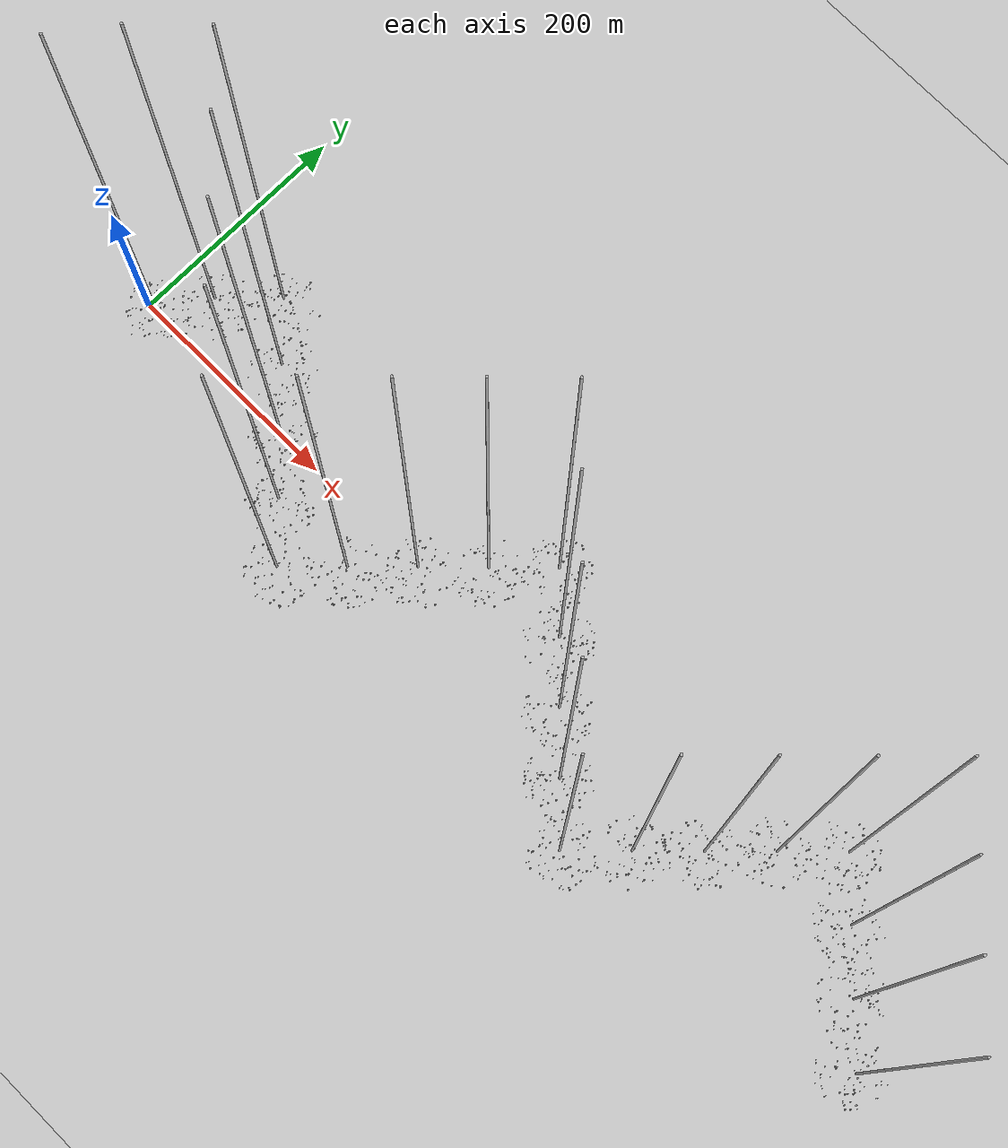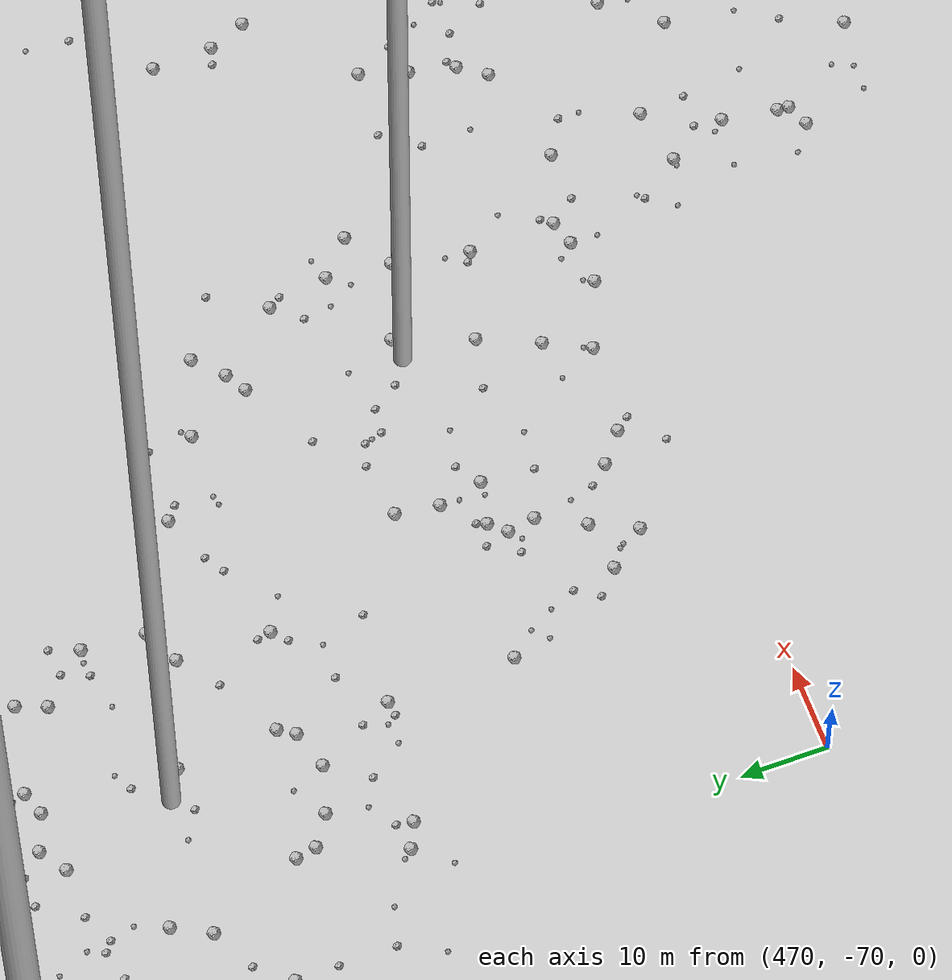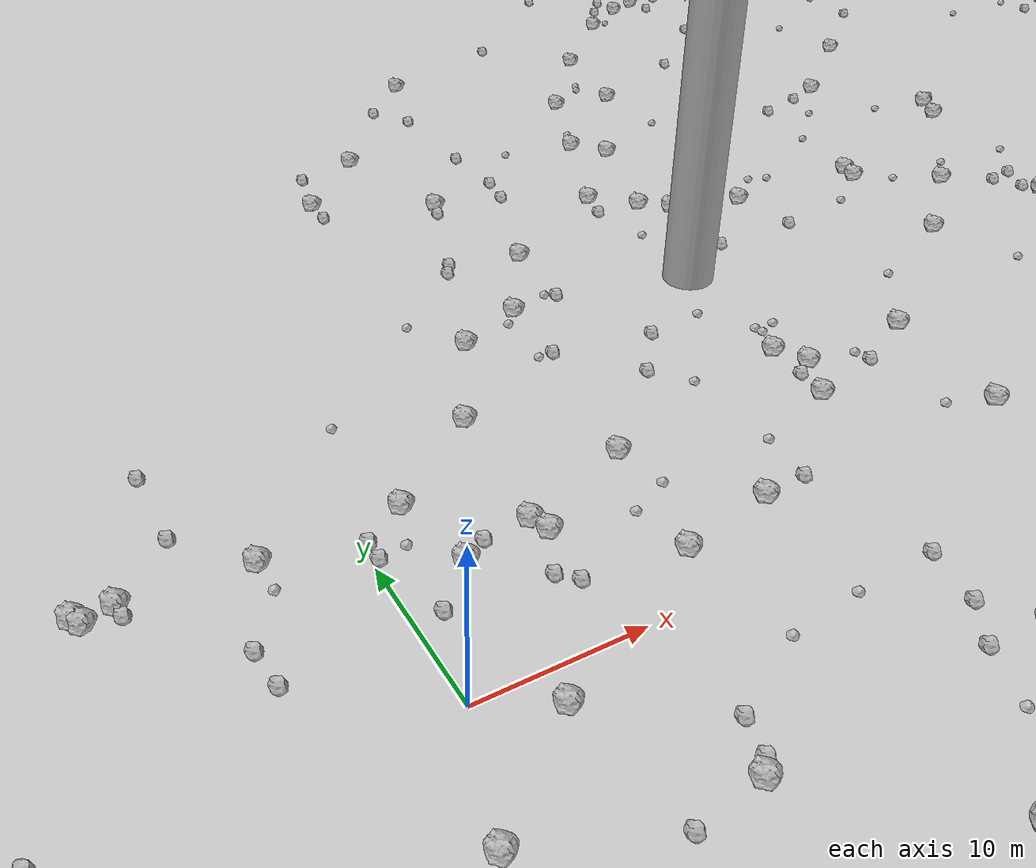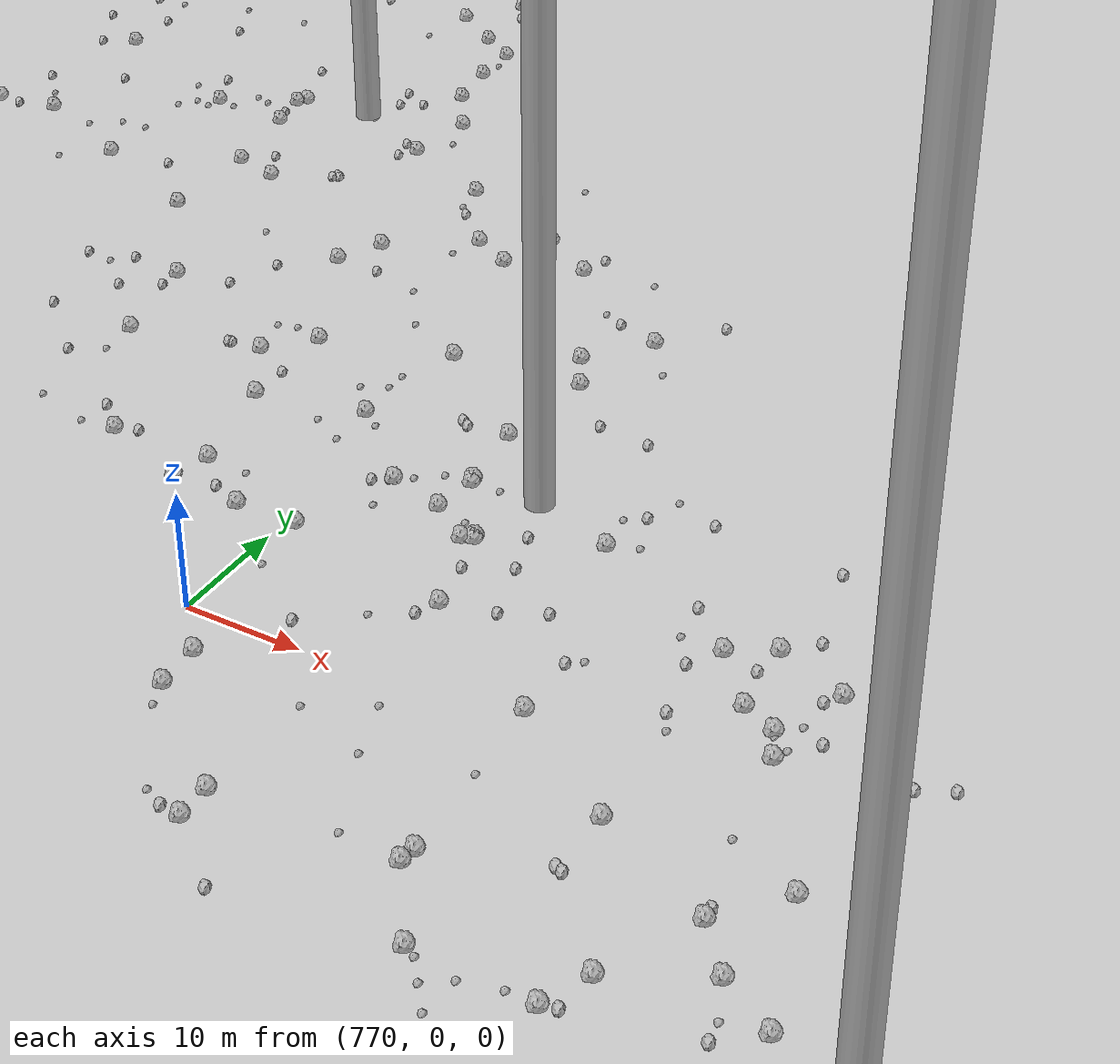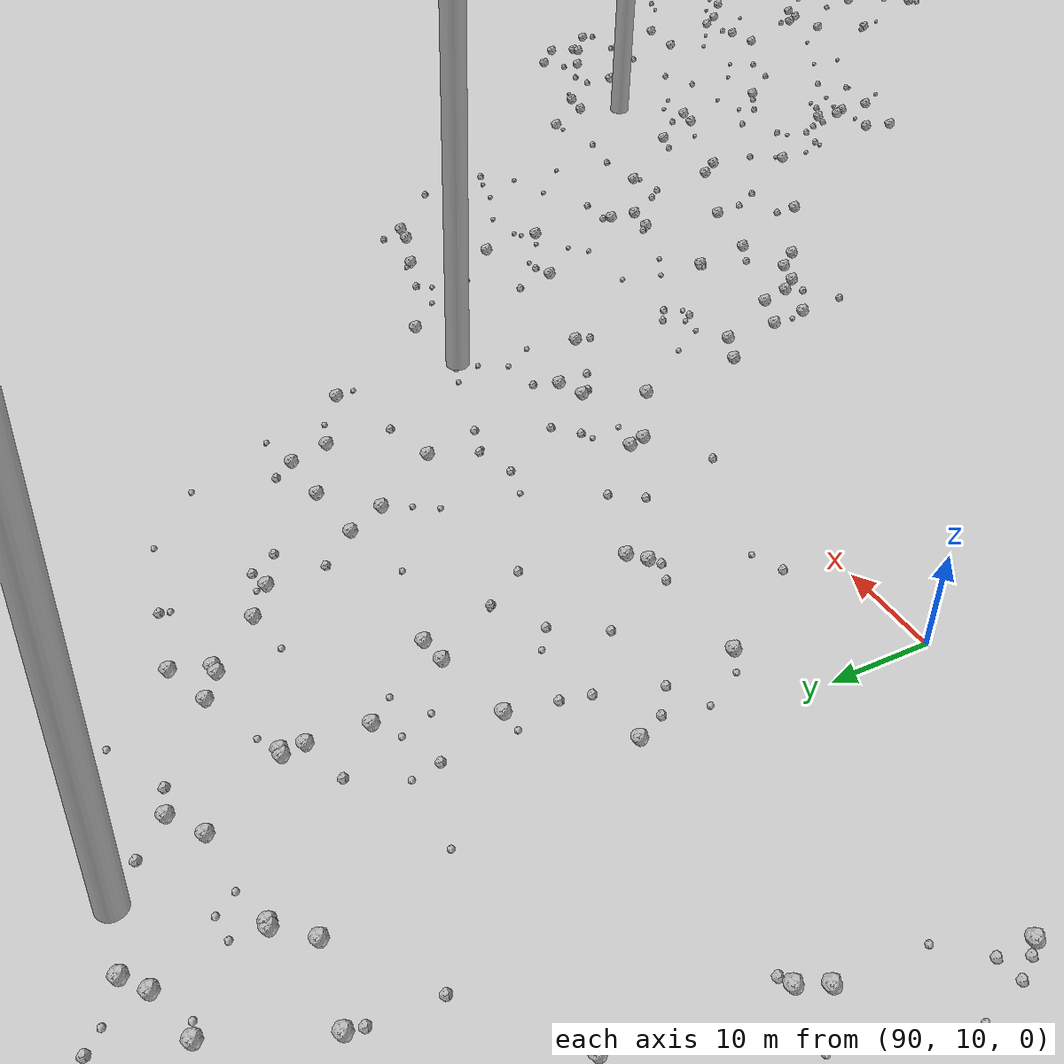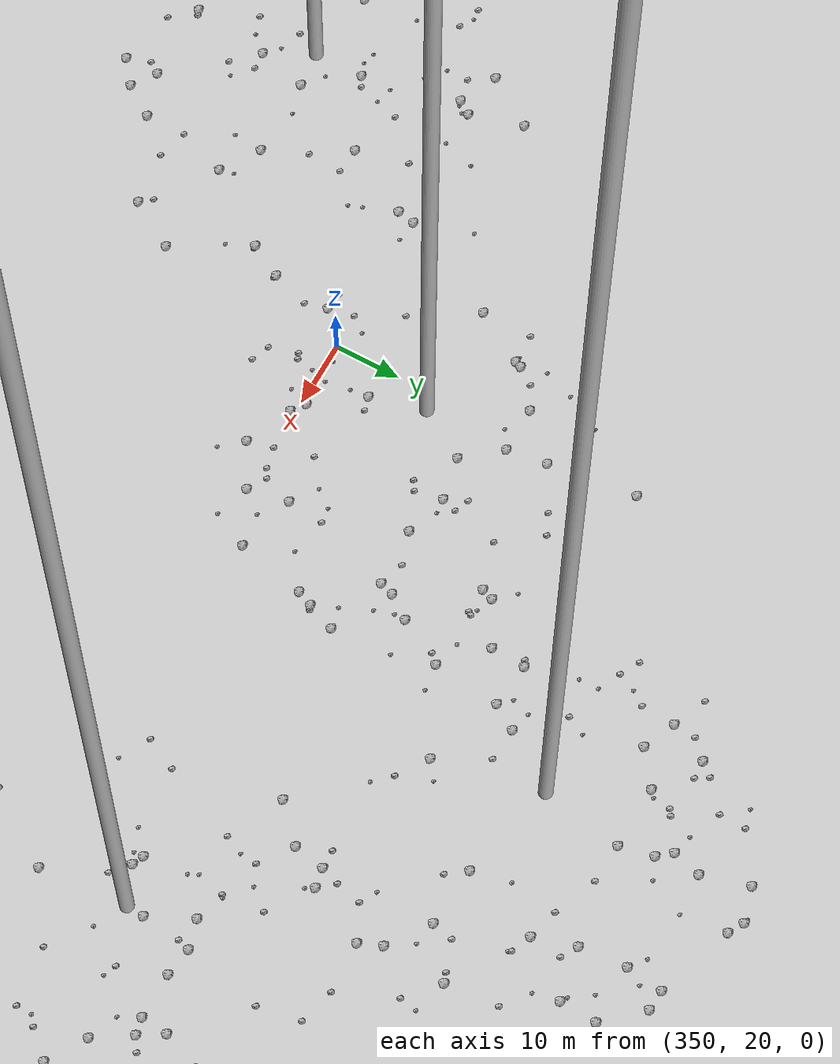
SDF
<sdf version="1.6">
 <world name="default">
  <include><uri>model://custom_ground</uri></include>
  <include><uri>model://sun</uri></include>
  <spherical_coordinates>
   <surface_model>EARTH_WGS84</surface_model>
   <latitude_deg>38.161479</latitude_deg>
   <longitude_deg>-122.454630</longitude_deg>
   <elevation>488.0</elevation>
   <heading_deg>90</heading_deg>
  </spherical_coordinates>
  <model name="rock1_0_0">
   <include><uri>model://rock1</uri><pose>-9.574869123708524 -16.79007385703004 0.5 0 0 0</pose></include>
  </model>
  <model name="rock1_0_1">
   <include><uri>model://rock1</uri><pose>-14.185482868018411 13.141109071667316 0.5 0 0 0</pose></include>
  </model>
  <model name="rock1_0_2">
   <include><uri>model://rock1</uri><pose>3.183161711726001 13.439207861971639 0.5 0 0 0</pose></include>
  </model>
  <model name="rock1_0_3">
   <include><uri>model://rock1</uri><pose>8.808953629448713 9.220673519698032 0.5 0 0 0</pose></include>
  </model>
  <model name="rock1_0_4">
   <include><uri>model://rock1</uri><pose>21.190203714288785 4.638815837935745 0.5 0 0 0</pose></include>
  </model>
  <model name="rock1_0_5">
   <include><uri>model://rock1</uri><pose>16.714045543645604 -20.561831399972156 0.5 0 0 0</pose></include>
  </model>
  <model name="rock1_0_6">
   <include><uri>model://rock1</uri><pose>4.0715729349844025 -2.1879893918191584 0.5 0 0 0</pose></include>
  </model>
  <model name="rock1_0_7">
   <include><uri>model://rock1</uri><pose>-14.54855234548559 13.726349126331328 0.5 0 0 0</pose></include>
  </model>
  <model name="rock1_0_8">
   <include><uri>model://rock1</uri><pose>14.956129256534766 3.346099133646433 0.5 0 0 0</pose></include>
  </model>
  <model name="rock1_0_9">
   <include><uri>model://rock1</uri><pose>9.809891724569248 18.482798297748445 0.5 0 0 0</pose></include>
  </model>
  <model name="rock1_0_10">
   <include><uri>model://rock1</uri><pose>18.159410886407578 -16.83518749572343 0.5 0 0 0</pose></include>
  </model>
  <model name="rock1_0_11">
   <include><uri>model://rock1</uri><pose>-12.411459987530908 13.64316098984552 0.5 0 0 0</pose></include>
  </model>
  <model name="rock1_0_12">
   <include><uri>model://rock1</uri><pose>9.276836897159338 7.968131557842007 0.5 0 0 0</pose></include>
  </model>
  <model name="rock1_0_13">
   <include><uri>model://rock1</uri><pose>4.340243749976594 8.141389771003283 0.5 0 0 0</pose></include>
  </model>
  <model name="rock1_0_14">
   <include><uri>model://rock1</uri><pose>-5.863515619924495 -18.700320483359988 0.5 0 0 0</pose></include>
  </model>
  <model name="rock1_0_15">
   <include><uri>model://rock1</uri><pose>16.187796699736538 11.677973227661752 0.5 0 0 0</pose></include>
  </model>
  <model name="rock1_0_16">
   <include><uri>model://rock1</uri><pose>9.361580387261622 -9.548358582462303 0.5 0 0 0</pose></include>
  </model>
  <model name="rock1_0_17">
   <include><uri>model://rock1</uri><pose>27.406130158293777 -9.154368287301967 0.5 0 0 0</pose></include>
  </model>
  <model name="rock1_0_18">
   <include><uri>model://rock1</uri><pose>30.71560412747546 15.438636553877814 0.5 0 0 0</pose></include>
  </model>
  <model name="rock1_0_19">
   <include><uri>model://rock1</uri><pose>30.334338108661605 10.38571048967789 0.5 0 0 0</pose></include>
  </model>
  <model name="rock1_0_20">
   <include><uri>model://rock1</uri><pose>13.667398942886912 25.483970197770248 0.5 0 0 0</pose></include>
  </model>
  <model name="rock1_0_21">
   <include><uri>model://rock1</uri><pose>-5.206692347621331 13.08040142145331 0.5 0 0 0</pose></include>
  </model>
  <model name="rock1_0_22">
   <include><uri>model://rock1</uri><pose>32.200690342745865 -5.430255425349113 0.5 0 0 0</pose></include>
  </model>
  <model name="rock1_0_23">
   <include><uri>model://rock1</uri><pose>39.226585235973246 4.870127547089943 0.5 0 0 0</pose></include>
  </model>
  <model name="rock1_0_24">
   <include><uri>model://rock1</uri><pose>18.376451594422818 27.43114792632251 0.5 0 0 0</pose></include>
  </model>
  <model name="rock1_0_25">
   <include><uri>model://rock1</uri><pose>-16.16579249229643 -5.940988652029876 0.5 0 0 0</pose></include>
  </model>
  <model name="rock1_0_26">
   <include><uri>model://rock1</uri><pose>-2.311682810059736 -7.208164576602776 0.5 0 0 0</pose></include>
  </model>
  <model name="rock2_0_0">
   <include><uri>model://rock2</uri><pose>10.034048237618222 -8.736519541761318 0.3 0 0 0</pose></include>
  </model>
  <model name="rock2_0_1">
   <include><uri>model://rock2</uri><pose>8.267623747901169 -19.02313169740516 0.3 0 0 0</pose></include>
  </model>
  <model name="rock2_0_2">
   <include><uri>model://rock2</uri><pose>1.6391106813702763 5.573884012758967 0.3 0 0 0</pose></include>
  </model>
  <model name="rock2_0_3">
   <include><uri>model://rock2</uri><pose>30.54512457409173 -7.588465767738327 0.3 0 0 0</pose></include>
  </model>
  <model name="rock2_0_4">
   <include><uri>model://rock2</uri><pose>10.594845104303452 -6.582464178360684 0.3 0 0 0</pose></include>
  </model>
  <model name="rock2_0_5">
   <include><uri>model://rock2</uri><pose>-8.312883304383732 -11.377120057153885 0.3 0 0 0</pose></include>
  </model>
  <model name="rock2_0_6">
   <include><uri>model://rock2</uri><pose>-8.978737009741405 -14.430953761993893 0.3 0 0 0</pose></include>
  </model>
  <model name="rock2_0_7">
   <include><uri>model://rock2</uri><pose>0.3824911184552491 10.394549399347383 0.3 0 0 0</pose></include>
  </model>
  <model name="rock2_0_8">
   <include><uri>model://rock2</uri><pose>-7.465351421417047 7.576823413634038 0.3 0 0 0</pose></include>
  </model>
  <model name="rock2_0_9">
   <include><uri>model://rock2</uri><pose>-19.501371784328946 1.2038466642157566 0.3 0 0 0</pose></include>
  </model>
  <model name="rock2_0_10">
   <include><uri>model://rock2</uri><pose>25.83861604503656 -2.962006658952248 0.3 0 0 0</pose></include>
  </model>
  <model name="rock2_0_11">
   <include><uri>model://rock2</uri><pose>7.849819711046596 -27.571609447680057 0.3 0 0 0</pose></include>
  </model>
  <model name="rock2_0_12">
   <include><uri>model://rock2</uri><pose>-6.040213940606856 -9.66836136146554 0.3 0 0 0</pose></include>
  </model>
  <model name="rock2_0_13">
   <include><uri>model://rock2</uri><pose>-8.867036312636092 22.589340358944916 0.3 0 0 0</pose></include>
  </model>
  <model name="rock2_0_14">
   <include><uri>model://rock2</uri><pose>7.759716976146052 5.1214487661928985 0.3 0 0 0</pose></include>
  </model>
  <model name="rock2_0_15">
   <include><uri>model://rock2</uri><pose>-8.83003370775212 17.04531609246669 0.3 0 0 0</pose></include>
  </model>
  <model name="rock2_0_16">
   <include><uri>model://rock2</uri><pose>-12.34644500851674 12.814119806406893 0.3 0 0 0</pose></include>
  </model>
  <model name="rock2_0_17">
   <include><uri>model://rock2</uri><pose>5.593837671610583 -15.873761594032828 0.3 0 0 0</pose></include>
  </model>
  <model name="rock2_0_18">
   <include><uri>model://rock2</uri><pose>30.500427591717752 12.605839885750335 0.3 0 0 0</pose></include>
  </model>
  <model name="rock2_0_19">
   <include><uri>model://rock2</uri><pose>24.09984355309814 4.9470389821148615 0.3 0 0 0</pose></include>
  </model>
  <model name="rock2_0_20">
   <include><uri>model://rock2</uri><pose>-7.206990615858512 5.085687797235309 0.3 0 0 0</pose></include>
  </model>
  <model name="rock2_0_21">
   <include><uri>model://rock2</uri><pose>5.090958671865565 -10.207763736634988 0.3 0 0 0</pose></include>
  </model>
  <model name="rock2_0_22">
   <include><uri>model://rock2</uri><pose>5.819130542349765 9.05829838737472 0.3 0 0 0</pose></include>
  </model>
  <model name="rock2_0_23">
   <include><uri>model://rock2</uri><pose>23.47187936257346 -8.895508581681149 0.3 0 0 0</pose></include>
  </model>
  <model name="rock2_0_24">
   <include><uri>model://rock2</uri><pose>0.40921171297273773 11.808901074296138 0.3 0 0 0</pose></include>
  </model>
  <model name="rock2_0_25">
   <include><uri>model://rock2</uri><pose>8.761084313139754 4.1301336897070655 0.3 0 0 0</pose></include>
  </model>
  <model name="rock2_0_26">
   <include><uri>model://rock2</uri><pose>25.130466555567516 -6.449081843777364 0.3 0 0 0</pose></include>
  </model>
  <model name="rock3_0_0">
   <include><uri>model://rock3</uri><pose>25.3667530887545 -12.998135052525448 0.2 0 0 0</pose></include>
  </model>
  <model name="rock3_0_1">
   <include><uri>model://rock3</uri><pose>2.084301238711081 10.617736016485551 0.2 0 0 0</pose></include>
  </model>
  <model name="rock3_0_2">
   <include><uri>model://rock3</uri><pose>-5.166307922711731 10.890870495040943 0.2 0 0 0</pose></include>
  </model>
  <model name="rock3_0_3">
   <include><uri>model://rock3</uri><pose>-4.794067120473443 -16.79904079203046 0.2 0 0 0</pose></include>
  </model>
  <model name="rock3_0_4">
   <include><uri>model://rock3</uri><pose>36.469931228763876 -3.790635897342586 0.2 0 0 0</pose></include>
  </model>
  <model name="rock3_0_5">
   <include><uri>model://rock3</uri><pose>32.752907331548776 17.963517423733776 0.2 0 0 0</pose></include>
  </model>
  <model name="rock3_0_6">
   <include><uri>model://rock3</uri><pose>15.701734360354472 -3.9160692034342723 0.2 0 0 0</pose></include>
  </model>
  <model name="rock3_0_7">
   <include><uri>model://rock3</uri><pose>14.148200681811694 7.021509025279002 0.2 0 0 0</pose></include>
  </model>
  <model name="rock3_0_8">
   <include><uri>model://rock3</uri><pose>-18.129730689842173 -0.44689415904500507 0.2 0 0 0</pose></include>
  </model>
  <model name="rock3_0_9">
   <include><uri>model://rock3</uri><pose>36.23161518929523 6.0326762228818325 0.2 0 0 0</pose></include>
  </model>
  <model name="rock3_0_10">
   <include><uri>model://rock3</uri><pose>17.036158683195353 22.00823247087935 0.2 0 0 0</pose></include>
  </model>
  <model name="rock3_0_11">
   <include><uri>model://rock3</uri><pose>2.471442960517649 -21.865717133432188 0.2 0 0 0</pose></include>
  </model>
  <model name="rock3_0_12">
   <include><uri>model://rock3</uri><pose>7.6456357311461005 -15.108418369727863 0.2 0 0 0</pose></include>
  </model>
  <model name="rock3_0_13">
   <include><uri>model://rock3</uri><pose>2.480334098300819 21.533275823309793 0.2 0 0 0</pose></include>
  </model>
  <model name="rock3_0_14">
   <include><uri>model://rock3</uri><pose>20.516558853500378 -3.270974349834308 0.2 0 0 0</pose></include>
  </model>
  <model name="rock3_0_15">
   <include><uri>model://rock3</uri><pose>-3.051125450568268 -22.11643719668475 0.2 0 0 0</pose></include>
  </model>
  <model name="rock3_0_16">
   <include><uri>model://rock3</uri><pose>35.16370481775306 12.763611769361376 0.2 0 0 0</pose></include>
  </model>
  <model name="rock3_0_17">
   <include><uri>model://rock3</uri><pose>27.421180113590054 -15.047234057990337 0.2 0 0 0</pose></include>
  </model>
  <model name="rock3_0_18">
   <include><uri>model://rock3</uri><pose>-3.133502825938347 -20.02349967116759 0.2 0 0 0</pose></include>
  </model>
  <model name="rock3_0_19">
   <include><uri>model://rock3</uri><pose>-12.878648965847672 -12.928425865737431 0.2 0 0 0</pose></include>
  </model>
  <model name="rock3_0_20">
   <include><uri>model://rock3</uri><pose>22.192377878570795 -12.330042599997412 0.2 0 0 0</pose></include>
  </model>
  <model name="rock3_0_21">
   <include><uri>model://rock3</uri><pose>16.812962284583783 8.283395773762749 0.2 0 0 0</pose></include>
  </model>
  <model name="rock3_0_22">
   <include><uri>model://rock3</uri><pose>11.119518566742823 -16.872444643984398 0.2 0 0 0</pose></include>
  </model>
  <model name="rock3_0_23">
   <include><uri>model://rock3</uri><pose>12.027010860697608 -17.940958181877765 0.2 0 0 0</pose></include>
  </model>
  <model name="rock3_0_24">
   <include><uri>model://rock3</uri><pose>11.086528343450052 29.076181890418283 0.2 0 0 0</pose></include>
  </model>
  <model name="rock3_0_25">
   <include><uri>model://rock3</uri><pose>24.512754860477465 8.451454510189272 0.2 0 0 0</pose></include>
  </model>
  <model name="rock3_0_26">
   <include><uri>model://rock3</uri><pose>-4.175261938721057 -8.810299954664707 0.2 0 0 0</pose></include>
  </model>
  <model name="rock1_1_0">
   <include><uri>model://rock1</uri><pose>20.56842919335226 43.39360853186586 0.5 0 0 0</pose></include>
  </model>
  <model name="rock1_1_1">
   <include><uri>model://rock1</uri><pose>34.54414254511432 36.0289951679605 0.5 0 0 0</pose></include>
  </model>
  <model name="rock1_1_2">
   <include><uri>model://rock1</uri><pose>35.557874803564225 47.442828483595 0.5 0 0 0</pose></include>
  </model>
  <model name="rock1_1_3">
   <include><uri>model://rock1</uri><pose>38.98027151588042 55.303319675051824 0.5 0 0 0</pose></include>
  </model>
  <model name="rock1_1_4">
   <include><uri>model://rock1</uri><pose>68.68092784216991 39.956355920635815 0.5 0 0 0</pose></include>
  </model>
  <model name="rock1_1_5">
   <include><uri>model://rock1</uri><pose>51.98057158302571 22.413317910917563 0.5 0 0 0</pose></include>
  </model>
  <model name="rock1_1_6">
   <include><uri>model://rock1</uri><pose>40.02276035495676 13.892579998476151 0.5 0 0 0</pose></include>
  </model>
  <model name="rock1_1_7">
   <include><uri>model://rock1</uri><pose>58.0398811134352 59.25075467615316 0.5 0 0 0</pose></include>
  </model>
  <model name="rock1_1_8">
   <include><uri>model://rock1</uri><pose>52.92021755876763 33.07498113955545 0.5 0 0 0</pose></include>
  </model>
  <model name="rock1_1_9">
   <include><uri>model://rock1</uri><pose>31.617133850505944 38.683061207715625 0.5 0 0 0</pose></include>
  </model>
  <model name="rock1_1_10">
   <include><uri>model://rock1</uri><pose>64.0646343023448 22.893842136059792 0.5 0 0 0</pose></include>
  </model>
  <model name="rock1_1_11">
   <include><uri>model://rock1</uri><pose>17.816510859593635 53.46394491209938 0.5 0 0 0</pose></include>
  </model>
  <model name="rock1_1_12">
   <include><uri>model://rock1</uri><pose>36.459029099497485 34.47583252018792 0.5 0 0 0</pose></include>
  </model>
  <model name="rock1_1_13">
   <include><uri>model://rock1</uri><pose>52.64650835085797 31.734679790741055 0.5 0 0 0</pose></include>
  </model>
  <model name="rock1_1_14">
   <include><uri>model://rock1</uri><pose>67.533151214804 37.623447157282264 0.5 0 0 0</pose></include>
  </model>
  <model name="rock1_1_15">
   <include><uri>model://rock1</uri><pose>48.97585447794847 44.079956439484924 0.5 0 0 0</pose></include>
  </model>
  <model name="rock1_1_16">
   <include><uri>model://rock1</uri><pose>61.7643403899301 47.15381417526136 0.5 0 0 0</pose></include>
  </model>
  <model name="rock1_1_17">
   <include><uri>model://rock1</uri><pose>37.592967943056024 45.004045625000686 0.5 0 0 0</pose></include>
  </model>
  <model name="rock1_1_18">
   <include><uri>model://rock1</uri><pose>27.98664447276545 65.86131497099646 0.5 0 0 0</pose></include>
  </model>
  <model name="rock1_1_19">
   <include><uri>model://rock1</uri><pose>22.403818267050404 33.59780710165229 0.5 0 0 0</pose></include>
  </model>
  <model name="rock1_1_20">
   <include><uri>model://rock1</uri><pose>12.135534310326154 47.84837188661651 0.5 0 0 0</pose></include>
  </model>
  <model name="rock1_1_21">
   <include><uri>model://rock1</uri><pose>58.58017045500706 28.030936133967955 0.5 0 0 0</pose></include>
  </model>
  <model name="rock1_1_22">
   <include><uri>model://rock1</uri><pose>45.62394343526531 63.44732540400578 0.5 0 0 0</pose></include>
  </model>
  <model name="rock1_1_23">
   <include><uri>model://rock1</uri><pose>59.063663972566765 61.72074473113258 0.5 0 0 0</pose></include>
  </model>
  <model name="rock1_1_24">
   <include><uri>model://rock1</uri><pose>41.92105129299435 32.975747726192964 0.5 0 0 0</pose></include>
  </model>
  <model name="rock1_1_25">
   <include><uri>model://rock1</uri><pose>43.969744070814 54.57288919146715 0.5 0 0 0</pose></include>
  </model>
  <model name="rock1_1_26">
   <include><uri>model://rock1</uri><pose>31.85747686875356 13.380222615479864 0.5 0 0 0</pose></include>
  </model>
  <model name="rock2_1_0">
   <include><uri>model://rock2</uri><pose>58.622574141553244 46.04596359426191 0.3 0 0 0</pose></include>
  </model>
  <model name="rock2_1_1">
   <include><uri>model://rock2</uri><pose>16.634932775292654 33.90655044337322 0.3 0 0 0</pose></include>
  </model>
  <model name="rock2_1_2">
   <include><uri>model://rock2</uri><pose>21.86623344000447 27.798917670338838 0.3 0 0 0</pose></include>
  </model>
  <model name="rock2_1_3">
   <include><uri>model://rock2</uri><pose>25.64309454367365 42.13378351031753 0.3 0 0 0</pose></include>
  </model>
  <model name="rock2_1_4">
   <include><uri>model://rock2</uri><pose>63.16891392572247 23.96339206996751 0.3 0 0 0</pose></include>
  </model>
  <model name="rock2_1_5">
   <include><uri>model://rock2</uri><pose>69.63515681290383 40.49375042122806 0.3 0 0 0</pose></include>
  </model>
  <model name="rock2_1_6">
   <include><uri>model://rock2</uri><pose>23.544080094854458 61.45745200669279 0.3 0 0 0</pose></include>
  </model>
  <model name="rock2_1_7">
   <include><uri>model://rock2</uri><pose>39.2958847070196 69.91018445752849 0.3 0 0 0</pose></include>
  </model>
  <model name="rock2_1_8">
   <include><uri>model://rock2</uri><pose>25.49768294574217 58.422640790991 0.3 0 0 0</pose></include>
  </model>
  <model name="rock2_1_9">
   <include><uri>model://rock2</uri><pose>25.733149131433322 49.86176861200643 0.3 0 0 0</pose></include>
  </model>
  <model name="rock2_1_10">
   <include><uri>model://rock2</uri><pose>53.2722004326765 58.60248735231376 0.3 0 0 0</pose></include>
  </model>
  <model name="rock2_1_11">
   <include><uri>model://rock2</uri><pose>64.1374426247164 26.25019178358199 0.3 0 0 0</pose></include>
  </model>
  <model name="rock2_1_12">
   <include><uri>model://rock2</uri><pose>36.23612248752404 28.011529250899695 0.3 0 0 0</pose></include>
  </model>
  <model name="rock2_1_13">
   <include><uri>model://rock2</uri><pose>12.093301723956682 45.62888820984963 0.3 0 0 0</pose></include>
  </model>
  <model name="rock2_1_14">
   <include><uri>model://rock2</uri><pose>13.065652155931334 52.312144410185944 0.3 0 0 0</pose></include>
  </model>
  <model name="rock2_1_15">
   <include><uri>model://rock2</uri><pose>35.44351479219496 11.708990054403412 0.3 0 0 0</pose></include>
  </model>
  <model name="rock2_1_16">
   <include><uri>model://rock2</uri><pose>54.807216063659304 45.01041176520204 0.3 0 0 0</pose></include>
  </model>
  <model name="rock2_1_17">
   <include><uri>model://rock2</uri><pose>20.029774018924513 42.08736450972924 0.3 0 0 0</pose></include>
  </model>
  <model name="rock2_1_18">
   <include><uri>model://rock2</uri><pose>62.04467156147775 25.904922986339443 0.3 0 0 0</pose></include>
  </model>
  <model name="rock2_1_19">
   <include><uri>model://rock2</uri><pose>42.72332972358326 28.061559408686318 0.3 0 0 0</pose></include>
  </model>
  <model name="rock2_1_20">
   <include><uri>model://rock2</uri><pose>31.029823281608383 36.440312870062975 0.3 0 0 0</pose></include>
  </model>
  <model name="rock2_1_21">
   <include><uri>model://rock2</uri><pose>17.28158977603554 34.95220603016347 0.3 0 0 0</pose></include>
  </model>
  <model name="rock2_1_22">
   <include><uri>model://rock2</uri><pose>22.2000402469021 17.450810617321938 0.3 0 0 0</pose></include>
  </model>
  <model name="rock2_1_23">
   <include><uri>model://rock2</uri><pose>24.891309390365592 20.79528057246005 0.3 0 0 0</pose></include>
  </model>
  <model name="rock2_1_24">
   <include><uri>model://rock2</uri><pose>26.051409940821646 44.68731656638048 0.3 0 0 0</pose></include>
  </model>
  <model name="rock2_1_25">
   <include><uri>model://rock2</uri><pose>18.031830780600693 22.00006217780351 0.3 0 0 0</pose></include>
  </model>
  <model name="rock2_1_26">
   <include><uri>model://rock2</uri><pose>56.51719498406242 58.12715814129121 0.3 0 0 0</pose></include>
  </model>
  <model name="rock3_1_0">
   <include><uri>model://rock3</uri><pose>55.22000243148423 29.957447870848082 0.2 0 0 0</pose></include>
  </model>
  <model name="rock3_1_1">
   <include><uri>model://rock3</uri><pose>31.987001261350567 31.917360176904484 0.2 0 0 0</pose></include>
  </model>
  <model name="rock3_1_2">
   <include><uri>model://rock3</uri><pose>29.800583518591836 48.610229194014124 0.2 0 0 0</pose></include>
  </model>
  <model name="rock3_1_3">
   <include><uri>model://rock3</uri><pose>54.08853777254917 16.301431044647472 0.2 0 0 0</pose></include>
  </model>
  <model name="rock3_1_4">
   <include><uri>model://rock3</uri><pose>17.24000532405114 26.2688354786026 0.2 0 0 0</pose></include>
  </model>
  <model name="rock3_1_5">
   <include><uri>model://rock3</uri><pose>46.248231044242225 34.86117722946152 0.2 0 0 0</pose></include>
  </model>
  <model name="rock3_1_6">
   <include><uri>model://rock3</uri><pose>44.75380498193226 35.33557696008735 0.2 0 0 0</pose></include>
  </model>
  <model name="rock3_1_7">
   <include><uri>model://rock3</uri><pose>31.329193842469245 18.02700058116418 0.2 0 0 0</pose></include>
  </model>
  <model name="rock3_1_8">
   <include><uri>model://rock3</uri><pose>63.75881064094121 40.94501875015787 0.2 0 0 0</pose></include>
  </model>
  <model name="rock3_1_9">
   <include><uri>model://rock3</uri><pose>46.15653495089149 42.47129770051055 0.2 0 0 0</pose></include>
  </model>
  <model name="rock3_1_10">
   <include><uri>model://rock3</uri><pose>42.79295537539082 58.181449982167905 0.2 0 0 0</pose></include>
  </model>
  <model name="rock3_1_11">
   <include><uri>model://rock3</uri><pose>36.440445001079645 49.523021285484134 0.2 0 0 0</pose></include>
  </model>
  <model name="rock3_1_12">
   <include><uri>model://rock3</uri><pose>44.30380699965635 48.03372133890677 0.2 0 0 0</pose></include>
  </model>
  <model name="rock3_1_13">
   <include><uri>model://rock3</uri><pose>24.18104152672429 15.127286831731068 0.2 0 0 0</pose></include>
  </model>
  <model name="rock3_1_14">
   <include><uri>model://rock3</uri><pose>21.206330623076127 28.250747478337708 0.2 0 0 0</pose></include>
  </model>
  <model name="rock3_1_15">
   <include><uri>model://rock3</uri><pose>31.47484713825167 17.463983748464216 0.2 0 0 0</pose></include>
  </model>
  <model name="rock3_1_16">
   <include><uri>model://rock3</uri><pose>29.041120889280734 21.265201277567833 0.2 0 0 0</pose></include>
  </model>
  <model name="rock3_1_17">
   <include><uri>model://rock3</uri><pose>60.80041261099775 30.200575169460365 0.2 0 0 0</pose></include>
  </model>
  <model name="rock3_1_18">
   <include><uri>model://rock3</uri><pose>57.83189270552077 42.96542025135224 0.2 0 0 0</pose></include>
  </model>
  <model name="rock3_1_19">
   <include><uri>model://rock3</uri><pose>67.02759147210651 29.582554534053845 0.2 0 0 0</pose></include>
  </model>
  <model name="rock3_1_20">
   <include><uri>model://rock3</uri><pose>58.772583036491014 17.423188055268707 0.2 0 0 0</pose></include>
  </model>
  <model name="rock3_1_21">
   <include><uri>model://rock3</uri><pose>51.523609118194834 46.56657141913485 0.2 0 0 0</pose></include>
  </model>
  <model name="rock3_1_22">
   <include><uri>model://rock3</uri><pose>53.77209347392325 39.166379774767776 0.2 0 0 0</pose></include>
  </model>
  <model name="rock3_1_23">
   <include><uri>model://rock3</uri><pose>42.38889104530727 57.40413763606391 0.2 0 0 0</pose></include>
  </model>
  <model name="rock3_1_24">
   <include><uri>model://rock3</uri><pose>48.87333828179758 29.06011621425019 0.2 0 0 0</pose></include>
  </model>
  <model name="rock3_1_25">
   <include><uri>model://rock3</uri><pose>36.210171595804894 29.822907283256118 0.2 0 0 0</pose></include>
  </model>
  <model name="rock3_1_26">
   <include><uri>model://rock3</uri><pose>44.09681086765066 18.998487294682466 0.2 0 0 0</pose></include>
  </model>
  <model name="rock1_2_0">
   <include><uri>model://rock1</uri><pose>79.63940709577678 85.46569339748109 0.5 0 0 0</pose></include>
  </model>
  <model name="rock1_2_1">
   <include><uri>model://rock1</uri><pose>86.24112531216478 67.15506358972026 0.5 0 0 0</pose></include>
  </model>
  <model name="rock1_2_2">
   <include><uri>model://rock1</uri><pose>70.39616609644307 54.181245249231864 0.5 0 0 0</pose></include>
  </model>
  <model name="rock1_2_3">
   <include><uri>model://rock1</uri><pose>62.34148370402875 92.88864064413164 0.5 0 0 0</pose></include>
  </model>
  <model name="rock1_2_4">
   <include><uri>model://rock1</uri><pose>73.30658352790864 90.572565071112 0.5 0 0 0</pose></include>
  </model>
  <model name="rock1_2_5">
   <include><uri>model://rock1</uri><pose>69.34552071380512 76.91357643710431 0.5 0 0 0</pose></include>
  </model>
  <model name="rock1_2_6">
   <include><uri>model://rock1</uri><pose>101.29346240477884 73.68421652020363 0.5 0 0 0</pose></include>
  </model>
  <model name="rock1_2_7">
   <include><uri>model://rock1</uri><pose>73.54573785084457 86.91039330727841 0.5 0 0 0</pose></include>
  </model>
  <model name="rock1_2_8">
   <include><uri>model://rock1</uri><pose>79.50840052595568 108.98605675637515 0.5 0 0 0</pose></include>
  </model>
  <model name="rock1_2_9">
   <include><uri>model://rock1</uri><pose>79.02837181370012 68.2424173510119 0.5 0 0 0</pose></include>
  </model>
  <model name="rock1_2_10">
   <include><uri>model://rock1</uri><pose>78.11189489801902 95.28537592821402 0.5 0 0 0</pose></include>
  </model>
  <model name="rock1_2_11">
   <include><uri>model://rock1</uri><pose>82.89273039142165 77.21265354913893 0.5 0 0 0</pose></include>
  </model>
  <model name="rock1_2_12">
   <include><uri>model://rock1</uri><pose>87.59114471718814 78.72678125870786 0.5 0 0 0</pose></include>
  </model>
  <model name="rock1_2_13">
   <include><uri>model://rock1</uri><pose>80.98527934303226 84.71269239536151 0.5 0 0 0</pose></include>
  </model>
  <model name="rock1_2_14">
   <include><uri>model://rock1</uri><pose>69.51635741858257 81.72022240352419 0.5 0 0 0</pose></include>
  </model>
  <model name="rock1_2_15">
   <include><uri>model://rock1</uri><pose>57.57733310495941 73.69502580047802 0.5 0 0 0</pose></include>
  </model>
  <model name="rock1_2_16">
   <include><uri>model://rock1</uri><pose>68.53709710460964 84.5005179814761 0.5 0 0 0</pose></include>
  </model>
  <model name="rock1_2_17">
   <include><uri>model://rock1</uri><pose>63.940942339893155 63.87960246712059 0.5 0 0 0</pose></include>
  </model>
  <model name="rock1_2_18">
   <include><uri>model://rock1</uri><pose>106.01422753239777 93.99214429628557 0.5 0 0 0</pose></include>
  </model>
  <model name="rock1_2_19">
   <include><uri>model://rock1</uri><pose>89.56888164383673 80.30516511360332 0.5 0 0 0</pose></include>
  </model>
  <model name="rock1_2_20">
   <include><uri>model://rock1</uri><pose>60.376109364836225 74.70131188452018 0.5 0 0 0</pose></include>
  </model>
  <model name="rock1_2_21">
   <include><uri>model://rock1</uri><pose>89.05587704732574 69.89151319938378 0.5 0 0 0</pose></include>
  </model>
  <model name="rock1_2_22">
   <include><uri>model://rock1</uri><pose>88.64573337142008 69.982609309468 0.5 0 0 0</pose></include>
  </model>
  <model name="rock1_2_23">
   <include><uri>model://rock1</uri><pose>53.067190357290656 70.80936310934203 0.5 0 0 0</pose></include>
  </model>
  <model name="rock1_2_24">
   <include><uri>model://rock1</uri><pose>103.48065248471994 63.835062744240176 0.5 0 0 0</pose></include>
  </model>
  <model name="rock1_2_25">
   <include><uri>model://rock1</uri><pose>98.29894549110304 71.51726643709179 0.5 0 0 0</pose></include>
  </model>
  <model name="rock1_2_26">
   <include><uri>model://rock1</uri><pose>54.21965627034915 91.61033846579708 0.5 0 0 0</pose></include>
  </model>
  <model name="rock2_2_0">
   <include><uri>model://rock2</uri><pose>63.948739018877305 85.86359522842756 0.3 0 0 0</pose></include>
  </model>
  <model name="rock2_2_1">
   <include><uri>model://rock2</uri><pose>63.40191848665472 74.8439657186473 0.3 0 0 0</pose></include>
  </model>
  <model name="rock2_2_2">
   <include><uri>model://rock2</uri><pose>83.39372448624015 104.9459397251226 0.3 0 0 0</pose></include>
  </model>
  <model name="rock2_2_3">
   <include><uri>model://rock2</uri><pose>66.06846833750177 76.91367418526809 0.3 0 0 0</pose></include>
  </model>
  <model name="rock2_2_4">
   <include><uri>model://rock2</uri><pose>80.15732476724695 107.1422678549408 0.3 0 0 0</pose></include>
  </model>
  <model name="rock2_2_5">
   <include><uri>model://rock2</uri><pose>71.59004220354466 100.48645321812918 0.3 0 0 0</pose></include>
  </model>
  <model name="rock2_2_6">
   <include><uri>model://rock2</uri><pose>78.44901888912054 61.09558324182614 0.3 0 0 0</pose></include>
  </model>
  <model name="rock2_2_7">
   <include><uri>model://rock2</uri><pose>60.88640667866252 72.52301977261244 0.3 0 0 0</pose></include>
  </model>
  <model name="rock2_2_8">
   <include><uri>model://rock2</uri><pose>50.818990034783255 80.23262765917326 0.3 0 0 0</pose></include>
  </model>
  <model name="rock2_2_9">
   <include><uri>model://rock2</uri><pose>107.39658495468971 78.44395673171454 0.3 0 0 0</pose></include>
  </model>
  <model name="rock2_2_10">
   <include><uri>model://rock2</uri><pose>79.24672740318024 92.48151292136495 0.3 0 0 0</pose></include>
  </model>
  <model name="rock2_2_11">
   <include><uri>model://rock2</uri><pose>57.11427470625609 76.2984509722823 0.3 0 0 0</pose></include>
  </model>
  <model name="rock2_2_12">
   <include><uri>model://rock2</uri><pose>60.59272336172987 80.91527068204044 0.3 0 0 0</pose></include>
  </model>
  <model name="rock2_2_13">
   <include><uri>model://rock2</uri><pose>103.89016482052386 73.00502077383531 0.3 0 0 0</pose></include>
  </model>
  <model name="rock2_2_14">
   <include><uri>model://rock2</uri><pose>57.48027412360673 96.9811348916424 0.3 0 0 0</pose></include>
  </model>
  <model name="rock2_2_15">
   <include><uri>model://rock2</uri><pose>84.95554782986743 83.77306939829079 0.3 0 0 0</pose></include>
  </model>
  <model name="rock2_2_16">
   <include><uri>model://rock2</uri><pose>98.25772818736736 76.76018139410496 0.3 0 0 0</pose></include>
  </model>
  <model name="rock2_2_17">
   <include><uri>model://rock2</uri><pose>60.68716554925925 65.38199199604587 0.3 0 0 0</pose></include>
  </model>
  <model name="rock2_2_18">
   <include><uri>model://rock2</uri><pose>54.36129040478306 94.18405025151576 0.3 0 0 0</pose></include>
  </model>
  <model name="rock2_2_19">
   <include><uri>model://rock2</uri><pose>62.20502661118611 89.22999076711326 0.3 0 0 0</pose></include>
  </model>
  <model name="rock2_2_20">
   <include><uri>model://rock2</uri><pose>77.02222982683011 77.41556789712352 0.3 0 0 0</pose></include>
  </model>
  <model name="rock2_2_21">
   <include><uri>model://rock2</uri><pose>66.8743442943259 73.63356898593847 0.3 0 0 0</pose></include>
  </model>
  <model name="rock2_2_22">
   <include><uri>model://rock2</uri><pose>79.99498438468429 103.77067661990635 0.3 0 0 0</pose></include>
  </model>
  <model name="rock2_2_23">
   <include><uri>model://rock2</uri><pose>92.30479238243834 106.01620290959791 0.3 0 0 0</pose></include>
  </model>
  <model name="rock2_2_24">
   <include><uri>model://rock2</uri><pose>55.302508687498765 74.11406536671267 0.3 0 0 0</pose></include>
  </model>
  <model name="rock2_2_25">
   <include><uri>model://rock2</uri><pose>78.73256507359802 66.8015541093249 0.3 0 0 0</pose></include>
  </model>
  <model name="rock2_2_26">
   <include><uri>model://rock2</uri><pose>72.45572301468448 90.76370383695318 0.3 0 0 0</pose></include>
  </model>
  <model name="rock3_2_0">
   <include><uri>model://rock3</uri><pose>99.01779615263735 89.87262150929539 0.2 0 0 0</pose></include>
  </model>
  <model name="rock3_2_1">
   <include><uri>model://rock3</uri><pose>91.19053942386128 72.96718925654352 0.2 0 0 0</pose></include>
  </model>
  <model name="rock3_2_2">
   <include><uri>model://rock3</uri><pose>78.11919001823675 73.70093130448697 0.2 0 0 0</pose></include>
  </model>
  <model name="rock3_2_3">
   <include><uri>model://rock3</uri><pose>86.4280974107189 82.23628031800635 0.2 0 0 0</pose></include>
  </model>
  <model name="rock3_2_4">
   <include><uri>model://rock3</uri><pose>109.69611375131673 75.97618604238023 0.2 0 0 0</pose></include>
  </model>
  <model name="rock3_2_5">
   <include><uri>model://rock3</uri><pose>84.19709902267023 76.75003621090947 0.2 0 0 0</pose></include>
  </model>
  <model name="rock3_2_6">
   <include><uri>model://rock3</uri><pose>54.59953738612754 70.9643166261254 0.2 0 0 0</pose></include>
  </model>
  <model name="rock3_2_7">
   <include><uri>model://rock3</uri><pose>71.69259524644173 103.88526749164618 0.2 0 0 0</pose></include>
  </model>
  <model name="rock3_2_8">
   <include><uri>model://rock3</uri><pose>96.11006541702983 55.62960599482274 0.2 0 0 0</pose></include>
  </model>
  <model name="rock3_2_9">
   <include><uri>model://rock3</uri><pose>88.9124891521661 72.7450151042143 0.2 0 0 0</pose></include>
  </model>
  <model name="rock3_2_10">
   <include><uri>model://rock3</uri><pose>92.51804691058388 71.04462025756027 0.2 0 0 0</pose></include>
  </model>
  <model name="rock3_2_11">
   <include><uri>model://rock3</uri><pose>103.25479295198579 91.2865102477954 0.2 0 0 0</pose></include>
  </model>
  <model name="rock3_2_12">
   <include><uri>model://rock3</uri><pose>80.94304146156352 100.74703069785495 0.2 0 0 0</pose></include>
  </model>
  <model name="rock3_2_13">
   <include><uri>model://rock3</uri><pose>58.45142452749059 98.37017603804435 0.2 0 0 0</pose></include>
  </model>
  <model name="rock3_2_14">
   <include><uri>model://rock3</uri><pose>75.92782373867095 105.17223036193263 0.2 0 0 0</pose></include>
  </model>
  <model name="rock3_2_15">
   <include><uri>model://rock3</uri><pose>88.95049666292724 55.680101336823405 0.2 0 0 0</pose></include>
  </model>
  <model name="rock3_2_16">
   <include><uri>model://rock3</uri><pose>84.84088864772241 93.13019827157822 0.2 0 0 0</pose></include>
  </model>
  <model name="rock3_2_17">
   <include><uri>model://rock3</uri><pose>98.84735376256225 93.15181836055761 0.2 0 0 0</pose></include>
  </model>
  <model name="rock3_2_18">
   <include><uri>model://rock3</uri><pose>84.41286550759483 95.30136486448322 0.2 0 0 0</pose></include>
  </model>
  <model name="rock3_2_19">
   <include><uri>model://rock3</uri><pose>69.64727361781158 60.99898066727962 0.2 0 0 0</pose></include>
  </model>
  <model name="rock3_2_20">
   <include><uri>model://rock3</uri><pose>105.4319216091235 64.94558012527703 0.2 0 0 0</pose></include>
  </model>
  <model name="rock3_2_21">
   <include><uri>model://rock3</uri><pose>64.44482671786328 93.45526750509102 0.2 0 0 0</pose></include>
  </model>
  <model name="rock3_2_22">
   <include><uri>model://rock3</uri><pose>77.02972734342842 109.13590607739798 0.2 0 0 0</pose></include>
  </model>
  <model name="rock3_2_23">
   <include><uri>model://rock3</uri><pose>70.23466633407344 94.42264896812587 0.2 0 0 0</pose></include>
  </model>
  <model name="rock3_2_24">
   <include><uri>model://rock3</uri><pose>66.2145094313453 100.29230249442281 0.2 0 0 0</pose></include>
  </model>
  <model name="rock3_2_25">
   <include><uri>model://rock3</uri><pose>65.06627689839513 88.78982656961546 0.2 0 0 0</pose></include>
  </model>
  <model name="rock3_2_26">
   <include><uri>model://rock3</uri><pose>60.279882444564564 60.05067828791869 0.2 0 0 0</pose></include>
  </model>
  <model name="rock1_3_0">
   <include><uri>model://rock1</uri><pose>96.71955909014599 25.367321534900597 0.5 0 0 0</pose></include>
  </model>
  <model name="rock1_3_1">
   <include><uri>model://rock1</uri><pose>115.89723767338756 69.22790859701782 0.5 0 0 0</pose></include>
  </model>
  <model name="rock1_3_2">
   <include><uri>model://rock1</uri><pose>111.30413787611494 67.45166130027673 0.5 0 0 0</pose></include>
  </model>
  <model name="rock1_3_3">
   <include><uri>model://rock1</uri><pose>138.9035462071509 19.001737407907072 0.5 0 0 0</pose></include>
  </model>
  <model name="rock1_3_4">
   <include><uri>model://rock1</uri><pose>147.36762123875326 41.57513100074783 0.5 0 0 0</pose></include>
  </model>
  <model name="rock1_3_5">
   <include><uri>model://rock1</uri><pose>146.9250013185524 27.568496000283183 0.5 0 0 0</pose></include>
  </model>
  <model name="rock1_3_6">
   <include><uri>model://rock1</uri><pose>102.89658964569354 63.88297610544415 0.5 0 0 0</pose></include>
  </model>
  <model name="rock1_3_7">
   <include><uri>model://rock1</uri><pose>91.83573862720161 37.76200549245223 0.5 0 0 0</pose></include>
  </model>
  <model name="rock1_3_8">
   <include><uri>model://rock1</uri><pose>139.76048531100002 45.69335735740664 0.5 0 0 0</pose></include>
  </model>
  <model name="rock1_3_9">
   <include><uri>model://rock1</uri><pose>118.82665653167398 60.73794682728327 0.5 0 0 0</pose></include>
  </model>
  <model name="rock1_3_10">
   <include><uri>model://rock1</uri><pose>122.28695552905592 58.32856289880187 0.5 0 0 0</pose></include>
  </model>
  <model name="rock1_3_11">
   <include><uri>model://rock1</uri><pose>103.20337157194761 61.78182182212926 0.5 0 0 0</pose></include>
  </model>
  <model name="rock1_3_12">
   <include><uri>model://rock1</uri><pose>132.5816312619918 49.5282160894997 0.5 0 0 0</pose></include>
  </model>
  <model name="rock1_3_13">
   <include><uri>model://rock1</uri><pose>133.57544656689583 37.160560097725714 0.5 0 0 0</pose></include>
  </model>
  <model name="rock1_3_14">
   <include><uri>model://rock1</uri><pose>111.39285489002394 27.1795879538329 0.5 0 0 0</pose></include>
  </model>
  <model name="rock1_3_15">
   <include><uri>model://rock1</uri><pose>126.27655985631483 16.08667125174631 0.5 0 0 0</pose></include>
  </model>
  <model name="rock1_3_16">
   <include><uri>model://rock1</uri><pose>125.74148965613131 17.985608156406002 0.5 0 0 0</pose></include>
  </model>
  <model name="rock1_3_17">
   <include><uri>model://rock1</uri><pose>102.78037685597639 56.26996551618517 0.5 0 0 0</pose></include>
  </model>
  <model name="rock1_3_18">
   <include><uri>model://rock1</uri><pose>109.45872128703381 48.628128606098116 0.5 0 0 0</pose></include>
  </model>
  <model name="rock1_3_19">
   <include><uri>model://rock1</uri><pose>127.9407728824412 44.65516794411225 0.5 0 0 0</pose></include>
  </model>
  <model name="rock1_3_20">
   <include><uri>model://rock1</uri><pose>125.79916715993913 48.7245237776074 0.5 0 0 0</pose></include>
  </model>
  <model name="rock1_3_21">
   <include><uri>model://rock1</uri><pose>113.83212903691978 65.6831865508668 0.5 0 0 0</pose></include>
  </model>
  <model name="rock1_3_22">
   <include><uri>model://rock1</uri><pose>99.12500605928021 46.20839584349028 0.5 0 0 0</pose></include>
  </model>
  <model name="rock1_3_23">
   <include><uri>model://rock1</uri><pose>138.50336563027923 49.92559292077405 0.5 0 0 0</pose></include>
  </model>
  <model name="rock1_3_24">
   <include><uri>model://rock1</uri><pose>109.86663529260673 25.738473715028256 0.5 0 0 0</pose></include>
  </model>
  <model name="rock1_3_25">
   <include><uri>model://rock1</uri><pose>106.74015034791947 48.17405193284627 0.5 0 0 0</pose></include>
  </model>
  <model name="rock1_3_26">
   <include><uri>model://rock1</uri><pose>114.68132948053862 65.75231659502583 0.5 0 0 0</pose></include>
  </model>
  <model name="rock2_3_0">
   <include><uri>model://rock2</uri><pose>125.96729450771355 56.243963194485026 0.3 0 0 0</pose></include>
  </model>
  <model name="rock2_3_1">
   <include><uri>model://rock2</uri><pose>117.69083386365861 21.041179117729637 0.3 0 0 0</pose></include>
  </model>
  <model name="rock2_3_2">
   <include><uri>model://rock2</uri><pose>122.32262966084426 52.53662958396306 0.3 0 0 0</pose></include>
  </model>
  <model name="rock2_3_3">
   <include><uri>model://rock2</uri><pose>110.87476651120232 41.40817252864343 0.3 0 0 0</pose></include>
  </model>
  <model name="rock2_3_4">
   <include><uri>model://rock2</uri><pose>97.5615739610833 38.75429035226179 0.3 0 0 0</pose></include>
  </model>
  <model name="rock2_3_5">
   <include><uri>model://rock2</uri><pose>103.32985128551147 33.513197716287834 0.3 0 0 0</pose></include>
  </model>
  <model name="rock2_3_6">
   <include><uri>model://rock2</uri><pose>93.09950542924665 34.86601892223987 0.3 0 0 0</pose></include>
  </model>
  <model name="rock2_3_7">
   <include><uri>model://rock2</uri><pose>127.31651668893197 30.86898199211833 0.3 0 0 0</pose></include>
  </model>
  <model name="rock2_3_8">
   <include><uri>model://rock2</uri><pose>124.27456744112808 58.920641320993276 0.3 0 0 0</pose></include>
  </model>
  <model name="rock2_3_9">
   <include><uri>model://rock2</uri><pose>120.0875793579005 11.659496826645121 0.3 0 0 0</pose></include>
  </model>
  <model name="rock2_3_10">
   <include><uri>model://rock2</uri><pose>129.74363267632876 21.41497622918703 0.3 0 0 0</pose></include>
  </model>
  <model name="rock2_3_11">
   <include><uri>model://rock2</uri><pose>113.74645726397972 37.15583613432257 0.3 0 0 0</pose></include>
  </model>
  <model name="rock2_3_12">
   <include><uri>model://rock2</uri><pose>98.20155972411006 41.517007578797994 0.3 0 0 0</pose></include>
  </model>
  <model name="rock2_3_13">
   <include><uri>model://rock2</uri><pose>95.69000750039622 32.78234485603897 0.3 0 0 0</pose></include>
  </model>
  <model name="rock2_3_14">
   <include><uri>model://rock2</uri><pose>106.21101683273227 38.36343306829042 0.3 0 0 0</pose></include>
  </model>
  <model name="rock2_3_15">
   <include><uri>model://rock2</uri><pose>108.8216705961163 24.904565362053464 0.3 0 0 0</pose></include>
  </model>
  <model name="rock2_3_16">
   <include><uri>model://rock2</uri><pose>132.03870081385926 23.705406896901895 0.3 0 0 0</pose></include>
  </model>
  <model name="rock2_3_17">
   <include><uri>model://rock2</uri><pose>123.00170639307194 67.96200388071087 0.3 0 0 0</pose></include>
  </model>
  <model name="rock2_3_18">
   <include><uri>model://rock2</uri><pose>103.13431381662818 15.444165921896822 0.3 0 0 0</pose></include>
  </model>
  <model name="rock2_3_19">
   <include><uri>model://rock2</uri><pose>131.5658975880514 32.251459515675634 0.3 0 0 0</pose></include>
  </model>
  <model name="rock2_3_20">
   <include><uri>model://rock2</uri><pose>135.13218459686476 31.04078049932861 0.3 0 0 0</pose></include>
  </model>
  <model name="rock2_3_21">
   <include><uri>model://rock2</uri><pose>139.24858569189593 38.74354579680691 0.3 0 0 0</pose></include>
  </model>
  <model name="rock2_3_22">
   <include><uri>model://rock2</uri><pose>96.65087794676096 52.954902400681185 0.3 0 0 0</pose></include>
  </model>
  <model name="rock2_3_23">
   <include><uri>model://rock2</uri><pose>106.68557711484996 25.735584727488188 0.3 0 0 0</pose></include>
  </model>
  <model name="rock2_3_24">
   <include><uri>model://rock2</uri><pose>119.75474841087814 24.140757007633127 0.3 0 0 0</pose></include>
  </model>
  <model name="rock2_3_25">
   <include><uri>model://rock2</uri><pose>98.58201140525276 60.37464108892789 0.3 0 0 0</pose></include>
  </model>
  <model name="rock2_3_26">
   <include><uri>model://rock2</uri><pose>136.71337691222075 52.17377102450596 0.3 0 0 0</pose></include>
  </model>
  <model name="rock3_3_0">
   <include><uri>model://rock3</uri><pose>118.60359257332061 46.501581709860176 0.2 0 0 0</pose></include>
  </model>
  <model name="rock3_3_1">
   <include><uri>model://rock3</uri><pose>114.15199418054092 59.76309851483521 0.2 0 0 0</pose></include>
  </model>
  <model name="rock3_3_2">
   <include><uri>model://rock3</uri><pose>131.81015740599403 65.89685714801622 0.2 0 0 0</pose></include>
  </model>
  <model name="rock3_3_3">
   <include><uri>model://rock3</uri><pose>96.93979833933024 45.913632256269494 0.2 0 0 0</pose></include>
  </model>
  <model name="rock3_3_4">
   <include><uri>model://rock3</uri><pose>104.03134414122061 39.93285637285333 0.2 0 0 0</pose></include>
  </model>
  <model name="rock3_3_5">
   <include><uri>model://rock3</uri><pose>106.21926430780468 16.659778741497473 0.2 0 0 0</pose></include>
  </model>
  <model name="rock3_3_6">
   <include><uri>model://rock3</uri><pose>92.25633422127163 30.626501154091212 0.2 0 0 0</pose></include>
  </model>
  <model name="rock3_3_7">
   <include><uri>model://rock3</uri><pose>126.6555976783219 41.85551737013826 0.2 0 0 0</pose></include>
  </model>
  <model name="rock3_3_8">
   <include><uri>model://rock3</uri><pose>110.90724272991342 41.11688243462931 0.2 0 0 0</pose></include>
  </model>
  <model name="rock3_3_9">
   <include><uri>model://rock3</uri><pose>100.49541097738964 54.52410385016744 0.2 0 0 0</pose></include>
  </model>
  <model name="rock3_3_10">
   <include><uri>model://rock3</uri><pose>125.24106628389924 39.52120784875625 0.2 0 0 0</pose></include>
  </model>
  <model name="rock3_3_11">
   <include><uri>model://rock3</uri><pose>129.07834945341213 17.275666206906898 0.2 0 0 0</pose></include>
  </model>
  <model name="rock3_3_12">
   <include><uri>model://rock3</uri><pose>146.03466466126173 25.231146496546568 0.2 0 0 0</pose></include>
  </model>
  <model name="rock3_3_13">
   <include><uri>model://rock3</uri><pose>101.69099958047751 51.38893240579239 0.2 0 0 0</pose></include>
  </model>
  <model name="rock3_3_14">
   <include><uri>model://rock3</uri><pose>142.82622417484646 51.01028214882025 0.2 0 0 0</pose></include>
  </model>
  <model name="rock3_3_15">
   <include><uri>model://rock3</uri><pose>143.15242282526168 44.506278444914464 0.2 0 0 0</pose></include>
  </model>
  <model name="rock3_3_16">
   <include><uri>model://rock3</uri><pose>123.86982454686637 31.58072920467624 0.2 0 0 0</pose></include>
  </model>
  <model name="rock3_3_17">
   <include><uri>model://rock3</uri><pose>110.61906794737251 41.52339232490326 0.2 0 0 0</pose></include>
  </model>
  <model name="rock3_3_18">
   <include><uri>model://rock3</uri><pose>128.61730785560923 20.647002991586817 0.2 0 0 0</pose></include>
  </model>
  <model name="rock3_3_19">
   <include><uri>model://rock3</uri><pose>94.4018315345621 26.58127890913282 0.2 0 0 0</pose></include>
  </model>
  <model name="rock3_3_20">
   <include><uri>model://rock3</uri><pose>104.82463238603803 53.71736985527609 0.2 0 0 0</pose></include>
  </model>
  <model name="rock3_3_21">
   <include><uri>model://rock3</uri><pose>138.35801028271277 60.28660772723194 0.2 0 0 0</pose></include>
  </model>
  <model name="rock3_3_22">
   <include><uri>model://rock3</uri><pose>147.6695609523976 39.421638552935036 0.2 0 0 0</pose></include>
  </model>
  <model name="rock3_3_23">
   <include><uri>model://rock3</uri><pose>132.03892325533226 31.761519980055233 0.2 0 0 0</pose></include>
  </model>
  <model name="rock3_3_24">
   <include><uri>model://rock3</uri><pose>122.80345403140024 66.96316103573187 0.2 0 0 0</pose></include>
  </model>
  <model name="rock3_3_25">
   <include><uri>model://rock3</uri><pose>144.06042440832795 28.54365465673801 0.2 0 0 0</pose></include>
  </model>
  <model name="rock3_3_26">
   <include><uri>model://rock3</uri><pose>121.98765414039539 59.2583346517617 0.2 0 0 0</pose></include>
  </model>
  <model name="rock1_4_0">
   <include><uri>model://rock1</uri><pose>179.04084492108055 20.06549668319066 0.5 0 0 0</pose></include>
  </model>
  <model name="rock1_4_1">
   <include><uri>model://rock1</uri><pose>161.33919419212864 -29.073503871158966 0.5 0 0 0</pose></include>
  </model>
  <model name="rock1_4_2">
   <include><uri>model://rock1</uri><pose>170.46256621604078 22.510082135252354 0.5 0 0 0</pose></include>
  </model>
  <model name="rock1_4_3">
   <include><uri>model://rock1</uri><pose>156.31873644714562 28.234712624160736 0.5 0 0 0</pose></include>
  </model>
  <model name="rock1_4_4">
   <include><uri>model://rock1</uri><pose>143.24201162746982 -11.327237554821167 0.5 0 0 0</pose></include>
  </model>
  <model name="rock1_4_5">
   <include><uri>model://rock1</uri><pose>169.12926531384483 12.664241341409216 0.5 0 0 0</pose></include>
  </model>
  <model name="rock1_4_6">
   <include><uri>model://rock1</uri><pose>151.35395944370433 -21.24755033946945 0.5 0 0 0</pose></include>
  </model>
  <model name="rock1_4_7">
   <include><uri>model://rock1</uri><pose>164.5472908128783 -19.071331985355105 0.5 0 0 0</pose></include>
  </model>
  <model name="rock1_4_8">
   <include><uri>model://rock1</uri><pose>144.3030537049869 -15.054033673247531 0.5 0 0 0</pose></include>
  </model>
  <model name="rock1_4_9">
   <include><uri>model://rock1</uri><pose>170.19828816782672 5.093831450964508 0.5 0 0 0</pose></include>
  </model>
  <model name="rock1_4_10">
   <include><uri>model://rock1</uri><pose>138.3140515264406 -2.6907870267096534 0.5 0 0 0</pose></include>
  </model>
  <model name="rock1_4_11">
   <include><uri>model://rock1</uri><pose>154.13579123025187 -9.459037143778744 0.5 0 0 0</pose></include>
  </model>
  <model name="rock1_4_12">
   <include><uri>model://rock1</uri><pose>169.75422175144087 -5.911390793190382 0.5 0 0 0</pose></include>
  </model>
  <model name="rock1_4_13">
   <include><uri>model://rock1</uri><pose>169.42971723052753 -9.258262416318775 0.5 0 0 0</pose></include>
  </model>
  <model name="rock1_4_14">
   <include><uri>model://rock1</uri><pose>138.62609194918065 -9.333341669134928 0.5 0 0 0</pose></include>
  </model>
  <model name="rock1_4_15">
   <include><uri>model://rock1</uri><pose>145.78082949067533 13.042195571652947 0.5 0 0 0</pose></include>
  </model>
  <model name="rock1_4_16">
   <include><uri>model://rock1</uri><pose>139.34700990266964 -13.893669116716723 0.5 0 0 0</pose></include>
  </model>
  <model name="rock1_4_17">
   <include><uri>model://rock1</uri><pose>160.2970988739714 8.442916888954223 0.5 0 0 0</pose></include>
  </model>
  <model name="rock1_4_18">
   <include><uri>model://rock1</uri><pose>149.10623889018632 -18.383634975108606 0.5 0 0 0</pose></include>
  </model>
  <model name="rock1_4_19">
   <include><uri>model://rock1</uri><pose>145.9033503571838 -17.211322225681542 0.5 0 0 0</pose></include>
  </model>
  <model name="rock1_4_20">
   <include><uri>model://rock1</uri><pose>135.95089246818344 17.811105172624735 0.5 0 0 0</pose></include>
  </model>
  <model name="rock1_4_21">
   <include><uri>model://rock1</uri><pose>134.52294434941533 -0.8240937778150972 0.5 0 0 0</pose></include>
  </model>
  <model name="rock1_4_22">
   <include><uri>model://rock1</uri><pose>178.17852888734717 -14.501711327100072 0.5 0 0 0</pose></include>
  </model>
  <model name="rock1_4_23">
   <include><uri>model://rock1</uri><pose>165.80240448751013 -8.756446190377861 0.5 0 0 0</pose></include>
  </model>
  <model name="rock1_4_24">
   <include><uri>model://rock1</uri><pose>176.513715990578 20.431793574932833 0.5 0 0 0</pose></include>
  </model>
  <model name="rock1_4_25">
   <include><uri>model://rock1</uri><pose>133.1152652228944 11.456990146794475 0.5 0 0 0</pose></include>
  </model>
  <model name="rock1_4_26">
   <include><uri>model://rock1</uri><pose>155.54499585375797 -16.745236140703497 0.5 0 0 0</pose></include>
  </model>
  <model name="rock2_4_0">
   <include><uri>model://rock2</uri><pose>153.75244600129292 -9.152951780696426 0.3 0 0 0</pose></include>
  </model>
  <model name="rock2_4_1">
   <include><uri>model://rock2</uri><pose>172.33024496478998 -13.844117804893486 0.3 0 0 0</pose></include>
  </model>
  <model name="rock2_4_2">
   <include><uri>model://rock2</uri><pose>188.31898472410862 3.904061611443936 0.3 0 0 0</pose></include>
  </model>
  <model name="rock2_4_3">
   <include><uri>model://rock2</uri><pose>139.8686058192702 21.617434738452545 0.3 0 0 0</pose></include>
  </model>
  <model name="rock2_4_4">
   <include><uri>model://rock2</uri><pose>186.71236278337244 13.067383420405704 0.3 0 0 0</pose></include>
  </model>
  <model name="rock2_4_5">
   <include><uri>model://rock2</uri><pose>165.22767714260056 -23.010148347756157 0.3 0 0 0</pose></include>
  </model>
  <model name="rock2_4_6">
   <include><uri>model://rock2</uri><pose>164.89342241270498 -7.860888244874374 0.3 0 0 0</pose></include>
  </model>
  <model name="rock2_4_7">
   <include><uri>model://rock2</uri><pose>143.19933619479514 -16.898317194982884 0.3 0 0 0</pose></include>
  </model>
  <model name="rock2_4_8">
   <include><uri>model://rock2</uri><pose>162.34830833975155 9.24224855294868 0.3 0 0 0</pose></include>
  </model>
  <model name="rock2_4_9">
   <include><uri>model://rock2</uri><pose>177.52715369117578 23.056277675946944 0.3 0 0 0</pose></include>
  </model>
  <model name="rock2_4_10">
   <include><uri>model://rock2</uri><pose>139.8721097080188 -19.748437794881777 0.3 0 0 0</pose></include>
  </model>
  <model name="rock2_4_11">
   <include><uri>model://rock2</uri><pose>167.3303017657658 -26.563991629558352 0.3 0 0 0</pose></include>
  </model>
  <model name="rock2_4_12">
   <include><uri>model://rock2</uri><pose>144.54782535651555 -1.6225835247327005 0.3 0 0 0</pose></include>
  </model>
  <model name="rock2_4_13">
   <include><uri>model://rock2</uri><pose>184.39071014554827 -13.965097275960307 0.3 0 0 0</pose></include>
  </model>
  <model name="rock2_4_14">
   <include><uri>model://rock2</uri><pose>161.2104960529683 -26.27309726492509 0.3 0 0 0</pose></include>
  </model>
  <model name="rock2_4_15">
   <include><uri>model://rock2</uri><pose>153.56671575359405 -9.468004508133337 0.3 0 0 0</pose></include>
  </model>
  <model name="rock2_4_16">
   <include><uri>model://rock2</uri><pose>139.17268414569523 15.319215509905007 0.3 0 0 0</pose></include>
  </model>
  <model name="rock2_4_17">
   <include><uri>model://rock2</uri><pose>169.9508565180461 -4.847006687489113 0.3 0 0 0</pose></include>
  </model>
  <model name="rock2_4_18">
   <include><uri>model://rock2</uri><pose>173.90124317284642 -15.619084736742455 0.3 0 0 0</pose></include>
  </model>
  <model name="rock2_4_19">
   <include><uri>model://rock2</uri><pose>146.79357792403619 0.5108919493697535 0.3 0 0 0</pose></include>
  </model>
  <model name="rock2_4_20">
   <include><uri>model://rock2</uri><pose>164.90885046773406 24.225805046468764 0.3 0 0 0</pose></include>
  </model>
  <model name="rock2_4_21">
   <include><uri>model://rock2</uri><pose>144.89102660782112 1.834101673055553 0.3 0 0 0</pose></include>
  </model>
  <model name="rock2_4_22">
   <include><uri>model://rock2</uri><pose>136.39677122789956 16.777336424944913 0.3 0 0 0</pose></include>
  </model>
  <model name="rock2_4_23">
   <include><uri>model://rock2</uri><pose>158.85470199174006 13.209824525122308 0.3 0 0 0</pose></include>
  </model>
  <model name="rock2_4_24">
   <include><uri>model://rock2</uri><pose>145.37881458751284 11.301847546672349 0.3 0 0 0</pose></include>
  </model>
  <model name="rock2_4_25">
   <include><uri>model://rock2</uri><pose>174.0997920031175 -4.886562558072168 0.3 0 0 0</pose></include>
  </model>
  <model name="rock2_4_26">
   <include><uri>model://rock2</uri><pose>152.25163964306049 -15.054974946307834 0.3 0 0 0</pose></include>
  </model>
  <model name="rock3_4_0">
   <include><uri>model://rock3</uri><pose>157.63531890494852 -5.785193425997676 0.2 0 0 0</pose></include>
  </model>
  <model name="rock3_4_1">
   <include><uri>model://rock3</uri><pose>185.41636176569043 0.1554279897403248 0.2 0 0 0</pose></include>
  </model>
  <model name="rock3_4_2">
   <include><uri>model://rock3</uri><pose>167.91679373396505 6.135731433322846 0.2 0 0 0</pose></include>
  </model>
  <model name="rock3_4_3">
   <include><uri>model://rock3</uri><pose>146.67511273478107 18.76602614599738 0.2 0 0 0</pose></include>
  </model>
  <model name="rock3_4_4">
   <include><uri>model://rock3</uri><pose>165.21659441511804 2.9918072518806227 0.2 0 0 0</pose></include>
  </model>
  <model name="rock3_4_5">
   <include><uri>model://rock3</uri><pose>163.34414237890283 1.0678393083871853 0.2 0 0 0</pose></include>
  </model>
  <model name="rock3_4_6">
   <include><uri>model://rock3</uri><pose>143.73995843060433 -0.5700892148866501 0.2 0 0 0</pose></include>
  </model>
  <model name="rock3_4_7">
   <include><uri>model://rock3</uri><pose>155.2875592947629 0.9734561171412572 0.2 0 0 0</pose></include>
  </model>
  <model name="rock3_4_8">
   <include><uri>model://rock3</uri><pose>182.25503311344414 5.429388637250526 0.2 0 0 0</pose></include>
  </model>
  <model name="rock3_4_9">
   <include><uri>model://rock3</uri><pose>180.2659329627649 -1.6227674585280951 0.2 0 0 0</pose></include>
  </model>
  <model name="rock3_4_10">
   <include><uri>model://rock3</uri><pose>185.51018939029996 -6.546927223822987 0.2 0 0 0</pose></include>
  </model>
  <model name="rock3_4_11">
   <include><uri>model://rock3</uri><pose>186.13023677576086 4.609782409972873 0.2 0 0 0</pose></include>
  </model>
  <model name="rock3_4_12">
   <include><uri>model://rock3</uri><pose>160.5935170092076 24.083384373314324 0.2 0 0 0</pose></include>
  </model>
  <model name="rock3_4_13">
   <include><uri>model://rock3</uri><pose>145.82588734984625 -1.5460970981284348 0.2 0 0 0</pose></include>
  </model>
  <model name="rock3_4_14">
   <include><uri>model://rock3</uri><pose>177.8078554637366 -15.386737448721892 0.2 0 0 0</pose></include>
  </model>
  <model name="rock3_4_15">
   <include><uri>model://rock3</uri><pose>138.73439545085463 3.625859785819351 0.2 0 0 0</pose></include>
  </model>
  <model name="rock3_4_16">
   <include><uri>model://rock3</uri><pose>138.64048157771253 -12.039232598878925 0.2 0 0 0</pose></include>
  </model>
  <model name="rock3_4_17">
   <include><uri>model://rock3</uri><pose>163.50163724917604 17.996034674867083 0.2 0 0 0</pose></include>
  </model>
  <model name="rock3_4_18">
   <include><uri>model://rock3</uri><pose>170.83423411548452 6.7372910479180845 0.2 0 0 0</pose></include>
  </model>
  <model name="rock3_4_19">
   <include><uri>model://rock3</uri><pose>141.4218608018591 -0.4699790107556261 0.2 0 0 0</pose></include>
  </model>
  <model name="rock3_4_20">
   <include><uri>model://rock3</uri><pose>169.7529994976298 23.300371476964102 0.2 0 0 0</pose></include>
  </model>
  <model name="rock3_4_21">
   <include><uri>model://rock3</uri><pose>154.09545755629162 -3.782484824407099 0.2 0 0 0</pose></include>
  </model>
  <model name="rock3_4_22">
   <include><uri>model://rock3</uri><pose>164.03321141358714 9.196299424117392 0.2 0 0 0</pose></include>
  </model>
  <model name="rock3_4_23">
   <include><uri>model://rock3</uri><pose>163.9477807644761 22.53014219407222 0.2 0 0 0</pose></include>
  </model>
  <model name="rock3_4_24">
   <include><uri>model://rock3</uri><pose>144.42015480640177 22.22718169455213 0.2 0 0 0</pose></include>
  </model>
  <model name="rock3_4_25">
   <include><uri>model://rock3</uri><pose>171.6483682787 7.351049736269239 0.2 0 0 0</pose></include>
  </model>
  <model name="rock3_4_26">
   <include><uri>model://rock3</uri><pose>176.36500434162332 7.980615102986043 0.2 0 0 0</pose></include>
  </model>
  <model name="rock1_5_0">
   <include><uri>model://rock1</uri><pose>183.58073243936224 -53.43716625864619 0.5 0 0 0</pose></include>
  </model>
  <model name="rock1_5_1">
   <include><uri>model://rock1</uri><pose>183.87675195192716 -50.2285891164159 0.5 0 0 0</pose></include>
  </model>
  <model name="rock1_5_2">
   <include><uri>model://rock1</uri><pose>176.9685243262849 -58.00471995072778 0.5 0 0 0</pose></include>
  </model>
  <model name="rock1_5_3">
   <include><uri>model://rock1</uri><pose>198.80915394100452 -13.742667801734306 0.5 0 0 0</pose></include>
  </model>
  <model name="rock1_5_4">
   <include><uri>model://rock1</uri><pose>184.60346115559565 -59.65074965930498 0.5 0 0 0</pose></include>
  </model>
  <model name="rock1_5_5">
   <include><uri>model://rock1</uri><pose>187.74358134004828 -25.38762768510795 0.5 0 0 0</pose></include>
  </model>
  <model name="rock1_5_6">
   <include><uri>model://rock1</uri><pose>213.98694922763306 -59.41104557152178 0.5 0 0 0</pose></include>
  </model>
  <model name="rock1_5_7">
   <include><uri>model://rock1</uri><pose>184.32152193115795 -54.915809443955396 0.5 0 0 0</pose></include>
  </model>
  <model name="rock1_5_8">
   <include><uri>model://rock1</uri><pose>193.8657366369017 -32.82502121818338 0.5 0 0 0</pose></include>
  </model>
  <model name="rock1_5_9">
   <include><uri>model://rock1</uri><pose>205.96513766253315 -20.406201358948557 0.5 0 0 0</pose></include>
  </model>
  <model name="rock1_5_10">
   <include><uri>model://rock1</uri><pose>220.95030989291587 -23.76196289739042 0.5 0 0 0</pose></include>
  </model>
  <model name="rock1_5_11">
   <include><uri>model://rock1</uri><pose>225.5347435957072 -46.97194912594701 0.5 0 0 0</pose></include>
  </model>
  <model name="rock1_5_12">
   <include><uri>model://rock1</uri><pose>195.52989395993322 -46.56178186065719 0.5 0 0 0</pose></include>
  </model>
  <model name="rock1_5_13">
   <include><uri>model://rock1</uri><pose>210.67205643076343 -30.012942159119746 0.5 0 0 0</pose></include>
  </model>
  <model name="rock1_5_14">
   <include><uri>model://rock1</uri><pose>223.1610794558095 -31.30650434906179 0.5 0 0 0</pose></include>
  </model>
  <model name="rock1_5_15">
   <include><uri>model://rock1</uri><pose>202.2001270599979 -19.787154517615797 0.5 0 0 0</pose></include>
  </model>
  <model name="rock1_5_16">
   <include><uri>model://rock1</uri><pose>175.3818859183845 -24.35760527514732 0.5 0 0 0</pose></include>
  </model>
  <model name="rock1_5_17">
   <include><uri>model://rock1</uri><pose>190.8870495165871 -32.17212705326729 0.5 0 0 0</pose></include>
  </model>
  <model name="rock1_5_18">
   <include><uri>model://rock1</uri><pose>223.92365830281562 -30.860308422826613 0.5 0 0 0</pose></include>
  </model>
  <model name="rock1_5_19">
   <include><uri>model://rock1</uri><pose>218.59629917946583 -58.762810088379084 0.5 0 0 0</pose></include>
  </model>
  <model name="rock1_5_20">
   <include><uri>model://rock1</uri><pose>225.11662404404285 -27.41601536589299 0.5 0 0 0</pose></include>
  </model>
  <model name="rock1_5_21">
   <include><uri>model://rock1</uri><pose>218.57414986754694 -46.379526075873635 0.5 0 0 0</pose></include>
  </model>
  <model name="rock1_5_22">
   <include><uri>model://rock1</uri><pose>174.55893109248265 -36.84183432896861 0.5 0 0 0</pose></include>
  </model>
  <model name="rock1_5_23">
   <include><uri>model://rock1</uri><pose>228.10253946706464 -34.99330716248227 0.5 0 0 0</pose></include>
  </model>
  <model name="rock1_5_24">
   <include><uri>model://rock1</uri><pose>218.10289870061482 -28.28670983238566 0.5 0 0 0</pose></include>
  </model>
  <model name="rock1_5_25">
   <include><uri>model://rock1</uri><pose>177.43718650146818 -27.081160135159735 0.5 0 0 0</pose></include>
  </model>
  <model name="rock1_5_26">
   <include><uri>model://rock1</uri><pose>177.96215440223224 -54.420711900642644 0.5 0 0 0</pose></include>
  </model>
  <model name="rock2_5_0">
   <include><uri>model://rock2</uri><pose>181.98970289281561 -41.386778315996295 0.3 0 0 0</pose></include>
  </model>
  <model name="rock2_5_1">
   <include><uri>model://rock2</uri><pose>184.62873535965187 -24.398605468761126 0.3 0 0 0</pose></include>
  </model>
  <model name="rock2_5_2">
   <include><uri>model://rock2</uri><pose>186.82360498120977 -38.66201698019026 0.3 0 0 0</pose></include>
  </model>
  <model name="rock2_5_3">
   <include><uri>model://rock2</uri><pose>218.2627247443396 -25.964251169553165 0.3 0 0 0</pose></include>
  </model>
  <model name="rock2_5_4">
   <include><uri>model://rock2</uri><pose>190.4608063607584 -43.3480734189771 0.3 0 0 0</pose></include>
  </model>
  <model name="rock2_5_5">
   <include><uri>model://rock2</uri><pose>210.86542992617146 -26.00935259324109 0.3 0 0 0</pose></include>
  </model>
  <model name="rock2_5_6">
   <include><uri>model://rock2</uri><pose>194.27789765741048 -58.172683003864975 0.3 0 0 0</pose></include>
  </model>
  <model name="rock2_5_7">
   <include><uri>model://rock2</uri><pose>207.92366753072122 -30.28737862427532 0.3 0 0 0</pose></include>
  </model>
  <model name="rock2_5_8">
   <include><uri>model://rock2</uri><pose>221.95674058532705 -36.90423302878541 0.3 0 0 0</pose></include>
  </model>
  <model name="rock2_5_9">
   <include><uri>model://rock2</uri><pose>186.6799945781447 -52.11873784061379 0.3 0 0 0</pose></include>
  </model>
  <model name="rock2_5_10">
   <include><uri>model://rock2</uri><pose>207.54413489432505 -38.44874398064256 0.3 0 0 0</pose></include>
  </model>
  <model name="rock2_5_11">
   <include><uri>model://rock2</uri><pose>176.96229771281875 -33.08317445121968 0.3 0 0 0</pose></include>
  </model>
  <model name="rock2_5_12">
   <include><uri>model://rock2</uri><pose>191.1002216683208 -61.21724398188188 0.3 0 0 0</pose></include>
  </model>
  <model name="rock2_5_13">
   <include><uri>model://rock2</uri><pose>227.8587924667727 -36.8096496504247 0.3 0 0 0</pose></include>
  </model>
  <model name="rock2_5_14">
   <include><uri>model://rock2</uri><pose>215.99090065730763 -37.69429787089544 0.3 0 0 0</pose></include>
  </model>
  <model name="rock2_5_15">
   <include><uri>model://rock2</uri><pose>213.58204099095448 -25.442798132155396 0.3 0 0 0</pose></include>
  </model>
  <model name="rock2_5_16">
   <include><uri>model://rock2</uri><pose>202.88700190365807 -40.422991704047114 0.3 0 0 0</pose></include>
  </model>
  <model name="rock2_5_17">
   <include><uri>model://rock2</uri><pose>193.64299184654098 -45.381185960125784 0.3 0 0 0</pose></include>
  </model>
  <model name="rock2_5_18">
   <include><uri>model://rock2</uri><pose>180.18835648094824 -45.334825313724124 0.3 0 0 0</pose></include>
  </model>
  <model name="rock2_5_19">
   <include><uri>model://rock2</uri><pose>176.82618349732596 -44.37761353589191 0.3 0 0 0</pose></include>
  </model>
  <model name="rock2_5_20">
   <include><uri>model://rock2</uri><pose>200.55343388610646 -52.681634558438134 0.3 0 0 0</pose></include>
  </model>
  <model name="rock2_5_21">
   <include><uri>model://rock2</uri><pose>205.42962352127725 -53.82429424238694 0.3 0 0 0</pose></include>
  </model>
  <model name="rock2_5_22">
   <include><uri>model://rock2</uri><pose>181.49679873868322 -47.55783098085023 0.3 0 0 0</pose></include>
  </model>
  <model name="rock2_5_23">
   <include><uri>model://rock2</uri><pose>190.47752257930364 -15.19068185427328 0.3 0 0 0</pose></include>
  </model>
  <model name="rock2_5_24">
   <include><uri>model://rock2</uri><pose>192.11520430429508 -29.818588912864705 0.3 0 0 0</pose></include>
  </model>
  <model name="rock2_5_25">
   <include><uri>model://rock2</uri><pose>182.08977113633358 -49.78288583212018 0.3 0 0 0</pose></include>
  </model>
  <model name="rock2_5_26">
   <include><uri>model://rock2</uri><pose>213.52437370973811 -33.909832396034375 0.3 0 0 0</pose></include>
  </model>
  <model name="rock3_5_0">
   <include><uri>model://rock3</uri><pose>199.41212193232442 -33.76239684278541 0.2 0 0 0</pose></include>
  </model>
  <model name="rock3_5_1">
   <include><uri>model://rock3</uri><pose>196.06425750755582 -40.59576936880196 0.2 0 0 0</pose></include>
  </model>
  <model name="rock3_5_2">
   <include><uri>model://rock3</uri><pose>181.03913729997248 -54.99854561830939 0.2 0 0 0</pose></include>
  </model>
  <model name="rock3_5_3">
   <include><uri>model://rock3</uri><pose>191.64534710045695 -41.47585397337639 0.2 0 0 0</pose></include>
  </model>
  <model name="rock3_5_4">
   <include><uri>model://rock3</uri><pose>175.35042874274373 -36.431061025607555 0.2 0 0 0</pose></include>
  </model>
  <model name="rock3_5_5">
   <include><uri>model://rock3</uri><pose>186.54519064015952 -30.136547989717307 0.2 0 0 0</pose></include>
  </model>
  <model name="rock3_5_6">
   <include><uri>model://rock3</uri><pose>202.9802696823956 -47.28815336022464 0.2 0 0 0</pose></include>
  </model>
  <model name="rock3_5_7">
   <include><uri>model://rock3</uri><pose>215.88930076291956 -51.29182544610097 0.2 0 0 0</pose></include>
  </model>
  <model name="rock3_5_8">
   <include><uri>model://rock3</uri><pose>218.8169456199432 -58.79164243873651 0.2 0 0 0</pose></include>
  </model>
  <model name="rock3_5_9">
   <include><uri>model://rock3</uri><pose>201.06741772914518 -67.38116247869517 0.2 0 0 0</pose></include>
  </model>
  <model name="rock3_5_10">
   <include><uri>model://rock3</uri><pose>207.3522182567503 -50.64279570823592 0.2 0 0 0</pose></include>
  </model>
  <model name="rock3_5_11">
   <include><uri>model://rock3</uri><pose>209.66636593518004 -67.80501071374235 0.2 0 0 0</pose></include>
  </model>
  <model name="rock3_5_12">
   <include><uri>model://rock3</uri><pose>221.31898730565905 -39.121428682930755 0.2 0 0 0</pose></include>
  </model>
  <model name="rock3_5_13">
   <include><uri>model://rock3</uri><pose>186.18731551340875 -55.015800610574495 0.2 0 0 0</pose></include>
  </model>
  <model name="rock3_5_14">
   <include><uri>model://rock3</uri><pose>180.82803682772214 -42.43524158989328 0.2 0 0 0</pose></include>
  </model>
  <model name="rock3_5_15">
   <include><uri>model://rock3</uri><pose>187.06994999897995 -63.75493164379648 0.2 0 0 0</pose></include>
  </model>
  <model name="rock3_5_16">
   <include><uri>model://rock3</uri><pose>219.21957170249016 -28.676826726981645 0.2 0 0 0</pose></include>
  </model>
  <model name="rock3_5_17">
   <include><uri>model://rock3</uri><pose>175.90097576631788 -44.52006252181608 0.2 0 0 0</pose></include>
  </model>
  <model name="rock3_5_18">
   <include><uri>model://rock3</uri><pose>190.98702845386083 -61.642049055584955 0.2 0 0 0</pose></include>
  </model>
  <model name="rock3_5_19">
   <include><uri>model://rock3</uri><pose>174.7623960014151 -41.22891607260395 0.2 0 0 0</pose></include>
  </model>
  <model name="rock3_5_20">
   <include><uri>model://rock3</uri><pose>196.76446438025295 -31.350549887632695 0.2 0 0 0</pose></include>
  </model>
  <model name="rock3_5_21">
   <include><uri>model://rock3</uri><pose>188.6426176367974 -52.6370948391667 0.2 0 0 0</pose></include>
  </model>
  <model name="rock3_5_22">
   <include><uri>model://rock3</uri><pose>201.3636933127055 -62.900301405793115 0.2 0 0 0</pose></include>
  </model>
  <model name="rock3_5_23">
   <include><uri>model://rock3</uri><pose>219.90975756394462 -54.3767503082516 0.2 0 0 0</pose></include>
  </model>
  <model name="rock3_5_24">
   <include><uri>model://rock3</uri><pose>197.12091761809498 -14.058521197233247 0.2 0 0 0</pose></include>
  </model>
  <model name="rock3_5_25">
   <include><uri>model://rock3</uri><pose>189.42205148704448 -56.141852045212254 0.2 0 0 0</pose></include>
  </model>
  <model name="rock3_5_26">
   <include><uri>model://rock3</uri><pose>208.37526782783516 -21.348963039367923 0.2 0 0 0</pose></include>
  </model>
  <model name="rock1_6_0">
   <include><uri>model://rock1</uri><pose>234.73725186645555 -74.94544110407742 0.5 0 0 0</pose></include>
  </model>
  <model name="rock1_6_1">
   <include><uri>model://rock1</uri><pose>262.3151871197945 -64.065804933556 0.5 0 0 0</pose></include>
  </model>
  <model name="rock1_6_2">
   <include><uri>model://rock1</uri><pose>254.12407827718116 -98.88031285026499 0.5 0 0 0</pose></include>
  </model>
  <model name="rock1_6_3">
   <include><uri>model://rock1</uri><pose>232.08162745061242 -77.70508303490185 0.5 0 0 0</pose></include>
  </model>
  <model name="rock1_6_4">
   <include><uri>model://rock1</uri><pose>253.82517314968683 -102.83597426011161 0.5 0 0 0</pose></include>
  </model>
  <model name="rock1_6_5">
   <include><uri>model://rock1</uri><pose>254.09251116298566 -80.41924196248499 0.5 0 0 0</pose></include>
  </model>
  <model name="rock1_6_6">
   <include><uri>model://rock1</uri><pose>220.43880664886197 -73.21732592674707 0.5 0 0 0</pose></include>
  </model>
  <model name="rock1_6_7">
   <include><uri>model://rock1</uri><pose>218.958186991674 -70.93003952287974 0.5 0 0 0</pose></include>
  </model>
  <model name="rock1_6_8">
   <include><uri>model://rock1</uri><pose>222.79236837571233 -86.66829993092247 0.5 0 0 0</pose></include>
  </model>
  <model name="rock1_6_9">
   <include><uri>model://rock1</uri><pose>221.13845143376557 -93.2566967689074 0.5 0 0 0</pose></include>
  </model>
  <model name="rock1_6_10">
   <include><uri>model://rock1</uri><pose>224.11189893303666 -57.30763983045002 0.5 0 0 0</pose></include>
  </model>
  <model name="rock1_6_11">
   <include><uri>model://rock1</uri><pose>211.16981149636416 -80.82563448124456 0.5 0 0 0</pose></include>
  </model>
  <model name="rock1_6_12">
   <include><uri>model://rock1</uri><pose>266.28887091943943 -81.40144154202537 0.5 0 0 0</pose></include>
  </model>
  <model name="rock1_6_13">
   <include><uri>model://rock1</uri><pose>223.14995464874897 -73.77331204994266 0.5 0 0 0</pose></include>
  </model>
  <model name="rock1_6_14">
   <include><uri>model://rock1</uri><pose>263.5457144235723 -78.35795308882464 0.5 0 0 0</pose></include>
  </model>
  <model name="rock1_6_15">
   <include><uri>model://rock1</uri><pose>233.21641009834198 -100.57906516799042 0.5 0 0 0</pose></include>
  </model>
  <model name="rock1_6_16">
   <include><uri>model://rock1</uri><pose>231.52699985473072 -64.64066285839772 0.5 0 0 0</pose></include>
  </model>
  <model name="rock1_6_17">
   <include><uri>model://rock1</uri><pose>256.08338010953895 -59.27305757356367 0.5 0 0 0</pose></include>
  </model>
  <model name="rock1_6_18">
   <include><uri>model://rock1</uri><pose>260.23771962819643 -99.16724454868661 0.5 0 0 0</pose></include>
  </model>
  <model name="rock1_6_19">
   <include><uri>model://rock1</uri><pose>252.67334489991543 -60.56678068032485 0.5 0 0 0</pose></include>
  </model>
  <model name="rock1_6_20">
   <include><uri>model://rock1</uri><pose>217.86506292571178 -96.13376924016399 0.5 0 0 0</pose></include>
  </model>
  <model name="rock1_6_21">
   <include><uri>model://rock1</uri><pose>237.5355522041091 -85.60637328078943 0.5 0 0 0</pose></include>
  </model>
  <model name="rock1_6_22">
   <include><uri>model://rock1</uri><pose>214.48208993305636 -73.49847802891402 0.5 0 0 0</pose></include>
  </model>
  <model name="rock1_6_23">
   <include><uri>model://rock1</uri><pose>266.44336107121103 -89.15784654696431 0.5 0 0 0</pose></include>
  </model>
  <model name="rock1_6_24">
   <include><uri>model://rock1</uri><pose>254.34600652845774 -89.21364588129836 0.5 0 0 0</pose></include>
  </model>
  <model name="rock1_6_25">
   <include><uri>model://rock1</uri><pose>265.2495430694812 -86.93164741874068 0.5 0 0 0</pose></include>
  </model>
  <model name="rock1_6_26">
   <include><uri>model://rock1</uri><pose>226.42709374081886 -60.319711262422736 0.5 0 0 0</pose></include>
  </model>
  <model name="rock2_6_0">
   <include><uri>model://rock2</uri><pose>253.22204281681405 -79.59695221946853 0.3 0 0 0</pose></include>
  </model>
  <model name="rock2_6_1">
   <include><uri>model://rock2</uri><pose>233.88588677215685 -90.28821841269978 0.3 0 0 0</pose></include>
  </model>
  <model name="rock2_6_2">
   <include><uri>model://rock2</uri><pose>267.28137409265963 -80.44063284577139 0.3 0 0 0</pose></include>
  </model>
  <model name="rock2_6_3">
   <include><uri>model://rock2</uri><pose>244.61063633938716 -91.60969387839691 0.3 0 0 0</pose></include>
  </model>
  <model name="rock2_6_4">
   <include><uri>model://rock2</uri><pose>261.43562345968104 -98.9395106257057 0.3 0 0 0</pose></include>
  </model>
  <model name="rock2_6_5">
   <include><uri>model://rock2</uri><pose>220.32685902367174 -58.06629738665989 0.3 0 0 0</pose></include>
  </model>
  <model name="rock2_6_6">
   <include><uri>model://rock2</uri><pose>240.97882510529604 -68.91040262846477 0.3 0 0 0</pose></include>
  </model>
  <model name="rock2_6_7">
   <include><uri>model://rock2</uri><pose>256.6644051665127 -60.44744536570767 0.3 0 0 0</pose></include>
  </model>
  <model name="rock2_6_8">
   <include><uri>model://rock2</uri><pose>261.8913852223708 -99.99336203745095 0.3 0 0 0</pose></include>
  </model>
  <model name="rock2_6_9">
   <include><uri>model://rock2</uri><pose>230.19983728585214 -96.76458621686709 0.3 0 0 0</pose></include>
  </model>
  <model name="rock2_6_10">
   <include><uri>model://rock2</uri><pose>244.04262883846968 -94.29980957064019 0.3 0 0 0</pose></include>
  </model>
  <model name="rock2_6_11">
   <include><uri>model://rock2</uri><pose>248.25799062650208 -77.4266862321781 0.3 0 0 0</pose></include>
  </model>
  <model name="rock2_6_12">
   <include><uri>model://rock2</uri><pose>231.1054200152868 -94.79487247951126 0.3 0 0 0</pose></include>
  </model>
  <model name="rock2_6_13">
   <include><uri>model://rock2</uri><pose>210.39277706640058 -79.70568990461146 0.3 0 0 0</pose></include>
  </model>
  <model name="rock2_6_14">
   <include><uri>model://rock2</uri><pose>234.33124143050276 -69.21757551554317 0.3 0 0 0</pose></include>
  </model>
  <model name="rock2_6_15">
   <include><uri>model://rock2</uri><pose>245.82305300610102 -57.60103607246529 0.3 0 0 0</pose></include>
  </model>
  <model name="rock2_6_16">
   <include><uri>model://rock2</uri><pose>219.01913924508298 -69.27893043520908 0.3 0 0 0</pose></include>
  </model>
  <model name="rock2_6_17">
   <include><uri>model://rock2</uri><pose>237.3718673709145 -54.46115257045724 0.3 0 0 0</pose></include>
  </model>
  <model name="rock2_6_18">
   <include><uri>model://rock2</uri><pose>216.97606390755263 -97.34463148032418 0.3 0 0 0</pose></include>
  </model>
  <model name="rock2_6_19">
   <include><uri>model://rock2</uri><pose>221.84758889676326 -81.21805477386118 0.3 0 0 0</pose></include>
  </model>
  <model name="rock2_6_20">
   <include><uri>model://rock2</uri><pose>233.49274346142275 -78.01564435126456 0.3 0 0 0</pose></include>
  </model>
  <model name="rock2_6_21">
   <include><uri>model://rock2</uri><pose>222.222480066612 -102.56756481865513 0.3 0 0 0</pose></include>
  </model>
  <model name="rock2_6_22">
   <include><uri>model://rock2</uri><pose>244.9735956777861 -72.89201272050784 0.3 0 0 0</pose></include>
  </model>
  <model name="rock2_6_23">
   <include><uri>model://rock2</uri><pose>242.08663362774917 -71.31405310487276 0.3 0 0 0</pose></include>
  </model>
  <model name="rock2_6_24">
   <include><uri>model://rock2</uri><pose>221.76525220012525 -100.72513240359078 0.3 0 0 0</pose></include>
  </model>
  <model name="rock2_6_25">
   <include><uri>model://rock2</uri><pose>227.7699079612524 -79.46443756317515 0.3 0 0 0</pose></include>
  </model>
  <model name="rock2_6_26">
   <include><uri>model://rock2</uri><pose>246.88062899334093 -104.83554145292369 0.3 0 0 0</pose></include>
  </model>
  <model name="rock3_6_0">
   <include><uri>model://rock3</uri><pose>240.62737470930043 -99.0468366310525 0.2 0 0 0</pose></include>
  </model>
  <model name="rock3_6_1">
   <include><uri>model://rock3</uri><pose>260.73422534659426 -89.16537002632666 0.2 0 0 0</pose></include>
  </model>
  <model name="rock3_6_2">
   <include><uri>model://rock3</uri><pose>247.99563130372167 -54.633911600020284 0.2 0 0 0</pose></include>
  </model>
  <model name="rock3_6_3">
   <include><uri>model://rock3</uri><pose>244.7323335819137 -54.527788357587305 0.2 0 0 0</pose></include>
  </model>
  <model name="rock3_6_4">
   <include><uri>model://rock3</uri><pose>241.0104863341868 -105.4158790648833 0.2 0 0 0</pose></include>
  </model>
  <model name="rock3_6_5">
   <include><uri>model://rock3</uri><pose>212.41718194852925 -84.5548455882332 0.2 0 0 0</pose></include>
  </model>
  <model name="rock3_6_6">
   <include><uri>model://rock3</uri><pose>224.32957944711436 -64.49179155693528 0.2 0 0 0</pose></include>
  </model>
  <model name="rock3_6_7">
   <include><uri>model://rock3</uri><pose>218.47583722228714 -98.46933747457695 0.2 0 0 0</pose></include>
  </model>
  <model name="rock3_6_8">
   <include><uri>model://rock3</uri><pose>238.5246782241281 -66.37051952243903 0.2 0 0 0</pose></include>
  </model>
  <model name="rock3_6_9">
   <include><uri>model://rock3</uri><pose>239.26222990505153 -57.98797344767832 0.2 0 0 0</pose></include>
  </model>
  <model name="rock3_6_10">
   <include><uri>model://rock3</uri><pose>267.14144375085397 -78.1354747389272 0.2 0 0 0</pose></include>
  </model>
  <model name="rock3_6_11">
   <include><uri>model://rock3</uri><pose>230.18580582536484 -61.40331550266076 0.2 0 0 0</pose></include>
  </model>
  <model name="rock3_6_12">
   <include><uri>model://rock3</uri><pose>260.4500170414356 -87.42785437074399 0.2 0 0 0</pose></include>
  </model>
  <model name="rock3_6_13">
   <include><uri>model://rock3</uri><pose>249.19148095758652 -55.011460951350436 0.2 0 0 0</pose></include>
  </model>
  <model name="rock3_6_14">
   <include><uri>model://rock3</uri><pose>234.50476823283356 -53.49308055955053 0.2 0 0 0</pose></include>
  </model>
  <model name="rock3_6_15">
   <include><uri>model://rock3</uri><pose>268.3257429084284 -74.78616266392748 0.2 0 0 0</pose></include>
  </model>
  <model name="rock3_6_16">
   <include><uri>model://rock3</uri><pose>234.54330997851616 -105.77227488253274 0.2 0 0 0</pose></include>
  </model>
  <model name="rock3_6_17">
   <include><uri>model://rock3</uri><pose>256.9267470560698 -64.74648581489129 0.2 0 0 0</pose></include>
  </model>
  <model name="rock3_6_18">
   <include><uri>model://rock3</uri><pose>226.74318066515838 -102.46673519140995 0.2 0 0 0</pose></include>
  </model>
  <model name="rock3_6_19">
   <include><uri>model://rock3</uri><pose>259.5076866288989 -81.20302777583224 0.2 0 0 0</pose></include>
  </model>
  <model name="rock3_6_20">
   <include><uri>model://rock3</uri><pose>225.56728966315427 -84.71144904829686 0.2 0 0 0</pose></include>
  </model>
  <model name="rock3_6_21">
   <include><uri>model://rock3</uri><pose>265.6853409861178 -93.83435188304932 0.2 0 0 0</pose></include>
  </model>
  <model name="rock3_6_22">
   <include><uri>model://rock3</uri><pose>241.20146148669704 -107.20247442414995 0.2 0 0 0</pose></include>
  </model>
  <model name="rock3_6_23">
   <include><uri>model://rock3</uri><pose>253.75725808608695 -54.35328182983585 0.2 0 0 0</pose></include>
  </model>
  <model name="rock3_6_24">
   <include><uri>model://rock3</uri><pose>217.41942750875094 -96.70784273203256 0.2 0 0 0</pose></include>
  </model>
  <model name="rock3_6_25">
   <include><uri>model://rock3</uri><pose>234.40162084669893 -64.95358002603305 0.2 0 0 0</pose></include>
  </model>
  <model name="rock3_6_26">
   <include><uri>model://rock3</uri><pose>242.1838794297702 -97.85757313983976 0.2 0 0 0</pose></include>
  </model>
  <model name="rock1_7_0">
   <include><uri>model://rock1</uri><pose>285.74805805332716 -59.31695270232408 0.5 0 0 0</pose></include>
  </model>
  <model name="rock1_7_1">
   <include><uri>model://rock1</uri><pose>293.18161473184387 -56.38758696190163 0.5 0 0 0</pose></include>
  </model>
  <model name="rock1_7_2">
   <include><uri>model://rock1</uri><pose>260.7962863277516 -52.34852637215127 0.5 0 0 0</pose></include>
  </model>
  <model name="rock1_7_3">
   <include><uri>model://rock1</uri><pose>278.7147129648479 -31.81735171544988 0.5 0 0 0</pose></include>
  </model>
  <model name="rock1_7_4">
   <include><uri>model://rock1</uri><pose>287.623635395108 -36.750257189009254 0.5 0 0 0</pose></include>
  </model>
  <model name="rock1_7_5">
   <include><uri>model://rock1</uri><pose>298.3769759173497 -25.249294431633103 0.5 0 0 0</pose></include>
  </model>
  <model name="rock1_7_6">
   <include><uri>model://rock1</uri><pose>285.2107730582757 -14.10371964186055 0.5 0 0 0</pose></include>
  </model>
  <model name="rock1_7_7">
   <include><uri>model://rock1</uri><pose>268.4924370682646 -66.72160860672115 0.5 0 0 0</pose></include>
  </model>
  <model name="rock1_7_8">
   <include><uri>model://rock1</uri><pose>284.4054641718486 -68.12373281578635 0.5 0 0 0</pose></include>
  </model>
  <model name="rock1_7_9">
   <include><uri>model://rock1</uri><pose>289.65556529622467 -67.71616176753703 0.5 0 0 0</pose></include>
  </model>
  <model name="rock1_7_10">
   <include><uri>model://rock1</uri><pose>265.90489733756107 -60.13433408213249 0.5 0 0 0</pose></include>
  </model>
  <model name="rock1_7_11">
   <include><uri>model://rock1</uri><pose>309.5401428203878 -42.41751776237105 0.5 0 0 0</pose></include>
  </model>
  <model name="rock1_7_12">
   <include><uri>model://rock1</uri><pose>299.1852985404062 -49.35413962002745 0.5 0 0 0</pose></include>
  </model>
  <model name="rock1_7_13">
   <include><uri>model://rock1</uri><pose>292.53073260232657 -35.966796786843304 0.5 0 0 0</pose></include>
  </model>
  <model name="rock1_7_14">
   <include><uri>model://rock1</uri><pose>304.1798449150314 -33.565567346572166 0.5 0 0 0</pose></include>
  </model>
  <model name="rock1_7_15">
   <include><uri>model://rock1</uri><pose>269.1044755088756 -53.41434029509993 0.5 0 0 0</pose></include>
  </model>
  <model name="rock1_7_16">
   <include><uri>model://rock1</uri><pose>303.62645322251456 -57.063517120040075 0.5 0 0 0</pose></include>
  </model>
  <model name="rock1_7_17">
   <include><uri>model://rock1</uri><pose>272.0404104009803 -42.84191650496588 0.5 0 0 0</pose></include>
  </model>
  <model name="rock1_7_18">
   <include><uri>model://rock1</uri><pose>300.77721039660116 -60.88344505089221 0.5 0 0 0</pose></include>
  </model>
  <model name="rock1_7_19">
   <include><uri>model://rock1</uri><pose>298.1720634036336 -58.283348966658224 0.5 0 0 0</pose></include>
  </model>
  <model name="rock1_7_20">
   <include><uri>model://rock1</uri><pose>277.6737136052986 -40.899746940154685 0.5 0 0 0</pose></include>
  </model>
  <model name="rock1_7_21">
   <include><uri>model://rock1</uri><pose>260.72012239685944 -22.2325386033201 0.5 0 0 0</pose></include>
  </model>
  <model name="rock1_7_22">
   <include><uri>model://rock1</uri><pose>293.18802544339627 -28.260471801093473 0.5 0 0 0</pose></include>
  </model>
  <model name="rock1_7_23">
   <include><uri>model://rock1</uri><pose>290.7526263566406 -67.01793541058717 0.5 0 0 0</pose></include>
  </model>
  <model name="rock1_7_24">
   <include><uri>model://rock1</uri><pose>280.8407087456923 -56.99052755103757 0.5 0 0 0</pose></include>
  </model>
  <model name="rock1_7_25">
   <include><uri>model://rock1</uri><pose>296.2128257559069 -32.84039592210688 0.5 0 0 0</pose></include>
  </model>
  <model name="rock1_7_26">
   <include><uri>model://rock1</uri><pose>291.5728326848249 -58.87615904186406 0.5 0 0 0</pose></include>
  </model>
  <model name="rock2_7_0">
   <include><uri>model://rock2</uri><pose>303.0853943495132 -26.032556518280906 0.3 0 0 0</pose></include>
  </model>
  <model name="rock2_7_1">
   <include><uri>model://rock2</uri><pose>301.3587091395607 -46.930166611273265 0.3 0 0 0</pose></include>
  </model>
  <model name="rock2_7_2">
   <include><uri>model://rock2</uri><pose>261.18422927290396 -20.45822917715379 0.3 0 0 0</pose></include>
  </model>
  <model name="rock2_7_3">
   <include><uri>model://rock2</uri><pose>294.3647085743821 -47.36318207819041 0.3 0 0 0</pose></include>
  </model>
  <model name="rock2_7_4">
   <include><uri>model://rock2</uri><pose>300.1313609667635 -42.07589795896535 0.3 0 0 0</pose></include>
  </model>
  <model name="rock2_7_5">
   <include><uri>model://rock2</uri><pose>297.1305572864687 -27.814968190607225 0.3 0 0 0</pose></include>
  </model>
  <model name="rock2_7_6">
   <include><uri>model://rock2</uri><pose>276.4511432466951 -49.343333149850956 0.3 0 0 0</pose></include>
  </model>
  <model name="rock2_7_7">
   <include><uri>model://rock2</uri><pose>282.2992182605934 -56.686436939666066 0.3 0 0 0</pose></include>
  </model>
  <model name="rock2_7_8">
   <include><uri>model://rock2</uri><pose>260.01032802214036 -48.27366612647355 0.3 0 0 0</pose></include>
  </model>
  <model name="rock2_7_9">
   <include><uri>model://rock2</uri><pose>306.1273812751869 -53.23364005193157 0.3 0 0 0</pose></include>
  </model>
  <model name="rock2_7_10">
   <include><uri>model://rock2</uri><pose>270.8335771031273 -23.539154850205385 0.3 0 0 0</pose></include>
  </model>
  <model name="rock2_7_11">
   <include><uri>model://rock2</uri><pose>276.45076199934 -40.108318136007455 0.3 0 0 0</pose></include>
  </model>
  <model name="rock2_7_12">
   <include><uri>model://rock2</uri><pose>277.40809168922294 -18.135622145313008 0.3 0 0 0</pose></include>
  </model>
  <model name="rock2_7_13">
   <include><uri>model://rock2</uri><pose>306.9323070295685 -48.088447577412914 0.3 0 0 0</pose></include>
  </model>
  <model name="rock2_7_14">
   <include><uri>model://rock2</uri><pose>289.3425345571153 -31.43682908197247 0.3 0 0 0</pose></include>
  </model>
  <model name="rock2_7_15">
   <include><uri>model://rock2</uri><pose>269.6551413476062 -49.50026385239971 0.3 0 0 0</pose></include>
  </model>
  <model name="rock2_7_16">
   <include><uri>model://rock2</uri><pose>270.38056190422674 -38.164098608440575 0.3 0 0 0</pose></include>
  </model>
  <model name="rock2_7_17">
   <include><uri>model://rock2</uri><pose>258.3947933974105 -21.6100601936028 0.3 0 0 0</pose></include>
  </model>
  <model name="rock2_7_18">
   <include><uri>model://rock2</uri><pose>288.51448587118364 -39.69387755073205 0.3 0 0 0</pose></include>
  </model>
  <model name="rock2_7_19">
   <include><uri>model://rock2</uri><pose>271.81875064333 -41.11642791346621 0.3 0 0 0</pose></include>
  </model>
  <model name="rock2_7_20">
   <include><uri>model://rock2</uri><pose>285.20727171791265 -65.37031945074163 0.3 0 0 0</pose></include>
  </model>
  <model name="rock2_7_21">
   <include><uri>model://rock2</uri><pose>265.2766960694054 -24.330316773914845 0.3 0 0 0</pose></include>
  </model>
  <model name="rock2_7_22">
   <include><uri>model://rock2</uri><pose>283.7646348995806 -50.73856328544599 0.3 0 0 0</pose></include>
  </model>
  <model name="rock2_7_23">
   <include><uri>model://rock2</uri><pose>306.68092713614175 -34.907947747762535 0.3 0 0 0</pose></include>
  </model>
  <model name="rock2_7_24">
   <include><uri>model://rock2</uri><pose>273.7933126745061 -36.43151804017948 0.3 0 0 0</pose></include>
  </model>
  <model name="rock2_7_25">
   <include><uri>model://rock2</uri><pose>290.25297651732825 -30.47239382820402 0.3 0 0 0</pose></include>
  </model>
  <model name="rock2_7_26">
   <include><uri>model://rock2</uri><pose>257.98314154741666 -21.030382056580564 0.3 0 0 0</pose></include>
  </model>
  <model name="rock3_7_0">
   <include><uri>model://rock3</uri><pose>299.79531708363766 -60.69314383313082 0.2 0 0 0</pose></include>
  </model>
  <model name="rock3_7_1">
   <include><uri>model://rock3</uri><pose>264.9446440001075 -30.233526920742463 0.2 0 0 0</pose></include>
  </model>
  <model name="rock3_7_2">
   <include><uri>model://rock3</uri><pose>270.9151482334163 -56.68446007668217 0.2 0 0 0</pose></include>
  </model>
  <model name="rock3_7_3">
   <include><uri>model://rock3</uri><pose>288.35976257200895 -15.602231032394393 0.2 0 0 0</pose></include>
  </model>
  <model name="rock3_7_4">
   <include><uri>model://rock3</uri><pose>276.16318145917194 -53.96651118060132 0.2 0 0 0</pose></include>
  </model>
  <model name="rock3_7_5">
   <include><uri>model://rock3</uri><pose>293.51949936679773 -34.90035791941147 0.2 0 0 0</pose></include>
  </model>
  <model name="rock3_7_6">
   <include><uri>model://rock3</uri><pose>286.80405350338816 -36.1498377392165 0.2 0 0 0</pose></include>
  </model>
  <model name="rock3_7_7">
   <include><uri>model://rock3</uri><pose>276.9037059009688 -11.241319236501631 0.2 0 0 0</pose></include>
  </model>
  <model name="rock3_7_8">
   <include><uri>model://rock3</uri><pose>268.4934905687081 -60.997105631681954 0.2 0 0 0</pose></include>
  </model>
  <model name="rock3_7_9">
   <include><uri>model://rock3</uri><pose>284.0821372474536 -26.302034211521892 0.2 0 0 0</pose></include>
  </model>
  <model name="rock3_7_10">
   <include><uri>model://rock3</uri><pose>292.59983149572025 -64.22910835793827 0.2 0 0 0</pose></include>
  </model>
  <model name="rock3_7_11">
   <include><uri>model://rock3</uri><pose>292.835226151089 -60.39724518106752 0.2 0 0 0</pose></include>
  </model>
  <model name="rock3_7_12">
   <include><uri>model://rock3</uri><pose>262.9635909921835 -45.75684752551456 0.2 0 0 0</pose></include>
  </model>
  <model name="rock3_7_13">
   <include><uri>model://rock3</uri><pose>267.34197569750734 -48.7453682747763 0.2 0 0 0</pose></include>
  </model>
  <model name="rock3_7_14">
   <include><uri>model://rock3</uri><pose>255.84473946916287 -39.958517631453326 0.2 0 0 0</pose></include>
  </model>
  <model name="rock3_7_15">
   <include><uri>model://rock3</uri><pose>308.6164510320815 -47.24137755304967 0.2 0 0 0</pose></include>
  </model>
  <model name="rock3_7_16">
   <include><uri>model://rock3</uri><pose>294.51861355368806 -33.83057191467168 0.2 0 0 0</pose></include>
  </model>
  <model name="rock3_7_17">
   <include><uri>model://rock3</uri><pose>269.46842546328907 -36.386196337234715 0.2 0 0 0</pose></include>
  </model>
  <model name="rock3_7_18">
   <include><uri>model://rock3</uri><pose>288.5759680211246 -34.910703876106425 0.2 0 0 0</pose></include>
  </model>
  <model name="rock3_7_19">
   <include><uri>model://rock3</uri><pose>283.0453955273999 -50.19006841641827 0.2 0 0 0</pose></include>
  </model>
  <model name="rock3_7_20">
   <include><uri>model://rock3</uri><pose>290.48238650050587 -67.77458464276721 0.2 0 0 0</pose></include>
  </model>
  <model name="rock3_7_21">
   <include><uri>model://rock3</uri><pose>293.12743066095203 -47.70350875112214 0.2 0 0 0</pose></include>
  </model>
  <model name="rock3_7_22">
   <include><uri>model://rock3</uri><pose>277.7219913336983 -51.894660718443035 0.2 0 0 0</pose></include>
  </model>
  <model name="rock3_7_23">
   <include><uri>model://rock3</uri><pose>272.834847869608 -65.02446056133341 0.2 0 0 0</pose></include>
  </model>
  <model name="rock3_7_24">
   <include><uri>model://rock3</uri><pose>283.40285700553704 -41.90926939672862 0.2 0 0 0</pose></include>
  </model>
  <model name="rock3_7_25">
   <include><uri>model://rock3</uri><pose>267.9365123596386 -28.1906555593555 0.2 0 0 0</pose></include>
  </model>
  <model name="rock3_7_26">
   <include><uri>model://rock3</uri><pose>282.7078850310214 -33.48251322436031 0.2 0 0 0</pose></include>
  </model>
  <model name="rock1_8_0">
   <include><uri>model://rock1</uri><pose>321.9652113308793 7.125247838268422 0.5 0 0 0</pose></include>
  </model>
  <model name="rock1_8_1">
   <include><uri>model://rock1</uri><pose>297.8846487807887 -14.093320881248992 0.5 0 0 0</pose></include>
  </model>
  <model name="rock1_8_2">
   <include><uri>model://rock1</uri><pose>328.5408196621586 -4.800614582323782 0.5 0 0 0</pose></include>
  </model>
  <model name="rock1_8_3">
   <include><uri>model://rock1</uri><pose>344.824893461898 7.069198201422985 0.5 0 0 0</pose></include>
  </model>
  <model name="rock1_8_4">
   <include><uri>model://rock1</uri><pose>325.12399207974437 -24.12594606761884 0.5 0 0 0</pose></include>
  </model>
  <model name="rock1_8_5">
   <include><uri>model://rock1</uri><pose>334.23181876366255 -8.46443714312366 0.5 0 0 0</pose></include>
  </model>
  <model name="rock1_8_6">
   <include><uri>model://rock1</uri><pose>314.7374962704645 -12.39581654854149 0.5 0 0 0</pose></include>
  </model>
  <model name="rock1_8_7">
   <include><uri>model://rock1</uri><pose>306.57558633321287 26.573353420612364 0.5 0 0 0</pose></include>
  </model>
  <model name="rock1_8_8">
   <include><uri>model://rock1</uri><pose>313.1013871168274 -24.176035505605107 0.5 0 0 0</pose></include>
  </model>
  <model name="rock1_8_9">
   <include><uri>model://rock1</uri><pose>328.6444741793281 -26.56443660269138 0.5 0 0 0</pose></include>
  </model>
  <model name="rock1_8_10">
   <include><uri>model://rock1</uri><pose>331.7696420653438 -21.929557478354475 0.5 0 0 0</pose></include>
  </model>
  <model name="rock1_8_11">
   <include><uri>model://rock1</uri><pose>308.8839611769466 18.57332986783789 0.5 0 0 0</pose></include>
  </model>
  <model name="rock1_8_12">
   <include><uri>model://rock1</uri><pose>348.4807972634605 -9.005449514394048 0.5 0 0 0</pose></include>
  </model>
  <model name="rock1_8_13">
   <include><uri>model://rock1</uri><pose>325.13702968046505 -29.37857251705013 0.5 0 0 0</pose></include>
  </model>
  <model name="rock1_8_14">
   <include><uri>model://rock1</uri><pose>344.33520413889204 -16.048808141991838 0.5 0 0 0</pose></include>
  </model>
  <model name="rock1_8_15">
   <include><uri>model://rock1</uri><pose>295.5623393105361 1.05933836301244 0.5 0 0 0</pose></include>
  </model>
  <model name="rock1_8_16">
   <include><uri>model://rock1</uri><pose>296.068867558225 -1.4004916899622657 0.5 0 0 0</pose></include>
  </model>
  <model name="rock1_8_17">
   <include><uri>model://rock1</uri><pose>294.05169368258544 -9.424348664870617 0.5 0 0 0</pose></include>
  </model>
  <model name="rock1_8_18">
   <include><uri>model://rock1</uri><pose>327.99159837196333 20.095762595663857 0.5 0 0 0</pose></include>
  </model>
  <model name="rock1_8_19">
   <include><uri>model://rock1</uri><pose>316.5397966672551 -4.977524992329833 0.5 0 0 0</pose></include>
  </model>
  <model name="rock1_8_20">
   <include><uri>model://rock1</uri><pose>310.95752874462096 1.9897396438721557 0.5 0 0 0</pose></include>
  </model>
  <model name="rock1_8_21">
   <include><uri>model://rock1</uri><pose>327.44913745312533 17.398259164310907 0.5 0 0 0</pose></include>
  </model>
  <model name="rock1_8_22">
   <include><uri>model://rock1</uri><pose>299.79869473420615 -3.7799187400182 0.5 0 0 0</pose></include>
  </model>
  <model name="rock1_8_23">
   <include><uri>model://rock1</uri><pose>307.4705344463062 16.554906494883838 0.5 0 0 0</pose></include>
  </model>
  <model name="rock1_8_24">
   <include><uri>model://rock1</uri><pose>342.1911897707543 2.1212596515750803 0.5 0 0 0</pose></include>
  </model>
  <model name="rock1_8_25">
   <include><uri>model://rock1</uri><pose>297.8619320465754 -4.3272913746461334 0.5 0 0 0</pose></include>
  </model>
  <model name="rock1_8_26">
   <include><uri>model://rock1</uri><pose>301.75130979846455 19.191965479327692 0.5 0 0 0</pose></include>
  </model>
  <model name="rock2_8_0">
   <include><uri>model://rock2</uri><pose>304.63420613560913 -21.92140317154029 0.3 0 0 0</pose></include>
  </model>
  <model name="rock2_8_1">
   <include><uri>model://rock2</uri><pose>316.27785905097693 -27.492134087189314 0.3 0 0 0</pose></include>
  </model>
  <model name="rock2_8_2">
   <include><uri>model://rock2</uri><pose>345.15625355151485 6.917075134300497 0.3 0 0 0</pose></include>
  </model>
  <model name="rock2_8_3">
   <include><uri>model://rock2</uri><pose>325.5988056458718 1.5990770480545997 0.3 0 0 0</pose></include>
  </model>
  <model name="rock2_8_4">
   <include><uri>model://rock2</uri><pose>319.2369640500019 18.561715843663585 0.3 0 0 0</pose></include>
  </model>
  <model name="rock2_8_5">
   <include><uri>model://rock2</uri><pose>309.54826349882217 -15.794081886718331 0.3 0 0 0</pose></include>
  </model>
  <model name="rock2_8_6">
   <include><uri>model://rock2</uri><pose>331.65313104598147 -15.80603280794647 0.3 0 0 0</pose></include>
  </model>
  <model name="rock2_8_7">
   <include><uri>model://rock2</uri><pose>323.7960578992181 -25.910407032684642 0.3 0 0 0</pose></include>
  </model>
  <model name="rock2_8_8">
   <include><uri>model://rock2</uri><pose>313.8331267644729 -23.836074974181024 0.3 0 0 0</pose></include>
  </model>
  <model name="rock2_8_9">
   <include><uri>model://rock2</uri><pose>301.6218819819458 9.017901209201021 0.3 0 0 0</pose></include>
  </model>
  <model name="rock2_8_10">
   <include><uri>model://rock2</uri><pose>293.0774371145839 11.632433933161721 0.3 0 0 0</pose></include>
  </model>
  <model name="rock2_8_11">
   <include><uri>model://rock2</uri><pose>342.8047265839795 -14.32484611708395 0.3 0 0 0</pose></include>
  </model>
  <model name="rock2_8_12">
   <include><uri>model://rock2</uri><pose>309.16648918409226 -9.25914966343559 0.3 0 0 0</pose></include>
  </model>
  <model name="rock2_8_13">
   <include><uri>model://rock2</uri><pose>342.52929712758186 2.20089534004439 0.3 0 0 0</pose></include>
  </model>
  <model name="rock2_8_14">
   <include><uri>model://rock2</uri><pose>325.82629080641794 6.830946081181629 0.3 0 0 0</pose></include>
  </model>
  <model name="rock2_8_15">
   <include><uri>model://rock2</uri><pose>336.18438903794 -17.03681250594054 0.3 0 0 0</pose></include>
  </model>
  <model name="rock2_8_16">
   <include><uri>model://rock2</uri><pose>312.43652396861745 2.8641305635124894 0.3 0 0 0</pose></include>
  </model>
  <model name="rock2_8_17">
   <include><uri>model://rock2</uri><pose>346.5280796376016 12.73366748934746 0.3 0 0 0</pose></include>
  </model>
  <model name="rock2_8_18">
   <include><uri>model://rock2</uri><pose>302.19564647655494 -11.439802751387862 0.3 0 0 0</pose></include>
  </model>
  <model name="rock2_8_19">
   <include><uri>model://rock2</uri><pose>319.90110854343084 14.92020999664566 0.3 0 0 0</pose></include>
  </model>
  <model name="rock2_8_20">
   <include><uri>model://rock2</uri><pose>318.1917148419377 -16.04200194097885 0.3 0 0 0</pose></include>
  </model>
  <model name="rock2_8_21">
   <include><uri>model://rock2</uri><pose>296.7101702148146 10.552518341580644 0.3 0 0 0</pose></include>
  </model>
  <model name="rock2_8_22">
   <include><uri>model://rock2</uri><pose>303.9015497188465 15.768921246410777 0.3 0 0 0</pose></include>
  </model>
  <model name="rock2_8_23">
   <include><uri>model://rock2</uri><pose>317.31844325853837 -12.22830493796896 0.3 0 0 0</pose></include>
  </model>
  <model name="rock2_8_24">
   <include><uri>model://rock2</uri><pose>305.6324970967226 -26.33444091052376 0.3 0 0 0</pose></include>
  </model>
  <model name="rock2_8_25">
   <include><uri>model://rock2</uri><pose>311.31564346095206 -28.55229869685687 0.3 0 0 0</pose></include>
  </model>
  <model name="rock2_8_26">
   <include><uri>model://rock2</uri><pose>314.32173675740705 9.539860437689306 0.3 0 0 0</pose></include>
  </model>
  <model name="rock3_8_0">
   <include><uri>model://rock3</uri><pose>313.4126904531608 -2.6155006943488317 0.2 0 0 0</pose></include>
  </model>
  <model name="rock3_8_1">
   <include><uri>model://rock3</uri><pose>329.9954970715163 10.452470527800301 0.2 0 0 0</pose></include>
  </model>
  <model name="rock3_8_2">
   <include><uri>model://rock3</uri><pose>331.10226686443576 19.645191310154082 0.2 0 0 0</pose></include>
  </model>
  <model name="rock3_8_3">
   <include><uri>model://rock3</uri><pose>313.319426124003 5.993569191506694 0.2 0 0 0</pose></include>
  </model>
  <model name="rock3_8_4">
   <include><uri>model://rock3</uri><pose>309.0138545957608 17.605394283219752 0.2 0 0 0</pose></include>
  </model>
  <model name="rock3_8_5">
   <include><uri>model://rock3</uri><pose>306.8612670677139 1.7215385383302326 0.2 0 0 0</pose></include>
  </model>
  <model name="rock3_8_6">
   <include><uri>model://rock3</uri><pose>308.13751063904357 16.737983527204946 0.2 0 0 0</pose></include>
  </model>
  <model name="rock3_8_7">
   <include><uri>model://rock3</uri><pose>333.5541623033218 -6.392916550575084 0.2 0 0 0</pose></include>
  </model>
  <model name="rock3_8_8">
   <include><uri>model://rock3</uri><pose>326.9945435293579 17.360920042608868 0.2 0 0 0</pose></include>
  </model>
  <model name="rock3_8_9">
   <include><uri>model://rock3</uri><pose>315.81678168523655 22.852599325894012 0.2 0 0 0</pose></include>
  </model>
  <model name="rock3_8_10">
   <include><uri>model://rock3</uri><pose>298.86583840383366 4.513668343952332 0.2 0 0 0</pose></include>
  </model>
  <model name="rock3_8_11">
   <include><uri>model://rock3</uri><pose>321.02977835822895 -3.8030997942232396 0.2 0 0 0</pose></include>
  </model>
  <model name="rock3_8_12">
   <include><uri>model://rock3</uri><pose>294.6981885980043 11.729111311932463 0.2 0 0 0</pose></include>
  </model>
  <model name="rock3_8_13">
   <include><uri>model://rock3</uri><pose>312.5795246367516 -10.490148067780634 0.2 0 0 0</pose></include>
  </model>
  <model name="rock3_8_14">
   <include><uri>model://rock3</uri><pose>320.0408992706791 -14.805243649467343 0.2 0 0 0</pose></include>
  </model>
  <model name="rock3_8_15">
   <include><uri>model://rock3</uri><pose>308.79821547779744 1.1991850103491082 0.2 0 0 0</pose></include>
  </model>
  <model name="rock3_8_16">
   <include><uri>model://rock3</uri><pose>306.66352102746 10.101522030188015 0.2 0 0 0</pose></include>
  </model>
  <model name="rock3_8_17">
   <include><uri>model://rock3</uri><pose>328.064543814026 -9.32680782888879 0.2 0 0 0</pose></include>
  </model>
  <model name="rock3_8_18">
   <include><uri>model://rock3</uri><pose>310.7412001406644 6.670740746619408 0.2 0 0 0</pose></include>
  </model>
  <model name="rock3_8_19">
   <include><uri>model://rock3</uri><pose>314.3731219498386 17.962421255036652 0.2 0 0 0</pose></include>
  </model>
  <model name="rock3_8_20">
   <include><uri>model://rock3</uri><pose>303.95071965621827 12.382460459455523 0.2 0 0 0</pose></include>
  </model>
  <model name="rock3_8_21">
   <include><uri>model://rock3</uri><pose>325.06419147089883 28.502639129197043 0.2 0 0 0</pose></include>
  </model>
  <model name="rock3_8_22">
   <include><uri>model://rock3</uri><pose>343.8875669260514 -1.8456024430044202 0.2 0 0 0</pose></include>
  </model>
  <model name="rock3_8_23">
   <include><uri>model://rock3</uri><pose>301.1608500864461 -16.466386265987822 0.2 0 0 0</pose></include>
  </model>
  <model name="rock3_8_24">
   <include><uri>model://rock3</uri><pose>329.2008110138616 12.464923027921671 0.2 0 0 0</pose></include>
  </model>
  <model name="rock3_8_25">
   <include><uri>model://rock3</uri><pose>312.4110685649788 -14.92586698281421 0.2 0 0 0</pose></include>
  </model>
  <model name="rock3_8_26">
   <include><uri>model://rock3</uri><pose>300.38181625218004 -17.87538255524224 0.2 0 0 0</pose></include>
  </model>
  <model name="rock1_9_0">
   <include><uri>model://rock1</uri><pose>387.6843563053393 40.347186422788994 0.5 0 0 0</pose></include>
  </model>
  <model name="rock1_9_1">
   <include><uri>model://rock1</uri><pose>372.4537898417002 55.888992889834626 0.5 0 0 0</pose></include>
  </model>
  <model name="rock1_9_2">
   <include><uri>model://rock1</uri><pose>354.79701661529225 27.788530468751865 0.5 0 0 0</pose></include>
  </model>
  <model name="rock1_9_3">
   <include><uri>model://rock1</uri><pose>345.6845538109182 16.0383868371832 0.5 0 0 0</pose></include>
  </model>
  <model name="rock1_9_4">
   <include><uri>model://rock1</uri><pose>351.54395313813467 54.689509447156304 0.5 0 0 0</pose></include>
  </model>
  <model name="rock1_9_5">
   <include><uri>model://rock1</uri><pose>363.3116889222512 44.55097531897743 0.5 0 0 0</pose></include>
  </model>
  <model name="rock1_9_6">
   <include><uri>model://rock1</uri><pose>379.4043064895347 61.10326243465933 0.5 0 0 0</pose></include>
  </model>
  <model name="rock1_9_7">
   <include><uri>model://rock1</uri><pose>362.03297890765066 19.252736249074573 0.5 0 0 0</pose></include>
  </model>
  <model name="rock1_9_8">
   <include><uri>model://rock1</uri><pose>375.360462037173 19.821926302450635 0.5 0 0 0</pose></include>
  </model>
  <model name="rock1_9_9">
   <include><uri>model://rock1</uri><pose>340.3370251150509 44.34343752036408 0.5 0 0 0</pose></include>
  </model>
  <model name="rock1_9_10">
   <include><uri>model://rock1</uri><pose>379.1838183746188 45.22630672839077 0.5 0 0 0</pose></include>
  </model>
  <model name="rock1_9_11">
   <include><uri>model://rock1</uri><pose>369.8279920684117 42.73771845610727 0.5 0 0 0</pose></include>
  </model>
  <model name="rock1_9_12">
   <include><uri>model://rock1</uri><pose>382.98031444705174 23.5493736855557 0.5 0 0 0</pose></include>
  </model>
  <model name="rock1_9_13">
   <include><uri>model://rock1</uri><pose>349.69442898438456 67.90953660585248 0.5 0 0 0</pose></include>
  </model>
  <model name="rock1_9_14">
   <include><uri>model://rock1</uri><pose>386.12135838583094 36.15595893740357 0.5 0 0 0</pose></include>
  </model>
  <model name="rock1_9_15">
   <include><uri>model://rock1</uri><pose>352.4449224875918 48.65879765594955 0.5 0 0 0</pose></include>
  </model>
  <model name="rock1_9_16">
   <include><uri>model://rock1</uri><pose>356.91152278009133 43.277094805376215 0.5 0 0 0</pose></include>
  </model>
  <model name="rock1_9_17">
   <include><uri>model://rock1</uri><pose>374.12917476363515 25.935995103931067 0.5 0 0 0</pose></include>
  </model>
  <model name="rock1_9_18">
   <include><uri>model://rock1</uri><pose>339.95982161124886 43.32867770967719 0.5 0 0 0</pose></include>
  </model>
  <model name="rock1_9_19">
   <include><uri>model://rock1</uri><pose>378.5094363053429 43.13285880239859 0.5 0 0 0</pose></include>
  </model>
  <model name="rock1_9_20">
   <include><uri>model://rock1</uri><pose>381.60451468257014 48.65728113483881 0.5 0 0 0</pose></include>
  </model>
  <model name="rock1_9_21">
   <include><uri>model://rock1</uri><pose>373.085459438434 57.659329587790296 0.5 0 0 0</pose></include>
  </model>
  <model name="rock1_9_22">
   <include><uri>model://rock1</uri><pose>345.5817839427876 48.69181113674585 0.5 0 0 0</pose></include>
  </model>
  <model name="rock1_9_23">
   <include><uri>model://rock1</uri><pose>360.0646951135896 20.71943078247343 0.5 0 0 0</pose></include>
  </model>
  <model name="rock1_9_24">
   <include><uri>model://rock1</uri><pose>385.1453562041323 33.82259975276746 0.5 0 0 0</pose></include>
  </model>
  <model name="rock1_9_25">
   <include><uri>model://rock1</uri><pose>335.5009159316053 35.67758643609284 0.5 0 0 0</pose></include>
  </model>
  <model name="rock1_9_26">
   <include><uri>model://rock1</uri><pose>369.03662989202024 16.16058187675067 0.5 0 0 0</pose></include>
  </model>
  <model name="rock2_9_0">
   <include><uri>model://rock2</uri><pose>335.37912569208186 43.319545135498565 0.3 0 0 0</pose></include>
  </model>
  <model name="rock2_9_1">
   <include><uri>model://rock2</uri><pose>374.64174345515494 44.34034948547867 0.3 0 0 0</pose></include>
  </model>
  <model name="rock2_9_2">
   <include><uri>model://rock2</uri><pose>357.6779275285794 10.600449838826137 0.3 0 0 0</pose></include>
  </model>
  <model name="rock2_9_3">
   <include><uri>model://rock2</uri><pose>366.11753961818755 66.1620452016563 0.3 0 0 0</pose></include>
  </model>
  <model name="rock2_9_4">
   <include><uri>model://rock2</uri><pose>365.4433979628279 53.831073538892205 0.3 0 0 0</pose></include>
  </model>
  <model name="rock2_9_5">
   <include><uri>model://rock2</uri><pose>364.1036693579163 40.41852613710512 0.3 0 0 0</pose></include>
  </model>
  <model name="rock2_9_6">
   <include><uri>model://rock2</uri><pose>386.684853744039 36.461481747294165 0.3 0 0 0</pose></include>
  </model>
  <model name="rock2_9_7">
   <include><uri>model://rock2</uri><pose>366.4092006510638 25.641199381821956 0.3 0 0 0</pose></include>
  </model>
  <model name="rock2_9_8">
   <include><uri>model://rock2</uri><pose>360.9593751125913 59.776619812009514 0.3 0 0 0</pose></include>
  </model>
  <model name="rock2_9_9">
   <include><uri>model://rock2</uri><pose>376.1722695070423 55.75271335828078 0.3 0 0 0</pose></include>
  </model>
  <model name="rock2_9_10">
   <include><uri>model://rock2</uri><pose>372.5301445544708 21.489706086767594 0.3 0 0 0</pose></include>
  </model>
  <model name="rock2_9_11">
   <include><uri>model://rock2</uri><pose>344.79185975278506 19.88272774527103 0.3 0 0 0</pose></include>
  </model>
  <model name="rock2_9_12">
   <include><uri>model://rock2</uri><pose>354.51990196976914 16.19792378195951 0.3 0 0 0</pose></include>
  </model>
  <model name="rock2_9_13">
   <include><uri>model://rock2</uri><pose>361.7530228088756 47.74858816606244 0.3 0 0 0</pose></include>
  </model>
  <model name="rock2_9_14">
   <include><uri>model://rock2</uri><pose>341.9965070195232 46.92440041152132 0.3 0 0 0</pose></include>
  </model>
  <model name="rock2_9_15">
   <include><uri>model://rock2</uri><pose>367.99143983859074 20.00302428370573 0.3 0 0 0</pose></include>
  </model>
  <model name="rock2_9_16">
   <include><uri>model://rock2</uri><pose>383.9588216806566 54.2755890510491 0.3 0 0 0</pose></include>
  </model>
  <model name="rock2_9_17">
   <include><uri>model://rock2</uri><pose>356.82093343288426 28.339845350131334 0.3 0 0 0</pose></include>
  </model>
  <model name="rock2_9_18">
   <include><uri>model://rock2</uri><pose>371.1550976989323 20.674468157793616 0.3 0 0 0</pose></include>
  </model>
  <model name="rock2_9_19">
   <include><uri>model://rock2</uri><pose>357.89579985250083 58.34824849544562 0.3 0 0 0</pose></include>
  </model>
  <model name="rock2_9_20">
   <include><uri>model://rock2</uri><pose>362.72451266735914 39.5334748196148 0.3 0 0 0</pose></include>
  </model>
  <model name="rock2_9_21">
   <include><uri>model://rock2</uri><pose>341.22086947443415 26.34896801812563 0.3 0 0 0</pose></include>
  </model>
  <model name="rock2_9_22">
   <include><uri>model://rock2</uri><pose>374.5552108262313 31.44662914329238 0.3 0 0 0</pose></include>
  </model>
  <model name="rock2_9_23">
   <include><uri>model://rock2</uri><pose>376.49496000065324 56.26968680026546 0.3 0 0 0</pose></include>
  </model>
  <model name="rock2_9_24">
   <include><uri>model://rock2</uri><pose>353.6640376130498 15.837529587011188 0.3 0 0 0</pose></include>
  </model>
  <model name="rock2_9_25">
   <include><uri>model://rock2</uri><pose>354.97774761391304 11.654566101390575 0.3 0 0 0</pose></include>
  </model>
  <model name="rock2_9_26">
   <include><uri>model://rock2</uri><pose>363.93455624804153 46.84488034692288 0.3 0 0 0</pose></include>
  </model>
  <model name="rock3_9_0">
   <include><uri>model://rock3</uri><pose>339.0454988336108 43.484901103152104 0.2 0 0 0</pose></include>
  </model>
  <model name="rock3_9_1">
   <include><uri>model://rock3</uri><pose>386.90942170231256 49.3508389446431 0.2 0 0 0</pose></include>
  </model>
  <model name="rock3_9_2">
   <include><uri>model://rock3</uri><pose>381.4850364094744 46.94876033718439 0.2 0 0 0</pose></include>
  </model>
  <model name="rock3_9_3">
   <include><uri>model://rock3</uri><pose>358.93187657464966 17.664703029081018 0.2 0 0 0</pose></include>
  </model>
  <model name="rock3_9_4">
   <include><uri>model://rock3</uri><pose>355.6173018758431 21.25572557520851 0.2 0 0 0</pose></include>
  </model>
  <model name="rock3_9_5">
   <include><uri>model://rock3</uri><pose>371.68325258451046 12.94854869845211 0.2 0 0 0</pose></include>
  </model>
  <model name="rock3_9_6">
   <include><uri>model://rock3</uri><pose>340.77884918391516 52.65133807949526 0.2 0 0 0</pose></include>
  </model>
  <model name="rock3_9_7">
   <include><uri>model://rock3</uri><pose>381.1637374755242 56.645285639524175 0.2 0 0 0</pose></include>
  </model>
  <model name="rock3_9_8">
   <include><uri>model://rock3</uri><pose>384.40089079428475 39.72875493460382 0.2 0 0 0</pose></include>
  </model>
  <model name="rock3_9_9">
   <include><uri>model://rock3</uri><pose>370.5087907390565 60.414222809589944 0.2 0 0 0</pose></include>
  </model>
  <model name="rock3_9_10">
   <include><uri>model://rock3</uri><pose>355.00679114204814 25.000070787975673 0.2 0 0 0</pose></include>
  </model>
  <model name="rock3_9_11">
   <include><uri>model://rock3</uri><pose>375.4265835340755 56.638139388864545 0.2 0 0 0</pose></include>
  </model>
  <model name="rock3_9_12">
   <include><uri>model://rock3</uri><pose>343.5228903832881 58.06670179881824 0.2 0 0 0</pose></include>
  </model>
  <model name="rock3_9_13">
   <include><uri>model://rock3</uri><pose>349.67229576705193 46.942999081395875 0.2 0 0 0</pose></include>
  </model>
  <model name="rock3_9_14">
   <include><uri>model://rock3</uri><pose>370.288849288631 28.593437338682644 0.2 0 0 0</pose></include>
  </model>
  <model name="rock3_9_15">
   <include><uri>model://rock3</uri><pose>352.41049480944883 20.720783435006858 0.2 0 0 0</pose></include>
  </model>
  <model name="rock3_9_16">
   <include><uri>model://rock3</uri><pose>354.95714019776466 18.76572915604066 0.2 0 0 0</pose></include>
  </model>
  <model name="rock3_9_17">
   <include><uri>model://rock3</uri><pose>382.3998638171892 44.14203246677557 0.2 0 0 0</pose></include>
  </model>
  <model name="rock3_9_18">
   <include><uri>model://rock3</uri><pose>372.25571913399074 31.16237109030269 0.2 0 0 0</pose></include>
  </model>
  <model name="rock3_9_19">
   <include><uri>model://rock3</uri><pose>377.84944432177895 22.9409261802999 0.2 0 0 0</pose></include>
  </model>
  <model name="rock3_9_20">
   <include><uri>model://rock3</uri><pose>339.200307483185 48.05613967372943 0.2 0 0 0</pose></include>
  </model>
  <model name="rock3_9_21">
   <include><uri>model://rock3</uri><pose>380.097272558457 30.298208567366466 0.2 0 0 0</pose></include>
  </model>
  <model name="rock3_9_22">
   <include><uri>model://rock3</uri><pose>365.4434387834534 44.73700154959203 0.2 0 0 0</pose></include>
  </model>
  <model name="rock3_9_23">
   <include><uri>model://rock3</uri><pose>342.8721791483082 16.45387744423442 0.2 0 0 0</pose></include>
  </model>
  <model name="rock3_9_24">
   <include><uri>model://rock3</uri><pose>362.1906212416567 63.7205422812313 0.2 0 0 0</pose></include>
  </model>
  <model name="rock3_9_25">
   <include><uri>model://rock3</uri><pose>380.4255433254742 18.08186223124872 0.2 0 0 0</pose></include>
  </model>
  <model name="rock3_9_26">
   <include><uri>model://rock3</uri><pose>346.55455795272303 22.142664589864303 0.2 0 0 0</pose></include>
  </model>
  <model name="rock1_10_0">
   <include><uri>model://rock1</uri><pose>397.5576647141292 61.48636002858745 0.5 0 0 0</pose></include>
  </model>
  <model name="rock1_10_1">
   <include><uri>model://rock1</uri><pose>379.7770898046377 94.1102825063839 0.5 0 0 0</pose></include>
  </model>
  <model name="rock1_10_2">
   <include><uri>model://rock1</uri><pose>394.90804442634 94.75235505401623 0.5 0 0 0</pose></include>
  </model>
  <model name="rock1_10_3">
   <include><uri>model://rock1</uri><pose>393.1891184707468 96.83771252563739 0.5 0 0 0</pose></include>
  </model>
  <model name="rock1_10_4">
   <include><uri>model://rock1</uri><pose>386.2413292819156 65.61559482874114 0.5 0 0 0</pose></include>
  </model>
  <model name="rock1_10_5">
   <include><uri>model://rock1</uri><pose>419.13747392563664 98.6830274941411 0.5 0 0 0</pose></include>
  </model>
  <model name="rock1_10_6">
   <include><uri>model://rock1</uri><pose>379.65069446035926 66.30399802895313 0.5 0 0 0</pose></include>
  </model>
  <model name="rock1_10_7">
   <include><uri>model://rock1</uri><pose>411.0658680968471 104.28895294465315 0.5 0 0 0</pose></include>
  </model>
  <model name="rock1_10_8">
   <include><uri>model://rock1</uri><pose>376.98303931310346 88.22037973859139 0.5 0 0 0</pose></include>
  </model>
  <model name="rock1_10_9">
   <include><uri>model://rock1</uri><pose>424.2977476407424 78.42981558449924 0.5 0 0 0</pose></include>
  </model>
  <model name="rock1_10_10">
   <include><uri>model://rock1</uri><pose>410.3982563606656 98.77637130724037 0.5 0 0 0</pose></include>
  </model>
  <model name="rock1_10_11">
   <include><uri>model://rock1</uri><pose>408.8888648143419 73.88120978461387 0.5 0 0 0</pose></include>
  </model>
  <model name="rock1_10_12">
   <include><uri>model://rock1</uri><pose>411.1016685868116 91.68394922643265 0.5 0 0 0</pose></include>
  </model>
  <model name="rock1_10_13">
   <include><uri>model://rock1</uri><pose>386.7967702973009 89.87963191007813 0.5 0 0 0</pose></include>
  </model>
  <model name="rock1_10_14">
   <include><uri>model://rock1</uri><pose>396.0501425502994 89.67313550200477 0.5 0 0 0</pose></include>
  </model>
  <model name="rock1_10_15">
   <include><uri>model://rock1</uri><pose>414.1563906506684 104.09307310029249 0.5 0 0 0</pose></include>
  </model>
  <model name="rock1_10_16">
   <include><uri>model://rock1</uri><pose>388.5232866725405 69.30881131697161 0.5 0 0 0</pose></include>
  </model>
  <model name="rock1_10_17">
   <include><uri>model://rock1</uri><pose>417.7363780613421 73.16105375667172 0.5 0 0 0</pose></include>
  </model>
  <model name="rock1_10_18">
   <include><uri>model://rock1</uri><pose>412.99291512777523 85.44288006680625 0.5 0 0 0</pose></include>
  </model>
  <model name="rock1_10_19">
   <include><uri>model://rock1</uri><pose>392.27059950568855 108.11573509274565 0.5 0 0 0</pose></include>
  </model>
  <model name="rock1_10_20">
   <include><uri>model://rock1</uri><pose>423.71074263129606 68.89077997754985 0.5 0 0 0</pose></include>
  </model>
  <model name="rock1_10_21">
   <include><uri>model://rock1</uri><pose>397.35819476190454 109.58019202197332 0.5 0 0 0</pose></include>
  </model>
  <model name="rock1_10_22">
   <include><uri>model://rock1</uri><pose>399.6362079342979 108.29844129264464 0.5 0 0 0</pose></include>
  </model>
  <model name="rock1_10_23">
   <include><uri>model://rock1</uri><pose>385.2816286754155 55.534327509274526 0.5 0 0 0</pose></include>
  </model>
  <model name="rock1_10_24">
   <include><uri>model://rock1</uri><pose>381.8517042598946 86.13589000897743 0.5 0 0 0</pose></include>
  </model>
  <model name="rock1_10_25">
   <include><uri>model://rock1</uri><pose>418.9291460831687 93.1391275699595 0.5 0 0 0</pose></include>
  </model>
  <model name="rock1_10_26">
   <include><uri>model://rock1</uri><pose>394.32207719890636 101.10768110344134 0.5 0 0 0</pose></include>
  </model>
  <model name="rock2_10_0">
   <include><uri>model://rock2</uri><pose>371.2635657253281 79.88676946919675 0.3 0 0 0</pose></include>
  </model>
  <model name="rock2_10_1">
   <include><uri>model://rock2</uri><pose>419.12747525157585 59.19251100670823 0.3 0 0 0</pose></include>
  </model>
  <model name="rock2_10_2">
   <include><uri>model://rock2</uri><pose>381.2941555312456 96.09693752077291 0.3 0 0 0</pose></include>
  </model>
  <model name="rock2_10_3">
   <include><uri>model://rock2</uri><pose>377.17516344443135 91.6446671165899 0.3 0 0 0</pose></include>
  </model>
  <model name="rock2_10_4">
   <include><uri>model://rock2</uri><pose>371.87591181398045 90.37681830949433 0.3 0 0 0</pose></include>
  </model>
  <model name="rock2_10_5">
   <include><uri>model://rock2</uri><pose>415.9200135244495 84.19149293857633 0.3 0 0 0</pose></include>
  </model>
  <model name="rock2_10_6">
   <include><uri>model://rock2</uri><pose>408.32658422557915 86.73110739514576 0.3 0 0 0</pose></include>
  </model>
  <model name="rock2_10_7">
   <include><uri>model://rock2</uri><pose>428.8725208446738 74.37144594887951 0.3 0 0 0</pose></include>
  </model>
  <model name="rock2_10_8">
   <include><uri>model://rock2</uri><pose>419.96302909759453 63.06931775434229 0.3 0 0 0</pose></include>
  </model>
  <model name="rock2_10_9">
   <include><uri>model://rock2</uri><pose>393.3756098047415 68.96562185742532 0.3 0 0 0</pose></include>
  </model>
  <model name="rock2_10_10">
   <include><uri>model://rock2</uri><pose>378.6502948842121 65.93989739092761 0.3 0 0 0</pose></include>
  </model>
  <model name="rock2_10_11">
   <include><uri>model://rock2</uri><pose>382.43375181312337 94.25211938591687 0.3 0 0 0</pose></include>
  </model>
  <model name="rock2_10_12">
   <include><uri>model://rock2</uri><pose>402.0089498257746 58.466907692246394 0.3 0 0 0</pose></include>
  </model>
  <model name="rock2_10_13">
   <include><uri>model://rock2</uri><pose>423.42886061115547 86.38970608958576 0.3 0 0 0</pose></include>
  </model>
  <model name="rock2_10_14">
   <include><uri>model://rock2</uri><pose>418.379278312987 76.40574451421642 0.3 0 0 0</pose></include>
  </model>
  <model name="rock2_10_15">
   <include><uri>model://rock2</uri><pose>401.86626145407655 89.34829349276023 0.3 0 0 0</pose></include>
  </model>
  <model name="rock2_10_16">
   <include><uri>model://rock2</uri><pose>388.7519512374406 93.97319096281694 0.3 0 0 0</pose></include>
  </model>
  <model name="rock2_10_17">
   <include><uri>model://rock2</uri><pose>385.31574023530885 99.67603008605386 0.3 0 0 0</pose></include>
  </model>
  <model name="rock2_10_18">
   <include><uri>model://rock2</uri><pose>410.93697585296434 71.09227348231917 0.3 0 0 0</pose></include>
  </model>
  <model name="rock2_10_19">
   <include><uri>model://rock2</uri><pose>376.6826450295704 83.1657176410338 0.3 0 0 0</pose></include>
  </model>
  <model name="rock2_10_20">
   <include><uri>model://rock2</uri><pose>422.8011716235855 77.9367383010761 0.3 0 0 0</pose></include>
  </model>
  <model name="rock2_10_21">
   <include><uri>model://rock2</uri><pose>387.88946402261786 93.35843447973485 0.3 0 0 0</pose></include>
  </model>
  <model name="rock2_10_22">
   <include><uri>model://rock2</uri><pose>374.0685568110169 78.35298081642796 0.3 0 0 0</pose></include>
  </model>
  <model name="rock2_10_23">
   <include><uri>model://rock2</uri><pose>382.9274538725024 75.20732577815274 0.3 0 0 0</pose></include>
  </model>
  <model name="rock2_10_24">
   <include><uri>model://rock2</uri><pose>413.45825589056085 90.32198059418482 0.3 0 0 0</pose></include>
  </model>
  <model name="rock2_10_25">
   <include><uri>model://rock2</uri><pose>415.4118264304291 56.32390812972187 0.3 0 0 0</pose></include>
  </model>
  <model name="rock2_10_26">
   <include><uri>model://rock2</uri><pose>385.3940602771211 103.6217963594623 0.3 0 0 0</pose></include>
  </model>
  <model name="rock3_10_0">
   <include><uri>model://rock3</uri><pose>387.586559488063 90.70403378897987 0.2 0 0 0</pose></include>
  </model>
  <model name="rock3_10_1">
   <include><uri>model://rock3</uri><pose>419.6639614311345 89.30341724842134 0.2 0 0 0</pose></include>
  </model>
  <model name="rock3_10_2">
   <include><uri>model://rock3</uri><pose>397.9378770407862 96.08747872266365 0.2 0 0 0</pose></include>
  </model>
  <model name="rock3_10_3">
   <include><uri>model://rock3</uri><pose>408.0048695089659 100.5956149714957 0.2 0 0 0</pose></include>
  </model>
  <model name="rock3_10_4">
   <include><uri>model://rock3</uri><pose>416.1798878094578 83.71379732976754 0.2 0 0 0</pose></include>
  </model>
  <model name="rock3_10_5">
   <include><uri>model://rock3</uri><pose>421.20777392631965 72.5458945195642 0.2 0 0 0</pose></include>
  </model>
  <model name="rock3_10_6">
   <include><uri>model://rock3</uri><pose>384.27864121351763 77.97409037602925 0.2 0 0 0</pose></include>
  </model>
  <model name="rock3_10_7">
   <include><uri>model://rock3</uri><pose>400.4239460161263 101.493671809957 0.2 0 0 0</pose></include>
  </model>
  <model name="rock3_10_8">
   <include><uri>model://rock3</uri><pose>389.1475023667158 56.04223786877229 0.2 0 0 0</pose></include>
  </model>
  <model name="rock3_10_9">
   <include><uri>model://rock3</uri><pose>383.8162278765258 74.00020606630879 0.2 0 0 0</pose></include>
  </model>
  <model name="rock3_10_10">
   <include><uri>model://rock3</uri><pose>377.4397040495461 73.7530847509393 0.2 0 0 0</pose></include>
  </model>
  <model name="rock3_10_11">
   <include><uri>model://rock3</uri><pose>382.6142154853827 102.94012753526614 0.2 0 0 0</pose></include>
  </model>
  <model name="rock3_10_12">
   <include><uri>model://rock3</uri><pose>415.74720695287317 96.8436299527011 0.2 0 0 0</pose></include>
  </model>
  <model name="rock3_10_13">
   <include><uri>model://rock3</uri><pose>381.03695272779674 96.11515860942147 0.2 0 0 0</pose></include>
  </model>
  <model name="rock3_10_14">
   <include><uri>model://rock3</uri><pose>407.5027470009375 79.61772972077873 0.2 0 0 0</pose></include>
  </model>
  <model name="rock3_10_15">
   <include><uri>model://rock3</uri><pose>375.24308210325694 81.03719091489505 0.2 0 0 0</pose></include>
  </model>
  <model name="rock3_10_16">
   <include><uri>model://rock3</uri><pose>417.529983070642 64.38717164833602 0.2 0 0 0</pose></include>
  </model>
  <model name="rock3_10_17">
   <include><uri>model://rock3</uri><pose>417.9126478788155 93.74243777463049 0.2 0 0 0</pose></include>
  </model>
  <model name="rock3_10_18">
   <include><uri>model://rock3</uri><pose>429.3121968466253 76.9298759150198 0.2 0 0 0</pose></include>
  </model>
  <model name="rock3_10_19">
   <include><uri>model://rock3</uri><pose>377.36138147278933 76.71817336875904 0.2 0 0 0</pose></include>
  </model>
  <model name="rock3_10_20">
   <include><uri>model://rock3</uri><pose>385.3650279519151 70.08776751865862 0.2 0 0 0</pose></include>
  </model>
  <model name="rock3_10_21">
   <include><uri>model://rock3</uri><pose>400.07181054844614 63.44143813045313 0.2 0 0 0</pose></include>
  </model>
  <model name="rock3_10_22">
   <include><uri>model://rock3</uri><pose>411.72228919209647 101.38335591620233 0.2 0 0 0</pose></include>
  </model>
  <model name="rock3_10_23">
   <include><uri>model://rock3</uri><pose>396.63385342771215 109.73509943981355 0.2 0 0 0</pose></include>
  </model>
  <model name="rock3_10_24">
   <include><uri>model://rock3</uri><pose>404.33449545343586 55.940685744277594 0.2 0 0 0</pose></include>
  </model>
  <model name="rock3_10_25">
   <include><uri>model://rock3</uri><pose>390.1160723585287 97.60085378149246 0.2 0 0 0</pose></include>
  </model>
  <model name="rock3_10_26">
   <include><uri>model://rock3</uri><pose>384.4951434366131 67.35183296843364 0.2 0 0 0</pose></include>
  </model>
  <model name="rock1_11_0">
   <include><uri>model://rock1</uri><pose>412.4289274978166 46.87500262769345 0.5 0 0 0</pose></include>
  </model>
  <model name="rock1_11_1">
   <include><uri>model://rock1</uri><pose>425.1479395468005 65.5287424007299 0.5 0 0 0</pose></include>
  </model>
  <model name="rock1_11_2">
   <include><uri>model://rock1</uri><pose>430.26072494212946 33.701009604040706 0.5 0 0 0</pose></include>
  </model>
  <model name="rock1_11_3">
   <include><uri>model://rock1</uri><pose>459.3441732814463 17.83273292876299 0.5 0 0 0</pose></include>
  </model>
  <model name="rock1_11_4">
   <include><uri>model://rock1</uri><pose>447.9818064740857 45.58824339832998 0.5 0 0 0</pose></include>
  </model>
  <model name="rock1_11_5">
   <include><uri>model://rock1</uri><pose>435.8574614318447 38.64456422558008 0.5 0 0 0</pose></include>
  </model>
  <model name="rock1_11_6">
   <include><uri>model://rock1</uri><pose>432.6389051436042 45.14587605142103 0.5 0 0 0</pose></include>
  </model>
  <model name="rock1_11_7">
   <include><uri>model://rock1</uri><pose>450.4861995309159 46.095180905320106 0.5 0 0 0</pose></include>
  </model>
  <model name="rock1_11_8">
   <include><uri>model://rock1</uri><pose>465.38479922497555 45.25990508616584 0.5 0 0 0</pose></include>
  </model>
  <model name="rock1_11_9">
   <include><uri>model://rock1</uri><pose>428.605950465695 34.408853534483185 0.5 0 0 0</pose></include>
  </model>
  <model name="rock1_11_10">
   <include><uri>model://rock1</uri><pose>463.95723248732077 42.21528087865848 0.5 0 0 0</pose></include>
  </model>
  <model name="rock1_11_11">
   <include><uri>model://rock1</uri><pose>441.21929317397263 45.644528016208376 0.5 0 0 0</pose></include>
  </model>
  <model name="rock1_11_12">
   <include><uri>model://rock1</uri><pose>448.3489054911026 49.617626183516066 0.5 0 0 0</pose></include>
  </model>
  <model name="rock1_11_13">
   <include><uri>model://rock1</uri><pose>436.9276886795415 46.293779178771004 0.5 0 0 0</pose></include>
  </model>
  <model name="rock1_11_14">
   <include><uri>model://rock1</uri><pose>463.59393903306056 50.03460099398761 0.5 0 0 0</pose></include>
  </model>
  <model name="rock1_11_15">
   <include><uri>model://rock1</uri><pose>454.6173623283521 25.072939884980816 0.5 0 0 0</pose></include>
  </model>
  <model name="rock1_11_16">
   <include><uri>model://rock1</uri><pose>418.2212382171835 56.349874962937264 0.5 0 0 0</pose></include>
  </model>
  <model name="rock1_11_17">
   <include><uri>model://rock1</uri><pose>454.1459183405407 52.59885893261627 0.5 0 0 0</pose></include>
  </model>
  <model name="rock1_11_18">
   <include><uri>model://rock1</uri><pose>462.86219493236604 56.00515322621555 0.5 0 0 0</pose></include>
  </model>
  <model name="rock1_11_19">
   <include><uri>model://rock1</uri><pose>436.84782629063096 22.882458273694485 0.5 0 0 0</pose></include>
  </model>
  <model name="rock1_11_20">
   <include><uri>model://rock1</uri><pose>450.6572673207338 17.308349408033575 0.5 0 0 0</pose></include>
  </model>
  <model name="rock1_11_21">
   <include><uri>model://rock1</uri><pose>460.40722629089794 59.88302215865263 0.5 0 0 0</pose></include>
  </model>
  <model name="rock1_11_22">
   <include><uri>model://rock1</uri><pose>417.3820270081027 51.66528147851195 0.5 0 0 0</pose></include>
  </model>
  <model name="rock1_11_23">
   <include><uri>model://rock1</uri><pose>459.54045228658845 37.28921833527552 0.5 0 0 0</pose></include>
  </model>
  <model name="rock1_11_24">
   <include><uri>model://rock1</uri><pose>421.1288427165134 56.87883984447162 0.5 0 0 0</pose></include>
  </model>
  <model name="rock1_11_25">
   <include><uri>model://rock1</uri><pose>465.04733807041123 29.15971420502599 0.5 0 0 0</pose></include>
  </model>
  <model name="rock1_11_26">
   <include><uri>model://rock1</uri><pose>453.8874276717605 40.798181356151794 0.5 0 0 0</pose></include>
  </model>
  <model name="rock2_11_0">
   <include><uri>model://rock2</uri><pose>458.56886545356576 20.225940848069328 0.3 0 0 0</pose></include>
  </model>
  <model name="rock2_11_1">
   <include><uri>model://rock2</uri><pose>429.67060562012534 12.291089279464122 0.3 0 0 0</pose></include>
  </model>
  <model name="rock2_11_2">
   <include><uri>model://rock2</uri><pose>413.6642492859263 26.768655683685406 0.3 0 0 0</pose></include>
  </model>
  <model name="rock2_11_3">
   <include><uri>model://rock2</uri><pose>415.9091987644282 31.49728992272621 0.3 0 0 0</pose></include>
  </model>
  <model name="rock2_11_4">
   <include><uri>model://rock2</uri><pose>428.0126566969834 46.382474113629236 0.3 0 0 0</pose></include>
  </model>
  <model name="rock2_11_5">
   <include><uri>model://rock2</uri><pose>452.44398803254126 47.432482605932535 0.3 0 0 0</pose></include>
  </model>
  <model name="rock2_11_6">
   <include><uri>model://rock2</uri><pose>443.56626081666303 38.948851367834315 0.3 0 0 0</pose></include>
  </model>
  <model name="rock2_11_7">
   <include><uri>model://rock2</uri><pose>456.12574856215724 33.620056133528365 0.3 0 0 0</pose></include>
  </model>
  <model name="rock2_11_8">
   <include><uri>model://rock2</uri><pose>427.383515635515 52.49116088514113 0.3 0 0 0</pose></include>
  </model>
  <model name="rock2_11_9">
   <include><uri>model://rock2</uri><pose>422.0329662535781 48.224086192861485 0.3 0 0 0</pose></include>
  </model>
  <model name="rock2_11_10">
   <include><uri>model://rock2</uri><pose>455.6858481821624 52.69889068450125 0.3 0 0 0</pose></include>
  </model>
  <model name="rock2_11_11">
   <include><uri>model://rock2</uri><pose>456.9930190778601 54.88961306153796 0.3 0 0 0</pose></include>
  </model>
  <model name="rock2_11_12">
   <include><uri>model://rock2</uri><pose>454.7054912167349 30.156324235285926 0.3 0 0 0</pose></include>
  </model>
  <model name="rock2_11_13">
   <include><uri>model://rock2</uri><pose>445.99272278934626 29.13171237900198 0.3 0 0 0</pose></include>
  </model>
  <model name="rock2_11_14">
   <include><uri>model://rock2</uri><pose>461.9282122123888 51.23166614528718 0.3 0 0 0</pose></include>
  </model>
  <model name="rock2_11_15">
   <include><uri>model://rock2</uri><pose>447.11357153098913 68.13845594228391 0.3 0 0 0</pose></include>
  </model>
  <model name="rock2_11_16">
   <include><uri>model://rock2</uri><pose>439.205563955866 58.05390355716418 0.3 0 0 0</pose></include>
  </model>
  <model name="rock2_11_17">
   <include><uri>model://rock2</uri><pose>432.82040278056013 31.425795311013598 0.3 0 0 0</pose></include>
  </model>
  <model name="rock2_11_18">
   <include><uri>model://rock2</uri><pose>455.42840515095 57.100811086377355 0.3 0 0 0</pose></include>
  </model>
  <model name="rock2_11_19">
   <include><uri>model://rock2</uri><pose>432.653396821331 65.87086901503145 0.3 0 0 0</pose></include>
  </model>
  <model name="rock2_11_20">
   <include><uri>model://rock2</uri><pose>420.5512333932776 42.89505668167868 0.3 0 0 0</pose></include>
  </model>
  <model name="rock2_11_21">
   <include><uri>model://rock2</uri><pose>452.6153134145419 65.3230537658933 0.3 0 0 0</pose></include>
  </model>
  <model name="rock2_11_22">
   <include><uri>model://rock2</uri><pose>435.85548936619017 11.852961747998975 0.3 0 0 0</pose></include>
  </model>
  <model name="rock2_11_23">
   <include><uri>model://rock2</uri><pose>436.3488632936213 44.46258430489007 0.3 0 0 0</pose></include>
  </model>
  <model name="rock2_11_24">
   <include><uri>model://rock2</uri><pose>437.9967006443308 64.45355476113139 0.3 0 0 0</pose></include>
  </model>
  <model name="rock2_11_25">
   <include><uri>model://rock2</uri><pose>454.4202916428891 50.37444089866838 0.3 0 0 0</pose></include>
  </model>
  <model name="rock2_11_26">
   <include><uri>model://rock2</uri><pose>451.41697941997677 15.532550076065455 0.3 0 0 0</pose></include>
  </model>
  <model name="rock3_11_0">
   <include><uri>model://rock3</uri><pose>445.4256195620166 38.14574131261514 0.2 0 0 0</pose></include>
  </model>
  <model name="rock3_11_1">
   <include><uri>model://rock3</uri><pose>428.63603238134544 32.934654092604234 0.2 0 0 0</pose></include>
  </model>
  <model name="rock3_11_2">
   <include><uri>model://rock3</uri><pose>428.3687374925605 46.63584913325435 0.2 0 0 0</pose></include>
  </model>
  <model name="rock3_11_3">
   <include><uri>model://rock3</uri><pose>463.1029347053977 25.51966494372673 0.2 0 0 0</pose></include>
  </model>
  <model name="rock3_11_4">
   <include><uri>model://rock3</uri><pose>440.2243476452527 33.476885133089155 0.2 0 0 0</pose></include>
  </model>
  <model name="rock3_11_5">
   <include><uri>model://rock3</uri><pose>421.801634061797 48.164764707060364 0.2 0 0 0</pose></include>
  </model>
  <model name="rock3_11_6">
   <include><uri>model://rock3</uri><pose>456.7858966709271 45.03102068246704 0.2 0 0 0</pose></include>
  </model>
  <model name="rock3_11_7">
   <include><uri>model://rock3</uri><pose>421.79267989471174 55.615869122412704 0.2 0 0 0</pose></include>
  </model>
  <model name="rock3_11_8">
   <include><uri>model://rock3</uri><pose>458.1258369209842 43.79522424398404 0.2 0 0 0</pose></include>
  </model>
  <model name="rock3_11_9">
   <include><uri>model://rock3</uri><pose>424.9658156519714 49.513372799433135 0.2 0 0 0</pose></include>
  </model>
  <model name="rock3_11_10">
   <include><uri>model://rock3</uri><pose>443.989682839276 68.13590852561643 0.2 0 0 0</pose></include>
  </model>
  <model name="rock3_11_11">
   <include><uri>model://rock3</uri><pose>425.3082593835555 31.687236354928 0.2 0 0 0</pose></include>
  </model>
  <model name="rock3_11_12">
   <include><uri>model://rock3</uri><pose>427.780308226013 40.8166899875298 0.2 0 0 0</pose></include>
  </model>
  <model name="rock3_11_13">
   <include><uri>model://rock3</uri><pose>467.68558304097445 49.70301143970741 0.2 0 0 0</pose></include>
  </model>
  <model name="rock3_11_14">
   <include><uri>model://rock3</uri><pose>454.7373324144072 32.469441018883074 0.2 0 0 0</pose></include>
  </model>
  <model name="rock3_11_15">
   <include><uri>model://rock3</uri><pose>449.67262984097886 57.20827162157096 0.2 0 0 0</pose></include>
  </model>
  <model name="rock3_11_16">
   <include><uri>model://rock3</uri><pose>458.6672693985528 28.596243833238965 0.2 0 0 0</pose></include>
  </model>
  <model name="rock3_11_17">
   <include><uri>model://rock3</uri><pose>427.0759802574662 42.22868567576811 0.2 0 0 0</pose></include>
  </model>
  <model name="rock3_11_18">
   <include><uri>model://rock3</uri><pose>455.0735422923838 65.5683895912893 0.2 0 0 0</pose></include>
  </model>
  <model name="rock3_11_19">
   <include><uri>model://rock3</uri><pose>430.406686987079 32.90468469927965 0.2 0 0 0</pose></include>
  </model>
  <model name="rock3_11_20">
   <include><uri>model://rock3</uri><pose>421.45947051526775 23.69473909367454 0.2 0 0 0</pose></include>
  </model>
  <model name="rock3_11_21">
   <include><uri>model://rock3</uri><pose>421.8113096490453 45.648145567727965 0.2 0 0 0</pose></include>
  </model>
  <model name="rock3_11_22">
   <include><uri>model://rock3</uri><pose>449.49356821407275 42.58834642815976 0.2 0 0 0</pose></include>
  </model>
  <model name="rock3_11_23">
   <include><uri>model://rock3</uri><pose>450.09430795327523 55.043551050160545 0.2 0 0 0</pose></include>
  </model>
  <model name="rock3_11_24">
   <include><uri>model://rock3</uri><pose>418.04164023817407 24.305964779946237 0.2 0 0 0</pose></include>
  </model>
  <model name="rock3_11_25">
   <include><uri>model://rock3</uri><pose>449.5085497814061 23.20751514186147 0.2 0 0 0</pose></include>
  </model>
  <model name="rock3_11_26">
   <include><uri>model://rock3</uri><pose>467.20858275715227 51.969471051528345 0.2 0 0 0</pose></include>
  </model>
  <model name="rock1_12_0">
   <include><uri>model://rock1</uri><pose>484.5868969226931 11.007503574866341 0.5 0 0 0</pose></include>
  </model>
  <model name="rock1_12_1">
   <include><uri>model://rock1</uri><pose>481.2404196474047 -16.942695461893642 0.5 0 0 0</pose></include>
  </model>
  <model name="rock1_12_2">
   <include><uri>model://rock1</uri><pose>493.0487948113716 23.474156124141814 0.5 0 0 0</pose></include>
  </model>
  <model name="rock1_12_3">
   <include><uri>model://rock1</uri><pose>492.2304010076315 -15.321063344040745 0.5 0 0 0</pose></include>
  </model>
  <model name="rock1_12_4">
   <include><uri>model://rock1</uri><pose>507.7874239950006 -5.903077010706621 0.5 0 0 0</pose></include>
  </model>
  <model name="rock1_12_5">
   <include><uri>model://rock1</uri><pose>477.9071087725154 -14.663560024223539 0.5 0 0 0</pose></include>
  </model>
  <model name="rock1_12_6">
   <include><uri>model://rock1</uri><pose>491.0317085481792 -17.161592402101157 0.5 0 0 0</pose></include>
  </model>
  <model name="rock1_12_7">
   <include><uri>model://rock1</uri><pose>477.4290427645817 -12.294676024920207 0.5 0 0 0</pose></include>
  </model>
  <model name="rock1_12_8">
   <include><uri>model://rock1</uri><pose>460.89410931963516 23.068955001823504 0.5 0 0 0</pose></include>
  </model>
  <model name="rock1_12_9">
   <include><uri>model://rock1</uri><pose>503.23459215425873 6.770016181646312 0.5 0 0 0</pose></include>
  </model>
  <model name="rock1_12_10">
   <include><uri>model://rock1</uri><pose>504.49664565966066 10.107047549967298 0.5 0 0 0</pose></include>
  </model>
  <model name="rock1_12_11">
   <include><uri>model://rock1</uri><pose>491.59959128186466 -3.878269564795204 0.5 0 0 0</pose></include>
  </model>
  <model name="rock1_12_12">
   <include><uri>model://rock1</uri><pose>477.1058503934785 -25.42537228999236 0.5 0 0 0</pose></include>
  </model>
  <model name="rock1_12_13">
   <include><uri>model://rock1</uri><pose>474.58332729700805 2.8852975440652813 0.5 0 0 0</pose></include>
  </model>
  <model name="rock1_12_14">
   <include><uri>model://rock1</uri><pose>492.49082792134584 20.06023093389645 0.5 0 0 0</pose></include>
  </model>
  <model name="rock1_12_15">
   <include><uri>model://rock1</uri><pose>503.3358674606709 -18.571438209797527 0.5 0 0 0</pose></include>
  </model>
  <model name="rock1_12_16">
   <include><uri>model://rock1</uri><pose>486.5775076964316 -18.5426609265984 0.5 0 0 0</pose></include>
  </model>
  <model name="rock1_12_17">
   <include><uri>model://rock1</uri><pose>487.5674816481279 13.02296202794922 0.5 0 0 0</pose></include>
  </model>
  <model name="rock1_12_18">
   <include><uri>model://rock1</uri><pose>491.7062605383806 11.443794564093096 0.5 0 0 0</pose></include>
  </model>
  <model name="rock1_12_19">
   <include><uri>model://rock1</uri><pose>464.29682210586213 -7.520216129210205 0.5 0 0 0</pose></include>
  </model>
  <model name="rock1_12_20">
   <include><uri>model://rock1</uri><pose>454.3600403201688 -8.548672836210272 0.5 0 0 0</pose></include>
  </model>
  <model name="rock1_12_21">
   <include><uri>model://rock1</uri><pose>491.17037135195426 -27.614378586742813 0.5 0 0 0</pose></include>
  </model>
  <model name="rock1_12_22">
   <include><uri>model://rock1</uri><pose>503.68410576037786 -7.9270614619181075 0.5 0 0 0</pose></include>
  </model>
  <model name="rock1_12_23">
   <include><uri>model://rock1</uri><pose>472.3623346849866 -1.276624746607034 0.5 0 0 0</pose></include>
  </model>
  <model name="rock1_12_24">
   <include><uri>model://rock1</uri><pose>508.373491864 1.3091200272773058 0.5 0 0 0</pose></include>
  </model>
  <model name="rock1_12_25">
   <include><uri>model://rock1</uri><pose>494.46303913863176 12.36608708626644 0.5 0 0 0</pose></include>
  </model>
  <model name="rock1_12_26">
   <include><uri>model://rock1</uri><pose>474.2679047063618 -24.078636438306987 0.5 0 0 0</pose></include>
  </model>
  <model name="rock2_12_0">
   <include><uri>model://rock2</uri><pose>463.29992699961434 -1.3551816035335413 0.3 0 0 0</pose></include>
  </model>
  <model name="rock2_12_1">
   <include><uri>model://rock2</uri><pose>464.3631457197771 -12.432538088364428 0.3 0 0 0</pose></include>
  </model>
  <model name="rock2_12_2">
   <include><uri>model://rock2</uri><pose>483.4377181155719 -23.159767428173907 0.3 0 0 0</pose></include>
  </model>
  <model name="rock2_12_3">
   <include><uri>model://rock2</uri><pose>466.25199202977836 12.131164833713278 0.3 0 0 0</pose></include>
  </model>
  <model name="rock2_12_4">
   <include><uri>model://rock2</uri><pose>495.8547964993979 -23.345639897963444 0.3 0 0 0</pose></include>
  </model>
  <model name="rock2_12_5">
   <include><uri>model://rock2</uri><pose>501.7510257621331 -20.078811916590965 0.3 0 0 0</pose></include>
  </model>
  <model name="rock2_12_6">
   <include><uri>model://rock2</uri><pose>477.43345998542827 -23.578186017082707 0.3 0 0 0</pose></include>
  </model>
  <model name="rock2_12_7">
   <include><uri>model://rock2</uri><pose>478.80603490714253 10.853255351006808 0.3 0 0 0</pose></include>
  </model>
  <model name="rock2_12_8">
   <include><uri>model://rock2</uri><pose>475.3340384655264 9.199806235740574 0.3 0 0 0</pose></include>
  </model>
  <model name="rock2_12_9">
   <include><uri>model://rock2</uri><pose>505.2005115427204 1.292787189641377 0.3 0 0 0</pose></include>
  </model>
  <model name="rock2_12_10">
   <include><uri>model://rock2</uri><pose>509.5841777263601 4.601695693075811 0.3 0 0 0</pose></include>
  </model>
  <model name="rock2_12_11">
   <include><uri>model://rock2</uri><pose>464.3459879151246 -18.934453528518425 0.3 0 0 0</pose></include>
  </model>
  <model name="rock2_12_12">
   <include><uri>model://rock2</uri><pose>489.5848318555953 -24.214485280552175 0.3 0 0 0</pose></include>
  </model>
  <model name="rock2_12_13">
   <include><uri>model://rock2</uri><pose>481.7880268522332 15.404398403456355 0.3 0 0 0</pose></include>
  </model>
  <model name="rock2_12_14">
   <include><uri>model://rock2</uri><pose>506.3556128601335 4.272745160561243 0.3 0 0 0</pose></include>
  </model>
  <model name="rock2_12_15">
   <include><uri>model://rock2</uri><pose>467.3896303918727 -3.8646216532334634 0.3 0 0 0</pose></include>
  </model>
  <model name="rock2_12_16">
   <include><uri>model://rock2</uri><pose>486.5102112179094 -4.092630827169444 0.3 0 0 0</pose></include>
  </model>
  <model name="rock2_12_17">
   <include><uri>model://rock2</uri><pose>474.22189906819455 10.092534940920281 0.3 0 0 0</pose></include>
  </model>
  <model name="rock2_12_18">
   <include><uri>model://rock2</uri><pose>502.9980510986394 -17.01103999625181 0.3 0 0 0</pose></include>
  </model>
  <model name="rock2_12_19">
   <include><uri>model://rock2</uri><pose>453.55564513643964 -10.342474588241686 0.3 0 0 0</pose></include>
  </model>
  <model name="rock2_12_20">
   <include><uri>model://rock2</uri><pose>458.376683566383 11.057006740315032 0.3 0 0 0</pose></include>
  </model>
  <model name="rock2_12_21">
   <include><uri>model://rock2</uri><pose>459.7739727128304 -12.341099146697239 0.3 0 0 0</pose></include>
  </model>
  <model name="rock2_12_22">
   <include><uri>model://rock2</uri><pose>485.20422921854623 15.47832491142671 0.3 0 0 0</pose></include>
  </model>
  <model name="rock2_12_23">
   <include><uri>model://rock2</uri><pose>491.13120301339 1.493768752370805 0.3 0 0 0</pose></include>
  </model>
  <model name="rock2_12_24">
   <include><uri>model://rock2</uri><pose>489.4865404610497 -27.875029518713752 0.3 0 0 0</pose></include>
  </model>
  <model name="rock2_12_25">
   <include><uri>model://rock2</uri><pose>470.7646620316314 9.212163829068253 0.3 0 0 0</pose></include>
  </model>
  <model name="rock2_12_26">
   <include><uri>model://rock2</uri><pose>499.3215118230642 -11.402607055005369 0.3 0 0 0</pose></include>
  </model>
  <model name="rock3_12_0">
   <include><uri>model://rock3</uri><pose>471.19383241725143 -27.963249749503184 0.2 0 0 0</pose></include>
  </model>
  <model name="rock3_12_1">
   <include><uri>model://rock3</uri><pose>475.03779180640197 11.905852713708185 0.2 0 0 0</pose></include>
  </model>
  <model name="rock3_12_2">
   <include><uri>model://rock3</uri><pose>483.4313129421987 -2.311978575469304 0.2 0 0 0</pose></include>
  </model>
  <model name="rock3_12_3">
   <include><uri>model://rock3</uri><pose>488.7223217546366 -26.84346816192091 0.2 0 0 0</pose></include>
  </model>
  <model name="rock3_12_4">
   <include><uri>model://rock3</uri><pose>459.854978426577 14.510647729506552 0.2 0 0 0</pose></include>
  </model>
  <model name="rock3_12_5">
   <include><uri>model://rock3</uri><pose>457.9361650160669 -13.70617569118188 0.2 0 0 0</pose></include>
  </model>
  <model name="rock3_12_6">
   <include><uri>model://rock3</uri><pose>458.2407698857963 -17.195117520806093 0.2 0 0 0</pose></include>
  </model>
  <model name="rock3_12_7">
   <include><uri>model://rock3</uri><pose>468.6425302911178 -20.244307597067912 0.2 0 0 0</pose></include>
  </model>
  <model name="rock3_12_8">
   <include><uri>model://rock3</uri><pose>493.9999138051046 13.796460199904288 0.2 0 0 0</pose></include>
  </model>
  <model name="rock3_12_9">
   <include><uri>model://rock3</uri><pose>465.3762014131939 24.158062195722778 0.2 0 0 0</pose></include>
  </model>
  <model name="rock3_12_10">
   <include><uri>model://rock3</uri><pose>455.3228511800171 14.905141381734694 0.2 0 0 0</pose></include>
  </model>
  <model name="rock3_12_11">
   <include><uri>model://rock3</uri><pose>486.3076234902849 -27.12169396209101 0.2 0 0 0</pose></include>
  </model>
  <model name="rock3_12_12">
   <include><uri>model://rock3</uri><pose>493.1975880559288 2.620658714596736 0.2 0 0 0</pose></include>
  </model>
  <model name="rock3_12_13">
   <include><uri>model://rock3</uri><pose>473.4162762957422 -23.16099729288789 0.2 0 0 0</pose></include>
  </model>
  <model name="rock3_12_14">
   <include><uri>model://rock3</uri><pose>482.99399813913976 21.931734501839728 0.2 0 0 0</pose></include>
  </model>
  <model name="rock3_12_15">
   <include><uri>model://rock3</uri><pose>453.2124676950682 0.7225386622644123 0.2 0 0 0</pose></include>
  </model>
  <model name="rock3_12_16">
   <include><uri>model://rock3</uri><pose>506.8621080774287 1.4656115666483558 0.2 0 0 0</pose></include>
  </model>
  <model name="rock3_12_17">
   <include><uri>model://rock3</uri><pose>481.82626014730505 22.45757316327483 0.2 0 0 0</pose></include>
  </model>
  <model name="rock3_12_18">
   <include><uri>model://rock3</uri><pose>507.99859879071096 -7.403959086793147 0.2 0 0 0</pose></include>
  </model>
  <model name="rock3_12_19">
   <include><uri>model://rock3</uri><pose>462.8787903222294 20.153294946649055 0.2 0 0 0</pose></include>
  </model>
  <model name="rock3_12_20">
   <include><uri>model://rock3</uri><pose>476.0572486864805 6.347181782112557 0.2 0 0 0</pose></include>
  </model>
  <model name="rock3_12_21">
   <include><uri>model://rock3</uri><pose>500.9374825908163 0.23944777150398977 0.2 0 0 0</pose></include>
  </model>
  <model name="rock3_12_22">
   <include><uri>model://rock3</uri><pose>473.4208003316017 15.49903936044631 0.2 0 0 0</pose></include>
  </model>
  <model name="rock3_12_23">
   <include><uri>model://rock3</uri><pose>466.77021342175135 2.302683680002211 0.2 0 0 0</pose></include>
  </model>
  <model name="rock3_12_24">
   <include><uri>model://rock3</uri><pose>484.9257808081376 -14.722827481313555 0.2 0 0 0</pose></include>
  </model>
  <model name="rock3_12_25">
   <include><uri>model://rock3</uri><pose>461.91187526017194 -23.775954591563774 0.2 0 0 0</pose></include>
  </model>
  <model name="rock3_12_26">
   <include><uri>model://rock3</uri><pose>480.3869528465325 -21.567691367215186 0.2 0 0 0</pose></include>
  </model>
  <model name="rock1_13_0">
   <include><uri>model://rock1</uri><pose>506.2883950906518 -50.04261425528438 0.5 0 0 0</pose></include>
  </model>
  <model name="rock1_13_1">
   <include><uri>model://rock1</uri><pose>531.3218651349982 -66.52511265021573 0.5 0 0 0</pose></include>
  </model>
  <model name="rock1_13_2">
   <include><uri>model://rock1</uri><pose>529.0809078238095 -51.66828782246061 0.5 0 0 0</pose></include>
  </model>
  <model name="rock1_13_3">
   <include><uri>model://rock1</uri><pose>545.9944974573101 -42.40901685522812 0.5 0 0 0</pose></include>
  </model>
  <model name="rock1_13_4">
   <include><uri>model://rock1</uri><pose>512.3956518456877 -46.096527881942436 0.5 0 0 0</pose></include>
  </model>
  <model name="rock1_13_5">
   <include><uri>model://rock1</uri><pose>497.6912647721542 -56.06869274131522 0.5 0 0 0</pose></include>
  </model>
  <model name="rock1_13_6">
   <include><uri>model://rock1</uri><pose>541.9962022571327 -38.76181677014669 0.5 0 0 0</pose></include>
  </model>
  <model name="rock1_13_7">
   <include><uri>model://rock1</uri><pose>537.4838254802211 -21.39049232184759 0.5 0 0 0</pose></include>
  </model>
  <model name="rock1_13_8">
   <include><uri>model://rock1</uri><pose>501.16451438748834 -60.39719116939698 0.5 0 0 0</pose></include>
  </model>
  <model name="rock1_13_9">
   <include><uri>model://rock1</uri><pose>539.5560901323138 -54.90528323176427 0.5 0 0 0</pose></include>
  </model>
  <model name="rock1_13_10">
   <include><uri>model://rock1</uri><pose>503.55782287778675 -55.28782290094026 0.5 0 0 0</pose></include>
  </model>
  <model name="rock1_13_11">
   <include><uri>model://rock1</uri><pose>507.4157202969031 -44.98954536443741 0.5 0 0 0</pose></include>
  </model>
  <model name="rock1_13_12">
   <include><uri>model://rock1</uri><pose>509.7742339595049 -59.597551703713755 0.5 0 0 0</pose></include>
  </model>
  <model name="rock1_13_13">
   <include><uri>model://rock1</uri><pose>519.7130049429474 -12.596831725323504 0.5 0 0 0</pose></include>
  </model>
  <model name="rock1_13_14">
   <include><uri>model://rock1</uri><pose>532.2202901206916 -42.941347439964794 0.5 0 0 0</pose></include>
  </model>
  <model name="rock1_13_15">
   <include><uri>model://rock1</uri><pose>511.2987127429012 -40.97334870671442 0.5 0 0 0</pose></include>
  </model>
  <model name="rock1_13_16">
   <include><uri>model://rock1</uri><pose>531.9254059820221 -25.788582580681116 0.5 0 0 0</pose></include>
  </model>
  <model name="rock1_13_17">
   <include><uri>model://rock1</uri><pose>534.3588398567273 -24.358752570823853 0.5 0 0 0</pose></include>
  </model>
  <model name="rock1_13_18">
   <include><uri>model://rock1</uri><pose>491.3800469100847 -42.17864240885518 0.5 0 0 0</pose></include>
  </model>
  <model name="rock1_13_19">
   <include><uri>model://rock1</uri><pose>505.7533025913999 -46.83007215606554 0.5 0 0 0</pose></include>
  </model>
  <model name="rock1_13_20">
   <include><uri>model://rock1</uri><pose>528.5602604104496 -18.36209213623153 0.5 0 0 0</pose></include>
  </model>
  <model name="rock1_13_21">
   <include><uri>model://rock1</uri><pose>541.1765400128628 -46.157120009479385 0.5 0 0 0</pose></include>
  </model>
  <model name="rock1_13_22">
   <include><uri>model://rock1</uri><pose>513.1114133874122 -62.333736213236115 0.5 0 0 0</pose></include>
  </model>
  <model name="rock1_13_23">
   <include><uri>model://rock1</uri><pose>526.1013720833453 -58.3800479300001 0.5 0 0 0</pose></include>
  </model>
  <model name="rock1_13_24">
   <include><uri>model://rock1</uri><pose>512.022125105999 -35.98734361600119 0.5 0 0 0</pose></include>
  </model>
  <model name="rock1_13_25">
   <include><uri>model://rock1</uri><pose>540.6104299067058 -31.685420644796693 0.5 0 0 0</pose></include>
  </model>
  <model name="rock1_13_26">
   <include><uri>model://rock1</uri><pose>523.5640099391806 -63.426887063852874 0.5 0 0 0</pose></include>
  </model>
  <model name="rock2_13_0">
   <include><uri>model://rock2</uri><pose>514.361502871375 -63.95076520743853 0.3 0 0 0</pose></include>
  </model>
  <model name="rock2_13_1">
   <include><uri>model://rock2</uri><pose>521.8807278068916 -38.04333455842952 0.3 0 0 0</pose></include>
  </model>
  <model name="rock2_13_2">
   <include><uri>model://rock2</uri><pose>538.4691584220607 -54.25132451038971 0.3 0 0 0</pose></include>
  </model>
  <model name="rock2_13_3">
   <include><uri>model://rock2</uri><pose>518.5644769351019 -35.088769862491844 0.3 0 0 0</pose></include>
  </model>
  <model name="rock2_13_4">
   <include><uri>model://rock2</uri><pose>542.1926376754216 -47.04111987608363 0.3 0 0 0</pose></include>
  </model>
  <model name="rock2_13_5">
   <include><uri>model://rock2</uri><pose>502.95309184438736 -47.33528481297556 0.3 0 0 0</pose></include>
  </model>
  <model name="rock2_13_6">
   <include><uri>model://rock2</uri><pose>512.0022105916711 -16.29940982912609 0.3 0 0 0</pose></include>
  </model>
  <model name="rock2_13_7">
   <include><uri>model://rock2</uri><pose>504.94263960255176 -44.040562423632466 0.3 0 0 0</pose></include>
  </model>
  <model name="rock2_13_8">
   <include><uri>model://rock2</uri><pose>511.94343124553995 -52.209537522925785 0.3 0 0 0</pose></include>
  </model>
  <model name="rock2_13_9">
   <include><uri>model://rock2</uri><pose>544.3160034038208 -25.536748134062208 0.3 0 0 0</pose></include>
  </model>
  <model name="rock2_13_10">
   <include><uri>model://rock2</uri><pose>541.510087456066 -33.15360323388699 0.3 0 0 0</pose></include>
  </model>
  <model name="rock2_13_11">
   <include><uri>model://rock2</uri><pose>510.3606957420553 -67.04305853907739 0.3 0 0 0</pose></include>
  </model>
  <model name="rock2_13_12">
   <include><uri>model://rock2</uri><pose>507.8148705302194 -57.44774620391499 0.3 0 0 0</pose></include>
  </model>
  <model name="rock2_13_13">
   <include><uri>model://rock2</uri><pose>501.8468338533649 -28.660195106209947 0.3 0 0 0</pose></include>
  </model>
  <model name="rock2_13_14">
   <include><uri>model://rock2</uri><pose>523.4350673862502 -30.599736063199117 0.3 0 0 0</pose></include>
  </model>
  <model name="rock2_13_15">
   <include><uri>model://rock2</uri><pose>507.8824663374905 -43.9107738502303 0.3 0 0 0</pose></include>
  </model>
  <model name="rock2_13_16">
   <include><uri>model://rock2</uri><pose>523.1427302567836 -50.399474131431255 0.3 0 0 0</pose></include>
  </model>
  <model name="rock2_13_17">
   <include><uri>model://rock2</uri><pose>521.3062637854756 -13.894350837046275 0.3 0 0 0</pose></include>
  </model>
  <model name="rock2_13_18">
   <include><uri>model://rock2</uri><pose>521.187575945496 -35.9199563232432 0.3 0 0 0</pose></include>
  </model>
  <model name="rock2_13_19">
   <include><uri>model://rock2</uri><pose>538.0283735378835 -34.846173968842805 0.3 0 0 0</pose></include>
  </model>
  <model name="rock2_13_20">
   <include><uri>model://rock2</uri><pose>526.8491543728167 -41.447050743902885 0.3 0 0 0</pose></include>
  </model>
  <model name="rock2_13_21">
   <include><uri>model://rock2</uri><pose>515.1299167299443 -44.201542598244984 0.3 0 0 0</pose></include>
  </model>
  <model name="rock2_13_22">
   <include><uri>model://rock2</uri><pose>528.3928607037213 -13.325927372982989 0.3 0 0 0</pose></include>
  </model>
  <model name="rock2_13_23">
   <include><uri>model://rock2</uri><pose>496.7021899595046 -51.01011978495025 0.3 0 0 0</pose></include>
  </model>
  <model name="rock2_13_24">
   <include><uri>model://rock2</uri><pose>495.0197686367568 -53.63383741509264 0.3 0 0 0</pose></include>
  </model>
  <model name="rock2_13_25">
   <include><uri>model://rock2</uri><pose>524.8096203274739 -38.39952441896958 0.3 0 0 0</pose></include>
  </model>
  <model name="rock2_13_26">
   <include><uri>model://rock2</uri><pose>514.1819899115771 -14.882942111336988 0.3 0 0 0</pose></include>
  </model>
  <model name="rock3_13_0">
   <include><uri>model://rock3</uri><pose>505.3747201614904 -47.07904650764759 0.2 0 0 0</pose></include>
  </model>
  <model name="rock3_13_1">
   <include><uri>model://rock3</uri><pose>531.9304099927151 -65.49639138015004 0.2 0 0 0</pose></include>
  </model>
  <model name="rock3_13_2">
   <include><uri>model://rock3</uri><pose>521.3288866180691 -59.04651950017559 0.2 0 0 0</pose></include>
  </model>
  <model name="rock3_13_3">
   <include><uri>model://rock3</uri><pose>539.788546782449 -52.08795186695903 0.2 0 0 0</pose></include>
  </model>
  <model name="rock3_13_4">
   <include><uri>model://rock3</uri><pose>519.7913972115705 -18.47406521758608 0.2 0 0 0</pose></include>
  </model>
  <model name="rock3_13_5">
   <include><uri>model://rock3</uri><pose>499.71832155061713 -57.62140801855297 0.2 0 0 0</pose></include>
  </model>
  <model name="rock3_13_6">
   <include><uri>model://rock3</uri><pose>544.596682581106 -38.04503741618757 0.2 0 0 0</pose></include>
  </model>
  <model name="rock3_13_7">
   <include><uri>model://rock3</uri><pose>538.5090675121054 -38.17446711573548 0.2 0 0 0</pose></include>
  </model>
  <model name="rock3_13_8">
   <include><uri>model://rock3</uri><pose>507.0136660302566 -54.63442127907945 0.2 0 0 0</pose></include>
  </model>
  <model name="rock3_13_9">
   <include><uri>model://rock3</uri><pose>540.2987221132478 -41.168968386539674 0.2 0 0 0</pose></include>
  </model>
  <model name="rock3_13_10">
   <include><uri>model://rock3</uri><pose>493.8501844111413 -45.109769494546754 0.2 0 0 0</pose></include>
  </model>
  <model name="rock3_13_11">
   <include><uri>model://rock3</uri><pose>504.4875740000549 -48.02977843613761 0.2 0 0 0</pose></include>
  </model>
  <model name="rock3_13_12">
   <include><uri>model://rock3</uri><pose>530.0199362772172 -37.19596399028388 0.2 0 0 0</pose></include>
  </model>
  <model name="rock3_13_13">
   <include><uri>model://rock3</uri><pose>510.852252822736 -46.08290083025264 0.2 0 0 0</pose></include>
  </model>
  <model name="rock3_13_14">
   <include><uri>model://rock3</uri><pose>499.9982318623605 -23.45141994936816 0.2 0 0 0</pose></include>
  </model>
  <model name="rock3_13_15">
   <include><uri>model://rock3</uri><pose>521.49620211368 -36.8540306394964 0.2 0 0 0</pose></include>
  </model>
  <model name="rock3_13_16">
   <include><uri>model://rock3</uri><pose>520.8798229215632 -18.24087868074332 0.2 0 0 0</pose></include>
  </model>
  <model name="rock3_13_17">
   <include><uri>model://rock3</uri><pose>529.5068517922526 -17.521052813222312 0.2 0 0 0</pose></include>
  </model>
  <model name="rock3_13_18">
   <include><uri>model://rock3</uri><pose>492.28560478938755 -46.681480922747 0.2 0 0 0</pose></include>
  </model>
  <model name="rock3_13_19">
   <include><uri>model://rock3</uri><pose>495.4698041676501 -48.00763562690989 0.2 0 0 0</pose></include>
  </model>
  <model name="rock3_13_20">
   <include><uri>model://rock3</uri><pose>520.0711789235795 -12.474722633291613 0.2 0 0 0</pose></include>
  </model>
  <model name="rock3_13_21">
   <include><uri>model://rock3</uri><pose>500.10578959184534 -58.13230319877548 0.2 0 0 0</pose></include>
  </model>
  <model name="rock3_13_22">
   <include><uri>model://rock3</uri><pose>524.0685489284543 -62.57758546915549 0.2 0 0 0</pose></include>
  </model>
  <model name="rock3_13_23">
   <include><uri>model://rock3</uri><pose>516.5701712021422 -52.763566583473974 0.2 0 0 0</pose></include>
  </model>
  <model name="rock3_13_24">
   <include><uri>model://rock3</uri><pose>519.5587968052367 -45.22465235116985 0.2 0 0 0</pose></include>
  </model>
  <model name="rock3_13_25">
   <include><uri>model://rock3</uri><pose>511.20953918573525 -43.23594555141486 0.2 0 0 0</pose></include>
  </model>
  <model name="rock3_13_26">
   <include><uri>model://rock3</uri><pose>507.1564221730368 -20.818510793716193 0.2 0 0 0</pose></include>
  </model>
  <model name="rock1_14_0">
   <include><uri>model://rock1</uri><pose>573.5202018858444 -83.05989750483032 0.5 0 0 0</pose></include>
  </model>
  <model name="rock1_14_1">
   <include><uri>model://rock1</uri><pose>552.5264295179386 -104.72446410923426 0.5 0 0 0</pose></include>
  </model>
  <model name="rock1_14_2">
   <include><uri>model://rock1</uri><pose>544.4768036173091 -94.82356635025715 0.5 0 0 0</pose></include>
  </model>
  <model name="rock1_14_3">
   <include><uri>model://rock1</uri><pose>541.8432768796773 -95.89602085584022 0.5 0 0 0</pose></include>
  </model>
  <model name="rock1_14_4">
   <include><uri>model://rock1</uri><pose>580.9717508335552 -78.54355376062678 0.5 0 0 0</pose></include>
  </model>
  <model name="rock1_14_5">
   <include><uri>model://rock1</uri><pose>570.4380763356659 -86.8646896808412 0.5 0 0 0</pose></include>
  </model>
  <model name="rock1_14_6">
   <include><uri>model://rock1</uri><pose>559.5295901278687 -85.65092703321551 0.5 0 0 0</pose></include>
  </model>
  <model name="rock1_14_7">
   <include><uri>model://rock1</uri><pose>539.7151218963099 -64.84941829966944 0.5 0 0 0</pose></include>
  </model>
  <model name="rock1_14_8">
   <include><uri>model://rock1</uri><pose>572.4837919850456 -85.14741457785834 0.5 0 0 0</pose></include>
  </model>
  <model name="rock1_14_9">
   <include><uri>model://rock1</uri><pose>586.9926922783884 -88.04551808449645 0.5 0 0 0</pose></include>
  </model>
  <model name="rock1_14_10">
   <include><uri>model://rock1</uri><pose>542.7001002599415 -80.30145107331866 0.5 0 0 0</pose></include>
  </model>
  <model name="rock1_14_11">
   <include><uri>model://rock1</uri><pose>587.9066167310613 -83.4805894748562 0.5 0 0 0</pose></include>
  </model>
  <model name="rock1_14_12">
   <include><uri>model://rock1</uri><pose>565.1550178083158 -50.96300009123838 0.5 0 0 0</pose></include>
  </model>
  <model name="rock1_14_13">
   <include><uri>model://rock1</uri><pose>549.4174189765264 -78.89253889495639 0.5 0 0 0</pose></include>
  </model>
  <model name="rock1_14_14">
   <include><uri>model://rock1</uri><pose>544.5924626939342 -93.478818363573 0.5 0 0 0</pose></include>
  </model>
  <model name="rock1_14_15">
   <include><uri>model://rock1</uri><pose>536.7356056850446 -65.7590315627217 0.5 0 0 0</pose></include>
  </model>
  <model name="rock1_14_16">
   <include><uri>model://rock1</uri><pose>585.6324015121163 -74.47798808402794 0.5 0 0 0</pose></include>
  </model>
  <model name="rock1_14_17">
   <include><uri>model://rock1</uri><pose>570.9836711174729 -98.35056432751175 0.5 0 0 0</pose></include>
  </model>
  <model name="rock1_14_18">
   <include><uri>model://rock1</uri><pose>574.0686223318853 -81.25512216226608 0.5 0 0 0</pose></include>
  </model>
  <model name="rock1_14_19">
   <include><uri>model://rock1</uri><pose>564.5179353230519 -79.49033241486102 0.5 0 0 0</pose></include>
  </model>
  <model name="rock1_14_20">
   <include><uri>model://rock1</uri><pose>547.9229342794287 -67.6596284875834 0.5 0 0 0</pose></include>
  </model>
  <model name="rock1_14_21">
   <include><uri>model://rock1</uri><pose>580.141238840165 -85.42845764221973 0.5 0 0 0</pose></include>
  </model>
  <model name="rock1_14_22">
   <include><uri>model://rock1</uri><pose>562.1989964780039 -61.60957885624824 0.5 0 0 0</pose></include>
  </model>
  <model name="rock1_14_23">
   <include><uri>model://rock1</uri><pose>563.4609674174659 -56.33356642524899 0.5 0 0 0</pose></include>
  </model>
  <model name="rock1_14_24">
   <include><uri>model://rock1</uri><pose>586.3256118673506 -94.37580856885167 0.5 0 0 0</pose></include>
  </model>
  <model name="rock1_14_25">
   <include><uri>model://rock1</uri><pose>560.0420088987767 -64.68014966889746 0.5 0 0 0</pose></include>
  </model>
  <model name="rock1_14_26">
   <include><uri>model://rock1</uri><pose>545.5481199647899 -87.18248695233507 0.5 0 0 0</pose></include>
  </model>
  <model name="rock2_14_0">
   <include><uri>model://rock2</uri><pose>540.6766185858863 -63.635923949461564 0.3 0 0 0</pose></include>
  </model>
  <model name="rock2_14_1">
   <include><uri>model://rock2</uri><pose>565.672844944832 -102.89415183119601 0.3 0 0 0</pose></include>
  </model>
  <model name="rock2_14_2">
   <include><uri>model://rock2</uri><pose>575.074550526874 -72.45804954622903 0.3 0 0 0</pose></include>
  </model>
  <model name="rock2_14_3">
   <include><uri>model://rock2</uri><pose>569.0574695910636 -67.0212545637759 0.3 0 0 0</pose></include>
  </model>
  <model name="rock2_14_4">
   <include><uri>model://rock2</uri><pose>552.0731780121406 -70.06870064391696 0.3 0 0 0</pose></include>
  </model>
  <model name="rock2_14_5">
   <include><uri>model://rock2</uri><pose>563.9308523814501 -101.33041662878001 0.3 0 0 0</pose></include>
  </model>
  <model name="rock2_14_6">
   <include><uri>model://rock2</uri><pose>557.0501640024481 -50.40496846468871 0.3 0 0 0</pose></include>
  </model>
  <model name="rock2_14_7">
   <include><uri>model://rock2</uri><pose>566.6047251096604 -62.46133741494554 0.3 0 0 0</pose></include>
  </model>
  <model name="rock2_14_8">
   <include><uri>model://rock2</uri><pose>580.0307672637497 -99.0530062621757 0.3 0 0 0</pose></include>
  </model>
  <model name="rock2_14_9">
   <include><uri>model://rock2</uri><pose>568.429222115402 -90.13824200187656 0.3 0 0 0</pose></include>
  </model>
  <model name="rock2_14_10">
   <include><uri>model://rock2</uri><pose>571.1196027072078 -62.03402297131609 0.3 0 0 0</pose></include>
  </model>
  <model name="rock2_14_11">
   <include><uri>model://rock2</uri><pose>554.0440184799487 -54.54608729542413 0.3 0 0 0</pose></include>
  </model>
  <model name="rock2_14_12">
   <include><uri>model://rock2</uri><pose>555.5691941476051 -98.04441800071761 0.3 0 0 0</pose></include>
  </model>
  <model name="rock2_14_13">
   <include><uri>model://rock2</uri><pose>583.8252543950707 -77.30986505217834 0.3 0 0 0</pose></include>
  </model>
  <model name="rock2_14_14">
   <include><uri>model://rock2</uri><pose>545.9351383450353 -84.02053492538897 0.3 0 0 0</pose></include>
  </model>
  <model name="rock2_14_15">
   <include><uri>model://rock2</uri><pose>539.1747894736491 -75.57229571428968 0.3 0 0 0</pose></include>
  </model>
  <model name="rock2_14_16">
   <include><uri>model://rock2</uri><pose>560.7610894219845 -102.3537063152991 0.3 0 0 0</pose></include>
  </model>
  <model name="rock2_14_17">
   <include><uri>model://rock2</uri><pose>579.9346975888519 -98.97352029556943 0.3 0 0 0</pose></include>
  </model>
  <model name="rock2_14_18">
   <include><uri>model://rock2</uri><pose>563.2734889422484 -60.87209764611288 0.3 0 0 0</pose></include>
  </model>
  <model name="rock2_14_19">
   <include><uri>model://rock2</uri><pose>584.750754357842 -93.60818677771823 0.3 0 0 0</pose></include>
  </model>
  <model name="rock2_14_20">
   <include><uri>model://rock2</uri><pose>574.2107198583756 -72.10130107805347 0.3 0 0 0</pose></include>
  </model>
  <model name="rock2_14_21">
   <include><uri>model://rock2</uri><pose>549.8946447359682 -84.27278121097989 0.3 0 0 0</pose></include>
  </model>
  <model name="rock2_14_22">
   <include><uri>model://rock2</uri><pose>542.0135615757445 -67.86300748692688 0.3 0 0 0</pose></include>
  </model>
  <model name="rock2_14_23">
   <include><uri>model://rock2</uri><pose>579.4118494452873 -97.21389028738061 0.3 0 0 0</pose></include>
  </model>
  <model name="rock2_14_24">
   <include><uri>model://rock2</uri><pose>567.4000298402955 -55.40227377607448 0.3 0 0 0</pose></include>
  </model>
  <model name="rock2_14_25">
   <include><uri>model://rock2</uri><pose>564.3753419903131 -95.37229760359692 0.3 0 0 0</pose></include>
  </model>
  <model name="rock2_14_26">
   <include><uri>model://rock2</uri><pose>586.8285506788947 -67.04997374897269 0.3 0 0 0</pose></include>
  </model>
  <model name="rock3_14_0">
   <include><uri>model://rock3</uri><pose>541.8941841476852 -80.44410615588069 0.2 0 0 0</pose></include>
  </model>
  <model name="rock3_14_1">
   <include><uri>model://rock3</uri><pose>563.8413357327282 -82.94219829583484 0.2 0 0 0</pose></include>
  </model>
  <model name="rock3_14_2">
   <include><uri>model://rock3</uri><pose>569.1250006436273 -59.09914971450694 0.2 0 0 0</pose></include>
  </model>
  <model name="rock3_14_3">
   <include><uri>model://rock3</uri><pose>538.7885608684907 -93.77932091429625 0.2 0 0 0</pose></include>
  </model>
  <model name="rock3_14_4">
   <include><uri>model://rock3</uri><pose>548.0044806747167 -101.47312945902702 0.2 0 0 0</pose></include>
  </model>
  <model name="rock3_14_5">
   <include><uri>model://rock3</uri><pose>539.7872379403424 -86.50953321789544 0.2 0 0 0</pose></include>
  </model>
  <model name="rock3_14_6">
   <include><uri>model://rock3</uri><pose>570.7860415453831 -62.902985044986 0.2 0 0 0</pose></include>
  </model>
  <model name="rock3_14_7">
   <include><uri>model://rock3</uri><pose>587.9513616618626 -72.13631547511918 0.2 0 0 0</pose></include>
  </model>
  <model name="rock3_14_8">
   <include><uri>model://rock3</uri><pose>546.9914537770708 -103.76650805721347 0.2 0 0 0</pose></include>
  </model>
  <model name="rock3_14_9">
   <include><uri>model://rock3</uri><pose>535.2899858133992 -64.18279402648298 0.2 0 0 0</pose></include>
  </model>
  <model name="rock3_14_10">
   <include><uri>model://rock3</uri><pose>558.3451111665553 -93.70360810479934 0.2 0 0 0</pose></include>
  </model>
  <model name="rock3_14_11">
   <include><uri>model://rock3</uri><pose>565.102661103188 -79.99024521627999 0.2 0 0 0</pose></include>
  </model>
  <model name="rock3_14_12">
   <include><uri>model://rock3</uri><pose>544.4627402014285 -86.03755933123077 0.2 0 0 0</pose></include>
  </model>
  <model name="rock3_14_13">
   <include><uri>model://rock3</uri><pose>554.1716257636535 -60.3977524693497 0.2 0 0 0</pose></include>
  </model>
  <model name="rock3_14_14">
   <include><uri>model://rock3</uri><pose>537.1050373403913 -78.73020963107871 0.2 0 0 0</pose></include>
  </model>
  <model name="rock3_14_15">
   <include><uri>model://rock3</uri><pose>581.0890245851276 -61.90167307196955 0.2 0 0 0</pose></include>
  </model>
  <model name="rock3_14_16">
   <include><uri>model://rock3</uri><pose>568.4826183043161 -95.25750716670757 0.2 0 0 0</pose></include>
  </model>
  <model name="rock3_14_17">
   <include><uri>model://rock3</uri><pose>539.8766175600123 -74.90364941525576 0.2 0 0 0</pose></include>
  </model>
  <model name="rock3_14_18">
   <include><uri>model://rock3</uri><pose>552.0351911089274 -72.56350534117541 0.2 0 0 0</pose></include>
  </model>
  <model name="rock3_14_19">
   <include><uri>model://rock3</uri><pose>551.0396964260548 -91.49814386934726 0.2 0 0 0</pose></include>
  </model>
  <model name="rock3_14_20">
   <include><uri>model://rock3</uri><pose>582.4291105411966 -97.98133298376231 0.2 0 0 0</pose></include>
  </model>
  <model name="rock3_14_21">
   <include><uri>model://rock3</uri><pose>542.8755508223749 -59.47689710563551 0.2 0 0 0</pose></include>
  </model>
  <model name="rock3_14_22">
   <include><uri>model://rock3</uri><pose>536.701718323895 -68.97308072529748 0.2 0 0 0</pose></include>
  </model>
  <model name="rock3_14_23">
   <include><uri>model://rock3</uri><pose>544.9487355745753 -93.50868068818028 0.2 0 0 0</pose></include>
  </model>
  <model name="rock3_14_24">
   <include><uri>model://rock3</uri><pose>543.8926961905231 -103.73916291181492 0.2 0 0 0</pose></include>
  </model>
  <model name="rock3_14_25">
   <include><uri>model://rock3</uri><pose>572.1605744640738 -65.10797753790833 0.2 0 0 0</pose></include>
  </model>
  <model name="rock3_14_26">
   <include><uri>model://rock3</uri><pose>576.6339532454301 -59.21641122215202 0.2 0 0 0</pose></include>
  </model>
  <model name="rock1_15_0">
   <include><uri>model://rock1</uri><pose>599.6451694417857 -35.010399678486216 0.5 0 0 0</pose></include>
  </model>
  <model name="rock1_15_1">
   <include><uri>model://rock1</uri><pose>607.7654897163869 -11.72708427812573 0.5 0 0 0</pose></include>
  </model>
  <model name="rock1_15_2">
   <include><uri>model://rock1</uri><pose>608.2588689084811 -19.113845158093106 0.5 0 0 0</pose></include>
  </model>
  <model name="rock1_15_3">
   <include><uri>model://rock1</uri><pose>609.2621880568893 -48.78369838686463 0.5 0 0 0</pose></include>
  </model>
  <model name="rock1_15_4">
   <include><uri>model://rock1</uri><pose>610.3881501339091 -52.837726843981244 0.5 0 0 0</pose></include>
  </model>
  <model name="rock1_15_5">
   <include><uri>model://rock1</uri><pose>589.5525377647702 -66.73480542072423 0.5 0 0 0</pose></include>
  </model>
  <model name="rock1_15_6">
   <include><uri>model://rock1</uri><pose>612.8005988431913 -31.579797277865772 0.5 0 0 0</pose></include>
  </model>
  <model name="rock1_15_7">
   <include><uri>model://rock1</uri><pose>593.2138074887454 -27.727799342583637 0.5 0 0 0</pose></include>
  </model>
  <model name="rock1_15_8">
   <include><uri>model://rock1</uri><pose>614.3038931342511 -36.950368422123944 0.5 0 0 0</pose></include>
  </model>
  <model name="rock1_15_9">
   <include><uri>model://rock1</uri><pose>609.2134884946192 -54.40113729441018 0.5 0 0 0</pose></include>
  </model>
  <model name="rock1_15_10">
   <include><uri>model://rock1</uri><pose>616.8638862123037 -34.26364376153727 0.5 0 0 0</pose></include>
  </model>
  <model name="rock1_15_11">
   <include><uri>model://rock1</uri><pose>603.8754954233775 -59.39672552485652 0.5 0 0 0</pose></include>
  </model>
  <model name="rock1_15_12">
   <include><uri>model://rock1</uri><pose>574.0750166736428 -36.54043857506874 0.5 0 0 0</pose></include>
  </model>
  <model name="rock1_15_13">
   <include><uri>model://rock1</uri><pose>613.6934141994244 -25.509870705998836 0.5 0 0 0</pose></include>
  </model>
  <model name="rock1_15_14">
   <include><uri>model://rock1</uri><pose>622.2482012515552 -47.41889640631202 0.5 0 0 0</pose></include>
  </model>
  <model name="rock1_15_15">
   <include><uri>model://rock1</uri><pose>611.2412209022852 -13.006736304385164 0.5 0 0 0</pose></include>
  </model>
  <model name="rock1_15_16">
   <include><uri>model://rock1</uri><pose>604.1365533717302 -66.88044592999904 0.5 0 0 0</pose></include>
  </model>
  <model name="rock1_15_17">
   <include><uri>model://rock1</uri><pose>597.1850939050922 -13.115665282478204 0.5 0 0 0</pose></include>
  </model>
  <model name="rock1_15_18">
   <include><uri>model://rock1</uri><pose>620.3089148380388 -28.97267508027508 0.5 0 0 0</pose></include>
  </model>
  <model name="rock1_15_19">
   <include><uri>model://rock1</uri><pose>589.6241236047975 -22.50770813541282 0.5 0 0 0</pose></include>
  </model>
  <model name="rock1_15_20">
   <include><uri>model://rock1</uri><pose>575.8386271830545 -40.86588419666718 0.5 0 0 0</pose></include>
  </model>
  <model name="rock1_15_21">
   <include><uri>model://rock1</uri><pose>612.0435224184303 -15.661787363738135 0.5 0 0 0</pose></include>
  </model>
  <model name="rock1_15_22">
   <include><uri>model://rock1</uri><pose>598.6907898941273 -14.094325880154301 0.5 0 0 0</pose></include>
  </model>
  <model name="rock1_15_23">
   <include><uri>model://rock1</uri><pose>586.31377648606 -40.04799692455943 0.5 0 0 0</pose></include>
  </model>
  <model name="rock1_15_24">
   <include><uri>model://rock1</uri><pose>613.0706408453368 -14.824748925531622 0.5 0 0 0</pose></include>
  </model>
  <model name="rock1_15_25">
   <include><uri>model://rock1</uri><pose>573.7982957946642 -29.52797346778253 0.5 0 0 0</pose></include>
  </model>
  <model name="rock1_15_26">
   <include><uri>model://rock1</uri><pose>618.4865698397432 -62.07678502942545 0.5 0 0 0</pose></include>
  </model>
  <model name="rock2_15_0">
   <include><uri>model://rock2</uri><pose>595.2993744562698 -13.283861169096248 0.3 0 0 0</pose></include>
  </model>
  <model name="rock2_15_1">
   <include><uri>model://rock2</uri><pose>605.5060015015621 -60.70118896231331 0.3 0 0 0</pose></include>
  </model>
  <model name="rock2_15_2">
   <include><uri>model://rock2</uri><pose>596.9592415244402 -63.77821681788954 0.3 0 0 0</pose></include>
  </model>
  <model name="rock2_15_3">
   <include><uri>model://rock2</uri><pose>572.0305308696156 -35.9906494846019 0.3 0 0 0</pose></include>
  </model>
  <model name="rock2_15_4">
   <include><uri>model://rock2</uri><pose>595.4768344368265 -35.14235477276725 0.3 0 0 0</pose></include>
  </model>
  <model name="rock2_15_5">
   <include><uri>model://rock2</uri><pose>616.3484957676106 -42.380519303615216 0.3 0 0 0</pose></include>
  </model>
  <model name="rock2_15_6">
   <include><uri>model://rock2</uri><pose>613.9335004913082 -17.378782912726315 0.3 0 0 0</pose></include>
  </model>
  <model name="rock2_15_7">
   <include><uri>model://rock2</uri><pose>596.4776193822272 -13.617400444227421 0.3 0 0 0</pose></include>
  </model>
  <model name="rock2_15_8">
   <include><uri>model://rock2</uri><pose>585.4489906864018 -64.58248604429619 0.3 0 0 0</pose></include>
  </model>
  <model name="rock2_15_9">
   <include><uri>model://rock2</uri><pose>602.7630987425662 -28.405177238660855 0.3 0 0 0</pose></include>
  </model>
  <model name="rock2_15_10">
   <include><uri>model://rock2</uri><pose>594.6081470129205 -36.01578877962777 0.3 0 0 0</pose></include>
  </model>
  <model name="rock2_15_11">
   <include><uri>model://rock2</uri><pose>614.0332363082557 -36.36590833782385 0.3 0 0 0</pose></include>
  </model>
  <model name="rock2_15_12">
   <include><uri>model://rock2</uri><pose>617.8595146685321 -27.73731445173508 0.3 0 0 0</pose></include>
  </model>
  <model name="rock2_15_13">
   <include><uri>model://rock2</uri><pose>605.8938278691136 -41.124155948268026 0.3 0 0 0</pose></include>
  </model>
  <model name="rock2_15_14">
   <include><uri>model://rock2</uri><pose>607.4629215756497 -42.87178702840049 0.3 0 0 0</pose></include>
  </model>
  <model name="rock2_15_15">
   <include><uri>model://rock2</uri><pose>607.7144992734646 -12.106983398882086 0.3 0 0 0</pose></include>
  </model>
  <model name="rock2_15_16">
   <include><uri>model://rock2</uri><pose>588.9965938279777 -41.23808807149922 0.3 0 0 0</pose></include>
  </model>
  <model name="rock2_15_17">
   <include><uri>model://rock2</uri><pose>581.6054881807771 -61.401615447679696 0.3 0 0 0</pose></include>
  </model>
  <model name="rock2_15_18">
   <include><uri>model://rock2</uri><pose>594.5116480863453 -42.812149516347226 0.3 0 0 0</pose></include>
  </model>
  <model name="rock2_15_19">
   <include><uri>model://rock2</uri><pose>592.3152741092616 -56.97379494568718 0.3 0 0 0</pose></include>
  </model>
  <model name="rock2_15_20">
   <include><uri>model://rock2</uri><pose>626.7718076308951 -42.856438423658695 0.3 0 0 0</pose></include>
  </model>
  <model name="rock2_15_21">
   <include><uri>model://rock2</uri><pose>603.4224591295276 -42.060015443126645 0.3 0 0 0</pose></include>
  </model>
  <model name="rock2_15_22">
   <include><uri>model://rock2</uri><pose>580.5543247776643 -21.84638168099282 0.3 0 0 0</pose></include>
  </model>
  <model name="rock2_15_23">
   <include><uri>model://rock2</uri><pose>588.2982630034483 -35.489079219755595 0.3 0 0 0</pose></include>
  </model>
  <model name="rock2_15_24">
   <include><uri>model://rock2</uri><pose>599.7760662832466 -52.535750516285276 0.3 0 0 0</pose></include>
  </model>
  <model name="rock2_15_25">
   <include><uri>model://rock2</uri><pose>581.5929312834777 -62.27191199430112 0.3 0 0 0</pose></include>
  </model>
  <model name="rock2_15_26">
   <include><uri>model://rock2</uri><pose>594.908143039963 -17.73596017196939 0.3 0 0 0</pose></include>
  </model>
  <model name="rock3_15_0">
   <include><uri>model://rock3</uri><pose>609.1729017927594 -14.357751070987845 0.2 0 0 0</pose></include>
  </model>
  <model name="rock3_15_1">
   <include><uri>model://rock3</uri><pose>617.0217836049018 -44.199416884923195 0.2 0 0 0</pose></include>
  </model>
  <model name="rock3_15_2">
   <include><uri>model://rock3</uri><pose>617.1485729563044 -50.052572066370026 0.2 0 0 0</pose></include>
  </model>
  <model name="rock3_15_3">
   <include><uri>model://rock3</uri><pose>598.2182246184227 -65.94345958719549 0.2 0 0 0</pose></include>
  </model>
  <model name="rock3_15_4">
   <include><uri>model://rock3</uri><pose>622.1134296650588 -48.64774114521223 0.2 0 0 0</pose></include>
  </model>
  <model name="rock3_15_5">
   <include><uri>model://rock3</uri><pose>581.0043496363455 -16.885989223601015 0.2 0 0 0</pose></include>
  </model>
  <model name="rock3_15_6">
   <include><uri>model://rock3</uri><pose>593.7186221433724 -39.427557866334766 0.2 0 0 0</pose></include>
  </model>
  <model name="rock3_15_7">
   <include><uri>model://rock3</uri><pose>618.4323216965583 -27.929976392829744 0.2 0 0 0</pose></include>
  </model>
  <model name="rock3_15_8">
   <include><uri>model://rock3</uri><pose>600.5507690867155 -62.74190961848947 0.2 0 0 0</pose></include>
  </model>
  <model name="rock3_15_9">
   <include><uri>model://rock3</uri><pose>603.3573126045529 -50.83103212482813 0.2 0 0 0</pose></include>
  </model>
  <model name="rock3_15_10">
   <include><uri>model://rock3</uri><pose>586.4001953861215 -32.89022181321008 0.2 0 0 0</pose></include>
  </model>
  <model name="rock3_15_11">
   <include><uri>model://rock3</uri><pose>592.918229969782 -20.977139704433355 0.2 0 0 0</pose></include>
  </model>
  <model name="rock3_15_12">
   <include><uri>model://rock3</uri><pose>627.0426888498537 -30.823538097831275 0.2 0 0 0</pose></include>
  </model>
  <model name="rock3_15_13">
   <include><uri>model://rock3</uri><pose>592.401061833419 -32.333626766083306 0.2 0 0 0</pose></include>
  </model>
  <model name="rock3_15_14">
   <include><uri>model://rock3</uri><pose>619.0891891766978 -47.43165103393244 0.2 0 0 0</pose></include>
  </model>
  <model name="rock3_15_15">
   <include><uri>model://rock3</uri><pose>581.8438325206274 -55.73466811444443 0.2 0 0 0</pose></include>
  </model>
  <model name="rock3_15_16">
   <include><uri>model://rock3</uri><pose>607.7636207782825 -36.8084908782543 0.2 0 0 0</pose></include>
  </model>
  <model name="rock3_15_17">
   <include><uri>model://rock3</uri><pose>622.4266778123417 -58.87257651031912 0.2 0 0 0</pose></include>
  </model>
  <model name="rock3_15_18">
   <include><uri>model://rock3</uri><pose>616.0530121394975 -29.43434231031022 0.2 0 0 0</pose></include>
  </model>
  <model name="rock3_15_19">
   <include><uri>model://rock3</uri><pose>598.2759208697755 -30.041696626344873 0.2 0 0 0</pose></include>
  </model>
  <model name="rock3_15_20">
   <include><uri>model://rock3</uri><pose>616.0813562672349 -17.19443127074151 0.2 0 0 0</pose></include>
  </model>
  <model name="rock3_15_21">
   <include><uri>model://rock3</uri><pose>620.9206938808136 -35.94560326436266 0.2 0 0 0</pose></include>
  </model>
  <model name="rock3_15_22">
   <include><uri>model://rock3</uri><pose>608.7177950113962 -20.785451353677523 0.2 0 0 0</pose></include>
  </model>
  <model name="rock3_15_23">
   <include><uri>model://rock3</uri><pose>580.387378644578 -45.35196735656525 0.2 0 0 0</pose></include>
  </model>
  <model name="rock3_15_24">
   <include><uri>model://rock3</uri><pose>619.8066721169018 -57.04858954846215 0.2 0 0 0</pose></include>
  </model>
  <model name="rock3_15_25">
   <include><uri>model://rock3</uri><pose>629.3586636451932 -45.68753813680101 0.2 0 0 0</pose></include>
  </model>
  <model name="rock3_15_26">
   <include><uri>model://rock3</uri><pose>622.694403755899 -53.974111059951674 0.2 0 0 0</pose></include>
  </model>
  <model name="rock1_16_0">
   <include><uri>model://rock1</uri><pose>650.9905539983909 15.964429654928665 0.5 0 0 0</pose></include>
  </model>
  <model name="rock1_16_1">
   <include><uri>model://rock1</uri><pose>664.8407266207787 -10.435483774440844 0.5 0 0 0</pose></include>
  </model>
  <model name="rock1_16_2">
   <include><uri>model://rock1</uri><pose>614.0012827131837 8.810160053306632 0.5 0 0 0</pose></include>
  </model>
  <model name="rock1_16_3">
   <include><uri>model://rock1</uri><pose>617.0494557323835 -18.49480501999132 0.5 0 0 0</pose></include>
  </model>
  <model name="rock1_16_4">
   <include><uri>model://rock1</uri><pose>646.1744182489397 1.2811866185874692 0.5 0 0 0</pose></include>
  </model>
  <model name="rock1_16_5">
   <include><uri>model://rock1</uri><pose>626.8093369121839 6.366160672136488 0.5 0 0 0</pose></include>
  </model>
  <model name="rock1_16_6">
   <include><uri>model://rock1</uri><pose>659.0519653746056 6.8269915031048 0.5 0 0 0</pose></include>
  </model>
  <model name="rock1_16_7">
   <include><uri>model://rock1</uri><pose>667.8788826154242 -8.370564915529727 0.5 0 0 0</pose></include>
  </model>
  <model name="rock1_16_8">
   <include><uri>model://rock1</uri><pose>619.7253466311382 -19.126950748516673 0.5 0 0 0</pose></include>
  </model>
  <model name="rock1_16_9">
   <include><uri>model://rock1</uri><pose>629.1833630455633 -14.240156634659707 0.5 0 0 0</pose></include>
  </model>
  <model name="rock1_16_10">
   <include><uri>model://rock1</uri><pose>639.5715355456684 -7.410364354370216 0.5 0 0 0</pose></include>
  </model>
  <model name="rock1_16_11">
   <include><uri>model://rock1</uri><pose>620.1409756738882 -17.23979650751474 0.5 0 0 0</pose></include>
  </model>
  <model name="rock1_16_12">
   <include><uri>model://rock1</uri><pose>636.8690060828787 -12.196933897625769 0.5 0 0 0</pose></include>
  </model>
  <model name="rock1_16_13">
   <include><uri>model://rock1</uri><pose>656.9567355685807 -22.45739277485777 0.5 0 0 0</pose></include>
  </model>
  <model name="rock1_16_14">
   <include><uri>model://rock1</uri><pose>648.883992103827 2.977677823399162 0.5 0 0 0</pose></include>
  </model>
  <model name="rock1_16_15">
   <include><uri>model://rock1</uri><pose>668.642762389718 -8.817548981771257 0.5 0 0 0</pose></include>
  </model>
  <model name="rock1_16_16">
   <include><uri>model://rock1</uri><pose>644.0830754731516 -19.40189916681614 0.5 0 0 0</pose></include>
  </model>
  <model name="rock1_16_17">
   <include><uri>model://rock1</uri><pose>616.521691105695 8.213514277177623 0.5 0 0 0</pose></include>
  </model>
  <model name="rock1_16_18">
   <include><uri>model://rock1</uri><pose>626.2412509278568 -8.338701966944441 0.5 0 0 0</pose></include>
  </model>
  <model name="rock1_16_19">
   <include><uri>model://rock1</uri><pose>621.6088045655118 -6.969538580016778 0.5 0 0 0</pose></include>
  </model>
  <model name="rock1_16_20">
   <include><uri>model://rock1</uri><pose>657.8710896656933 -10.358247441844032 0.5 0 0 0</pose></include>
  </model>
  <model name="rock1_16_21">
   <include><uri>model://rock1</uri><pose>614.8759232782635 -15.925947518641486 0.5 0 0 0</pose></include>
  </model>
  <model name="rock1_16_22">
   <include><uri>model://rock1</uri><pose>611.1850523628748 -4.986747932894502 0.5 0 0 0</pose></include>
  </model>
  <model name="rock1_16_23">
   <include><uri>model://rock1</uri><pose>639.5150763650269 -16.98180152667323 0.5 0 0 0</pose></include>
  </model>
  <model name="rock1_16_24">
   <include><uri>model://rock1</uri><pose>643.1254025586695 16.451489404362285 0.5 0 0 0</pose></include>
  </model>
  <model name="rock1_16_25">
   <include><uri>model://rock1</uri><pose>655.0637864828053 24.61607443385892 0.5 0 0 0</pose></include>
  </model>
  <model name="rock1_16_26">
   <include><uri>model://rock1</uri><pose>618.0353888954576 14.771364453222361 0.5 0 0 0</pose></include>
  </model>
  <model name="rock2_16_0">
   <include><uri>model://rock2</uri><pose>634.3741797789169 11.203563277441404 0.3 0 0 0</pose></include>
  </model>
  <model name="rock2_16_1">
   <include><uri>model://rock2</uri><pose>637.5689562408426 23.694362332810506 0.3 0 0 0</pose></include>
  </model>
  <model name="rock2_16_2">
   <include><uri>model://rock2</uri><pose>624.343833238371 14.81936848189767 0.3 0 0 0</pose></include>
  </model>
  <model name="rock2_16_3">
   <include><uri>model://rock2</uri><pose>642.4542081114394 -16.127304816830826 0.3 0 0 0</pose></include>
  </model>
  <model name="rock2_16_4">
   <include><uri>model://rock2</uri><pose>627.1999581706012 -23.918186679794537 0.3 0 0 0</pose></include>
  </model>
  <model name="rock2_16_5">
   <include><uri>model://rock2</uri><pose>616.684509730269 -0.27914884845392507 0.3 0 0 0</pose></include>
  </model>
  <model name="rock2_16_6">
   <include><uri>model://rock2</uri><pose>639.9074840502751 12.48327996660587 0.3 0 0 0</pose></include>
  </model>
  <model name="rock2_16_7">
   <include><uri>model://rock2</uri><pose>647.3270812049936 -3.030937451104055 0.3 0 0 0</pose></include>
  </model>
  <model name="rock2_16_8">
   <include><uri>model://rock2</uri><pose>652.6318099389578 -21.633100404069182 0.3 0 0 0</pose></include>
  </model>
  <model name="rock2_16_9">
   <include><uri>model://rock2</uri><pose>659.2862241214746 -2.9651090222887575 0.3 0 0 0</pose></include>
  </model>
  <model name="rock2_16_10">
   <include><uri>model://rock2</uri><pose>646.6174645187002 26.115278770050317 0.3 0 0 0</pose></include>
  </model>
  <model name="rock2_16_11">
   <include><uri>model://rock2</uri><pose>646.5100381079181 4.368497124899086 0.3 0 0 0</pose></include>
  </model>
  <model name="rock2_16_12">
   <include><uri>model://rock2</uri><pose>646.9726681131848 15.754016114296228 0.3 0 0 0</pose></include>
  </model>
  <model name="rock2_16_13">
   <include><uri>model://rock2</uri><pose>644.0375663337886 23.658575492388238 0.3 0 0 0</pose></include>
  </model>
  <model name="rock2_16_14">
   <include><uri>model://rock2</uri><pose>656.4053753400564 -18.678395231520707 0.3 0 0 0</pose></include>
  </model>
  <model name="rock2_16_15">
   <include><uri>model://rock2</uri><pose>631.7800661213571 11.900541035946247 0.3 0 0 0</pose></include>
  </model>
  <model name="rock2_16_16">
   <include><uri>model://rock2</uri><pose>653.0053597515042 4.205523121246479 0.3 0 0 0</pose></include>
  </model>
  <model name="rock2_16_17">
   <include><uri>model://rock2</uri><pose>626.3589737500628 -23.217990979263988 0.3 0 0 0</pose></include>
  </model>
  <model name="rock2_16_18">
   <include><uri>model://rock2</uri><pose>614.1330419989279 -9.184245390822664 0.3 0 0 0</pose></include>
  </model>
  <model name="rock2_16_19">
   <include><uri>model://rock2</uri><pose>627.2227322241487 -2.044890310805254 0.3 0 0 0</pose></include>
  </model>
  <model name="rock2_16_20">
   <include><uri>model://rock2</uri><pose>657.8587614920892 -7.319963095615485 0.3 0 0 0</pose></include>
  </model>
  <model name="rock2_16_21">
   <include><uri>model://rock2</uri><pose>639.6219427493392 15.975333933793777 0.3 0 0 0</pose></include>
  </model>
  <model name="rock2_16_22">
   <include><uri>model://rock2</uri><pose>666.0114354975266 7.519577790785256 0.3 0 0 0</pose></include>
  </model>
  <model name="rock2_16_23">
   <include><uri>model://rock2</uri><pose>629.6621746899499 -26.6774258902472 0.3 0 0 0</pose></include>
  </model>
  <model name="rock2_16_24">
   <include><uri>model://rock2</uri><pose>642.4132748233155 28.952282257324086 0.3 0 0 0</pose></include>
  </model>
  <model name="rock2_16_25">
   <include><uri>model://rock2</uri><pose>643.9979301124132 3.0779801269689386 0.3 0 0 0</pose></include>
  </model>
  <model name="rock2_16_26">
   <include><uri>model://rock2</uri><pose>634.3758021599912 -8.958110760187648 0.3 0 0 0</pose></include>
  </model>
  <model name="rock3_16_0">
   <include><uri>model://rock3</uri><pose>640.2174561567448 -10.713128876937834 0.2 0 0 0</pose></include>
  </model>
  <model name="rock3_16_1">
   <include><uri>model://rock3</uri><pose>643.5389013717881 7.214725785194801 0.2 0 0 0</pose></include>
  </model>
  <model name="rock3_16_2">
   <include><uri>model://rock3</uri><pose>628.0473814056468 -2.9460221142271834 0.2 0 0 0</pose></include>
  </model>
  <model name="rock3_16_3">
   <include><uri>model://rock3</uri><pose>631.6302381367016 -13.448739906228578 0.2 0 0 0</pose></include>
  </model>
  <model name="rock3_16_4">
   <include><uri>model://rock3</uri><pose>626.8119638829656 -10.004516039205178 0.2 0 0 0</pose></include>
  </model>
  <model name="rock3_16_5">
   <include><uri>model://rock3</uri><pose>647.6058549115967 18.374782070751564 0.2 0 0 0</pose></include>
  </model>
  <model name="rock3_16_6">
   <include><uri>model://rock3</uri><pose>669.6904492194939 0.8582607219400238 0.2 0 0 0</pose></include>
  </model>
  <model name="rock3_16_7">
   <include><uri>model://rock3</uri><pose>623.1242290234036 -10.914823882425985 0.2 0 0 0</pose></include>
  </model>
  <model name="rock3_16_8">
   <include><uri>model://rock3</uri><pose>639.1629909626059 23.453245685489435 0.2 0 0 0</pose></include>
  </model>
  <model name="rock3_16_9">
   <include><uri>model://rock3</uri><pose>658.7630238931503 -7.700982656908369 0.2 0 0 0</pose></include>
  </model>
  <model name="rock3_16_10">
   <include><uri>model://rock3</uri><pose>639.0760878923074 -4.0929719201389005 0.2 0 0 0</pose></include>
  </model>
  <model name="rock3_16_11">
   <include><uri>model://rock3</uri><pose>617.9054615480949 12.704172337604199 0.2 0 0 0</pose></include>
  </model>
  <model name="rock3_16_12">
   <include><uri>model://rock3</uri><pose>660.6181100725584 -13.532617978455463 0.2 0 0 0</pose></include>
  </model>
  <model name="rock3_16_13">
   <include><uri>model://rock3</uri><pose>626.9869812125374 13.03344316974838 0.2 0 0 0</pose></include>
  </model>
  <model name="rock3_16_14">
   <include><uri>model://rock3</uri><pose>625.5151109812564 -8.311144068418564 0.2 0 0 0</pose></include>
  </model>
  <model name="rock3_16_15">
   <include><uri>model://rock3</uri><pose>617.5166873429021 10.180559215830918 0.2 0 0 0</pose></include>
  </model>
  <model name="rock3_16_16">
   <include><uri>model://rock3</uri><pose>625.4283870226946 -15.278577682486123 0.2 0 0 0</pose></include>
  </model>
  <model name="rock3_16_17">
   <include><uri>model://rock3</uri><pose>650.2772434735566 -16.243038555584697 0.2 0 0 0</pose></include>
  </model>
  <model name="rock3_16_18">
   <include><uri>model://rock3</uri><pose>612.4417384217103 9.93423675034844 0.2 0 0 0</pose></include>
  </model>
  <model name="rock3_16_19">
   <include><uri>model://rock3</uri><pose>619.622003626178 -3.5247624754893963 0.2 0 0 0</pose></include>
  </model>
  <model name="rock3_16_20">
   <include><uri>model://rock3</uri><pose>623.9426689447499 16.157877368099868 0.2 0 0 0</pose></include>
  </model>
  <model name="rock3_16_21">
   <include><uri>model://rock3</uri><pose>665.8751995201819 -14.369818700525329 0.2 0 0 0</pose></include>
  </model>
  <model name="rock3_16_22">
   <include><uri>model://rock3</uri><pose>654.9525583665481 -13.744803928821533 0.2 0 0 0</pose></include>
  </model>
  <model name="rock3_16_23">
   <include><uri>model://rock3</uri><pose>611.126681799573 -5.681965978936287 0.2 0 0 0</pose></include>
  </model>
  <model name="rock3_16_24">
   <include><uri>model://rock3</uri><pose>644.1315408955468 -25.84325566185842 0.2 0 0 0</pose></include>
  </model>
  <model name="rock3_16_25">
   <include><uri>model://rock3</uri><pose>658.1344353604802 -0.7709137862548658 0.2 0 0 0</pose></include>
  </model>
  <model name="rock3_16_26">
   <include><uri>model://rock3</uri><pose>659.908473298765 13.934471200345527 0.2 0 0 0</pose></include>
  </model>
  <model name="rock1_17_0">
   <include><uri>model://rock1</uri><pose>679.1243575448847 29.866033860463663 0.5 0 0 0</pose></include>
  </model>
  <model name="rock1_17_1">
   <include><uri>model://rock1</uri><pose>665.1000512225002 30.676476230673096 0.5 0 0 0</pose></include>
  </model>
  <model name="rock1_17_2">
   <include><uri>model://rock1</uri><pose>697.0825770910535 62.20724315957363 0.5 0 0 0</pose></include>
  </model>
  <model name="rock1_17_3">
   <include><uri>model://rock1</uri><pose>679.2294299050495 35.446871499184766 0.5 0 0 0</pose></include>
  </model>
  <model name="rock1_17_4">
   <include><uri>model://rock1</uri><pose>697.9674558193256 46.22361349413611 0.5 0 0 0</pose></include>
  </model>
  <model name="rock1_17_5">
   <include><uri>model://rock1</uri><pose>678.6267645369993 37.98077423564601 0.5 0 0 0</pose></include>
  </model>
  <model name="rock1_17_6">
   <include><uri>model://rock1</uri><pose>700.7486020646484 55.30576538796058 0.5 0 0 0</pose></include>
  </model>
  <model name="rock1_17_7">
   <include><uri>model://rock1</uri><pose>678.3498022511401 19.224281954573332 0.5 0 0 0</pose></include>
  </model>
  <model name="rock1_17_8">
   <include><uri>model://rock1</uri><pose>706.6262796273271 47.43729504852469 0.5 0 0 0</pose></include>
  </model>
  <model name="rock1_17_9">
   <include><uri>model://rock1</uri><pose>665.950053621574 51.12435866173498 0.5 0 0 0</pose></include>
  </model>
  <model name="rock1_17_10">
   <include><uri>model://rock1</uri><pose>681.2992133637132 51.58179513464959 0.5 0 0 0</pose></include>
  </model>
  <model name="rock1_17_11">
   <include><uri>model://rock1</uri><pose>657.1236170804689 25.732668418941834 0.5 0 0 0</pose></include>
  </model>
  <model name="rock1_17_12">
   <include><uri>model://rock1</uri><pose>666.726006541038 29.386636031314406 0.5 0 0 0</pose></include>
  </model>
  <model name="rock1_17_13">
   <include><uri>model://rock1</uri><pose>659.9272355138175 27.401030570076813 0.5 0 0 0</pose></include>
  </model>
  <model name="rock1_17_14">
   <include><uri>model://rock1</uri><pose>660.7493123422873 42.967815356936086 0.5 0 0 0</pose></include>
  </model>
  <model name="rock1_17_15">
   <include><uri>model://rock1</uri><pose>693.7351497991449 49.30554200689462 0.5 0 0 0</pose></include>
  </model>
  <model name="rock1_17_16">
   <include><uri>model://rock1</uri><pose>696.2433507046884 60.16619742395171 0.5 0 0 0</pose></include>
  </model>
  <model name="rock1_17_17">
   <include><uri>model://rock1</uri><pose>703.5123943661195 26.215491497957075 0.5 0 0 0</pose></include>
  </model>
  <model name="rock1_17_18">
   <include><uri>model://rock1</uri><pose>689.1844604830342 17.352482262041292 0.5 0 0 0</pose></include>
  </model>
  <model name="rock1_17_19">
   <include><uri>model://rock1</uri><pose>661.4153847603737 32.20780020416029 0.5 0 0 0</pose></include>
  </model>
  <model name="rock1_17_20">
   <include><uri>model://rock1</uri><pose>670.9726611559306 64.00804717520576 0.5 0 0 0</pose></include>
  </model>
  <model name="rock1_17_21">
   <include><uri>model://rock1</uri><pose>683.3833358015635 50.49494606474905 0.5 0 0 0</pose></include>
  </model>
  <model name="rock1_17_22">
   <include><uri>model://rock1</uri><pose>658.9324257226683 42.14144381060633 0.5 0 0 0</pose></include>
  </model>
  <model name="rock1_17_23">
   <include><uri>model://rock1</uri><pose>665.9303331664584 13.715734331558371 0.5 0 0 0</pose></include>
  </model>
  <model name="rock1_17_24">
   <include><uri>model://rock1</uri><pose>683.7178982002064 28.873858852047313 0.5 0 0 0</pose></include>
  </model>
  <model name="rock1_17_25">
   <include><uri>model://rock1</uri><pose>685.5708525634816 32.29413590162582 0.5 0 0 0</pose></include>
  </model>
  <model name="rock1_17_26">
   <include><uri>model://rock1</uri><pose>681.821319882832 23.462418326183037 0.5 0 0 0</pose></include>
  </model>
  <model name="rock2_17_0">
   <include><uri>model://rock2</uri><pose>658.4846524092559 54.808597413515365 0.3 0 0 0</pose></include>
  </model>
  <model name="rock2_17_1">
   <include><uri>model://rock2</uri><pose>663.4417442670756 22.986659361754946 0.3 0 0 0</pose></include>
  </model>
  <model name="rock2_17_2">
   <include><uri>model://rock2</uri><pose>677.7505669264683 42.921582456892864 0.3 0 0 0</pose></include>
  </model>
  <model name="rock2_17_3">
   <include><uri>model://rock2</uri><pose>685.6017789277385 33.89272722194717 0.3 0 0 0</pose></include>
  </model>
  <model name="rock2_17_4">
   <include><uri>model://rock2</uri><pose>680.4206540198967 30.581203976230313 0.3 0 0 0</pose></include>
  </model>
  <model name="rock2_17_5">
   <include><uri>model://rock2</uri><pose>683.605902335352 21.46203315641477 0.3 0 0 0</pose></include>
  </model>
  <model name="rock2_17_6">
   <include><uri>model://rock2</uri><pose>667.519224478794 50.422876073571146 0.3 0 0 0</pose></include>
  </model>
  <model name="rock2_17_7">
   <include><uri>model://rock2</uri><pose>673.1981044317954 52.161973292098004 0.3 0 0 0</pose></include>
  </model>
  <model name="rock2_17_8">
   <include><uri>model://rock2</uri><pose>668.1608115438378 30.92168251871658 0.3 0 0 0</pose></include>
  </model>
  <model name="rock2_17_9">
   <include><uri>model://rock2</uri><pose>667.629066924193 24.609057559699544 0.3 0 0 0</pose></include>
  </model>
  <model name="rock2_17_10">
   <include><uri>model://rock2</uri><pose>667.5798894424975 23.944148434569446 0.3 0 0 0</pose></include>
  </model>
  <model name="rock2_17_11">
   <include><uri>model://rock2</uri><pose>654.5391509927827 46.52121781231705 0.3 0 0 0</pose></include>
  </model>
  <model name="rock2_17_12">
   <include><uri>model://rock2</uri><pose>654.4450513713614 47.39191643251044 0.3 0 0 0</pose></include>
  </model>
  <model name="rock2_17_13">
   <include><uri>model://rock2</uri><pose>676.5792542258617 13.004438992331442 0.3 0 0 0</pose></include>
  </model>
  <model name="rock2_17_14">
   <include><uri>model://rock2</uri><pose>702.3842030772889 49.97312299834819 0.3 0 0 0</pose></include>
  </model>
  <model name="rock2_17_15">
   <include><uri>model://rock2</uri><pose>702.9605857120598 37.91262575354361 0.3 0 0 0</pose></include>
  </model>
  <model name="rock2_17_16">
   <include><uri>model://rock2</uri><pose>682.4899074136861 41.14711769523918 0.3 0 0 0</pose></include>
  </model>
  <model name="rock2_17_17">
   <include><uri>model://rock2</uri><pose>706.7968872904519 39.119623206292495 0.3 0 0 0</pose></include>
  </model>
  <model name="rock2_17_18">
   <include><uri>model://rock2</uri><pose>665.5279077736623 25.967267989108723 0.3 0 0 0</pose></include>
  </model>
  <model name="rock2_17_19">
   <include><uri>model://rock2</uri><pose>686.4164093755787 63.65125973385452 0.3 0 0 0</pose></include>
  </model>
  <model name="rock2_17_20">
   <include><uri>model://rock2</uri><pose>669.1241497270273 47.86463479316291 0.3 0 0 0</pose></include>
  </model>
  <model name="rock2_17_21">
   <include><uri>model://rock2</uri><pose>695.674517806621 20.669058336015155 0.3 0 0 0</pose></include>
  </model>
  <model name="rock2_17_22">
   <include><uri>model://rock2</uri><pose>677.3015173183578 25.701475251885547 0.3 0 0 0</pose></include>
  </model>
  <model name="rock2_17_23">
   <include><uri>model://rock2</uri><pose>661.509982289097 52.08988335003396 0.3 0 0 0</pose></include>
  </model>
  <model name="rock2_17_24">
   <include><uri>model://rock2</uri><pose>663.1216549073118 53.75362576198994 0.3 0 0 0</pose></include>
  </model>
  <model name="rock2_17_25">
   <include><uri>model://rock2</uri><pose>670.2091279715893 39.220055924974766 0.3 0 0 0</pose></include>
  </model>
  <model name="rock2_17_26">
   <include><uri>model://rock2</uri><pose>668.5393849002401 27.872760397425075 0.3 0 0 0</pose></include>
  </model>
  <model name="rock3_17_0">
   <include><uri>model://rock3</uri><pose>674.9333767903456 34.78157696355762 0.2 0 0 0</pose></include>
  </model>
  <model name="rock3_17_1">
   <include><uri>model://rock3</uri><pose>655.2377661180342 48.24307707294414 0.2 0 0 0</pose></include>
  </model>
  <model name="rock3_17_2">
   <include><uri>model://rock3</uri><pose>668.5850703703869 66.26812984225968 0.2 0 0 0</pose></include>
  </model>
  <model name="rock3_17_3">
   <include><uri>model://rock3</uri><pose>672.9394182068648 29.98033104396918 0.2 0 0 0</pose></include>
  </model>
  <model name="rock3_17_4">
   <include><uri>model://rock3</uri><pose>682.254440346196 23.67581009466071 0.2 0 0 0</pose></include>
  </model>
  <model name="rock3_17_5">
   <include><uri>model://rock3</uri><pose>673.0438521990482 51.86388532528931 0.2 0 0 0</pose></include>
  </model>
  <model name="rock3_17_6">
   <include><uri>model://rock3</uri><pose>705.7080504612254 42.24809083229904 0.2 0 0 0</pose></include>
  </model>
  <model name="rock3_17_7">
   <include><uri>model://rock3</uri><pose>677.1722266562496 49.60060235727194 0.2 0 0 0</pose></include>
  </model>
  <model name="rock3_17_8">
   <include><uri>model://rock3</uri><pose>671.7389630707834 33.18969442311734 0.2 0 0 0</pose></include>
  </model>
  <model name="rock3_17_9">
   <include><uri>model://rock3</uri><pose>693.4003900952209 54.0385955196329 0.2 0 0 0</pose></include>
  </model>
  <model name="rock3_17_10">
   <include><uri>model://rock3</uri><pose>665.2170726525534 20.705286700720706 0.2 0 0 0</pose></include>
  </model>
  <model name="rock3_17_11">
   <include><uri>model://rock3</uri><pose>667.5176870339491 64.58583230190258 0.2 0 0 0</pose></include>
  </model>
  <model name="rock3_17_12">
   <include><uri>model://rock3</uri><pose>656.7603002360889 41.716919922586214 0.2 0 0 0</pose></include>
  </model>
  <model name="rock3_17_13">
   <include><uri>model://rock3</uri><pose>661.9691015957177 63.1994186758251 0.2 0 0 0</pose></include>
  </model>
  <model name="rock3_17_14">
   <include><uri>model://rock3</uri><pose>690.739463200363 60.820584806442376 0.2 0 0 0</pose></include>
  </model>
  <model name="rock3_17_15">
   <include><uri>model://rock3</uri><pose>655.9156409269433 40.03437403306355 0.2 0 0 0</pose></include>
  </model>
  <model name="rock3_17_16">
   <include><uri>model://rock3</uri><pose>679.2895375184019 13.199492434833331 0.2 0 0 0</pose></include>
  </model>
  <model name="rock3_17_17">
   <include><uri>model://rock3</uri><pose>663.3061613003555 25.593370893912763 0.2 0 0 0</pose></include>
  </model>
  <model name="rock3_17_18">
   <include><uri>model://rock3</uri><pose>657.9676303954946 33.21694309506567 0.2 0 0 0</pose></include>
  </model>
  <model name="rock3_17_19">
   <include><uri>model://rock3</uri><pose>699.1972901737422 45.984222881423534 0.2 0 0 0</pose></include>
  </model>
  <model name="rock3_17_20">
   <include><uri>model://rock3</uri><pose>681.8038822475925 14.457604099373146 0.2 0 0 0</pose></include>
  </model>
  <model name="rock3_17_21">
   <include><uri>model://rock3</uri><pose>693.0082533566282 65.79413330211484 0.2 0 0 0</pose></include>
  </model>
  <model name="rock3_17_22">
   <include><uri>model://rock3</uri><pose>686.206396457315 42.55616030776013 0.2 0 0 0</pose></include>
  </model>
  <model name="rock3_17_23">
   <include><uri>model://rock3</uri><pose>664.2419010849029 14.988084202774063 0.2 0 0 0</pose></include>
  </model>
  <model name="rock3_17_24">
   <include><uri>model://rock3</uri><pose>655.3536862896192 55.99306645059983 0.2 0 0 0</pose></include>
  </model>
  <model name="rock3_17_25">
   <include><uri>model://rock3</uri><pose>667.8452558974611 57.773255205961235 0.2 0 0 0</pose></include>
  </model>
  <model name="rock3_17_26">
   <include><uri>model://rock3</uri><pose>654.4680183921419 39.720640581608166 0.2 0 0 0</pose></include>
  </model>
  <model name="rock1_18_0">
   <include><uri>model://rock1</uri><pose>732.1868549325932 79.71784944663688 0.5 0 0 0</pose></include>
  </model>
  <model name="rock1_18_1">
   <include><uri>model://rock1</uri><pose>706.7624688787984 74.28023197718986 0.5 0 0 0</pose></include>
  </model>
  <model name="rock1_18_2">
   <include><uri>model://rock1</uri><pose>737.0999352756944 102.14594364782101 0.5 0 0 0</pose></include>
  </model>
  <model name="rock1_18_3">
   <include><uri>model://rock1</uri><pose>747.5736663251841 90.11496808651202 0.5 0 0 0</pose></include>
  </model>
  <model name="rock1_18_4">
   <include><uri>model://rock1</uri><pose>733.3971592524981 96.74695149040375 0.5 0 0 0</pose></include>
  </model>
  <model name="rock1_18_5">
   <include><uri>model://rock1</uri><pose>745.5738422578138 68.4129990038145 0.5 0 0 0</pose></include>
  </model>
  <model name="rock1_18_6">
   <include><uri>model://rock1</uri><pose>708.2292537760966 92.69450275447727 0.5 0 0 0</pose></include>
  </model>
  <model name="rock1_18_7">
   <include><uri>model://rock1</uri><pose>741.9807338090939 90.9125691161822 0.5 0 0 0</pose></include>
  </model>
  <model name="rock1_18_8">
   <include><uri>model://rock1</uri><pose>711.3352856208435 104.61710542389915 0.5 0 0 0</pose></include>
  </model>
  <model name="rock1_18_9">
   <include><uri>model://rock1</uri><pose>703.2053839540606 57.22809550347798 0.5 0 0 0</pose></include>
  </model>
  <model name="rock1_18_10">
   <include><uri>model://rock1</uri><pose>729.4860131214414 71.24294134979944 0.5 0 0 0</pose></include>
  </model>
  <model name="rock1_18_11">
   <include><uri>model://rock1</uri><pose>730.3543924510071 67.07968127917694 0.5 0 0 0</pose></include>
  </model>
  <model name="rock1_18_12">
   <include><uri>model://rock1</uri><pose>746.4470331901678 75.31638781814422 0.5 0 0 0</pose></include>
  </model>
  <model name="rock1_18_13">
   <include><uri>model://rock1</uri><pose>732.0097290028433 58.435380138463536 0.5 0 0 0</pose></include>
  </model>
  <model name="rock1_18_14">
   <include><uri>model://rock1</uri><pose>742.1939814343502 85.94989458733957 0.5 0 0 0</pose></include>
  </model>
  <model name="rock1_18_15">
   <include><uri>model://rock1</uri><pose>709.241119592675 58.08926084779681 0.5 0 0 0</pose></include>
  </model>
  <model name="rock1_18_16">
   <include><uri>model://rock1</uri><pose>738.3240048173803 93.2731532318791 0.5 0 0 0</pose></include>
  </model>
  <model name="rock1_18_17">
   <include><uri>model://rock1</uri><pose>722.6104309126813 67.63453780392213 0.5 0 0 0</pose></include>
  </model>
  <model name="rock1_18_18">
   <include><uri>model://rock1</uri><pose>743.1322084396224 80.44328784984366 0.5 0 0 0</pose></include>
  </model>
  <model name="rock1_18_19">
   <include><uri>model://rock1</uri><pose>737.8940132645877 72.3316238704667 0.5 0 0 0</pose></include>
  </model>
  <model name="rock1_18_20">
   <include><uri>model://rock1</uri><pose>736.3701942120915 57.22613367436488 0.5 0 0 0</pose></include>
  </model>
  <model name="rock1_18_21">
   <include><uri>model://rock1</uri><pose>730.1026120562672 72.13531280143685 0.5 0 0 0</pose></include>
  </model>
  <model name="rock1_18_22">
   <include><uri>model://rock1</uri><pose>715.751675227705 104.76829486503264 0.5 0 0 0</pose></include>
  </model>
  <model name="rock1_18_23">
   <include><uri>model://rock1</uri><pose>718.6744102185415 100.5651619587288 0.5 0 0 0</pose></include>
  </model>
  <model name="rock1_18_24">
   <include><uri>model://rock1</uri><pose>719.4324806312936 100.57623359245949 0.5 0 0 0</pose></include>
  </model>
  <model name="rock1_18_25">
   <include><uri>model://rock1</uri><pose>714.7076878484838 93.85099937408681 0.5 0 0 0</pose></include>
  </model>
  <model name="rock1_18_26">
   <include><uri>model://rock1</uri><pose>720.2193168263843 53.39292876155608 0.5 0 0 0</pose></include>
  </model>
  <model name="rock2_18_0">
   <include><uri>model://rock2</uri><pose>740.7719268530924 77.03544524353153 0.3 0 0 0</pose></include>
  </model>
  <model name="rock2_18_1">
   <include><uri>model://rock2</uri><pose>744.5189822440703 66.82644882873453 0.3 0 0 0</pose></include>
  </model>
  <model name="rock2_18_2">
   <include><uri>model://rock2</uri><pose>693.0330801458898 89.33825935060327 0.3 0 0 0</pose></include>
  </model>
  <model name="rock2_18_3">
   <include><uri>model://rock2</uri><pose>706.6429179069925 79.94715017377769 0.3 0 0 0</pose></include>
  </model>
  <model name="rock2_18_4">
   <include><uri>model://rock2</uri><pose>742.1222694431553 60.28910718562889 0.3 0 0 0</pose></include>
  </model>
  <model name="rock2_18_5">
   <include><uri>model://rock2</uri><pose>733.7938598144547 75.99825485159599 0.3 0 0 0</pose></include>
  </model>
  <model name="rock2_18_6">
   <include><uri>model://rock2</uri><pose>711.3571434664573 66.70456910605054 0.3 0 0 0</pose></include>
  </model>
  <model name="rock2_18_7">
   <include><uri>model://rock2</uri><pose>738.148088338802 78.43857064968422 0.3 0 0 0</pose></include>
  </model>
  <model name="rock2_18_8">
   <include><uri>model://rock2</uri><pose>704.5574358947871 63.480983168846194 0.3 0 0 0</pose></include>
  </model>
  <model name="rock2_18_9">
   <include><uri>model://rock2</uri><pose>738.5551799102648 99.57163287399537 0.3 0 0 0</pose></include>
  </model>
  <model name="rock2_18_10">
   <include><uri>model://rock2</uri><pose>746.2924595485487 92.13872624413386 0.3 0 0 0</pose></include>
  </model>
  <model name="rock2_18_11">
   <include><uri>model://rock2</uri><pose>703.7108472984111 72.72055743568532 0.3 0 0 0</pose></include>
  </model>
  <model name="rock2_18_12">
   <include><uri>model://rock2</uri><pose>724.0642579767748 96.40362583139033 0.3 0 0 0</pose></include>
  </model>
  <model name="rock2_18_13">
   <include><uri>model://rock2</uri><pose>726.4852666381236 54.215846747294385 0.3 0 0 0</pose></include>
  </model>
  <model name="rock2_18_14">
   <include><uri>model://rock2</uri><pose>705.6581632817222 57.10213011970218 0.3 0 0 0</pose></include>
  </model>
  <model name="rock2_18_15">
   <include><uri>model://rock2</uri><pose>743.9806083833498 69.14073679776997 0.3 0 0 0</pose></include>
  </model>
  <model name="rock2_18_16">
   <include><uri>model://rock2</uri><pose>729.8098049650475 68.7824035715183 0.3 0 0 0</pose></include>
  </model>
  <model name="rock2_18_17">
   <include><uri>model://rock2</uri><pose>700.5916848218056 78.22475425756984 0.3 0 0 0</pose></include>
  </model>
  <model name="rock2_18_18">
   <include><uri>model://rock2</uri><pose>734.528585675991 60.57482496933098 0.3 0 0 0</pose></include>
  </model>
  <model name="rock2_18_19">
   <include><uri>model://rock2</uri><pose>714.7061024141968 81.72954443002334 0.3 0 0 0</pose></include>
  </model>
  <model name="rock2_18_20">
   <include><uri>model://rock2</uri><pose>741.8254437234071 60.45364350592417 0.3 0 0 0</pose></include>
  </model>
  <model name="rock2_18_21">
   <include><uri>model://rock2</uri><pose>698.2086571830991 85.9816544275956 0.3 0 0 0</pose></include>
  </model>
  <model name="rock2_18_22">
   <include><uri>model://rock2</uri><pose>738.7704541992475 75.90452946765015 0.3 0 0 0</pose></include>
  </model>
  <model name="rock2_18_23">
   <include><uri>model://rock2</uri><pose>702.4234987151611 83.99473450203936 0.3 0 0 0</pose></include>
  </model>
  <model name="rock2_18_24">
   <include><uri>model://rock2</uri><pose>746.0100406897312 90.55968721948122 0.3 0 0 0</pose></include>
  </model>
  <model name="rock2_18_25">
   <include><uri>model://rock2</uri><pose>720.6252689464325 71.68919742635839 0.3 0 0 0</pose></include>
  </model>
  <model name="rock2_18_26">
   <include><uri>model://rock2</uri><pose>727.7321449202558 78.15598100476937 0.3 0 0 0</pose></include>
  </model>
  <model name="rock3_18_0">
   <include><uri>model://rock3</uri><pose>726.9267111548905 69.70260803705466 0.2 0 0 0</pose></include>
  </model>
  <model name="rock3_18_1">
   <include><uri>model://rock3</uri><pose>716.206543034026 50.35268664365863 0.2 0 0 0</pose></include>
  </model>
  <model name="rock3_18_2">
   <include><uri>model://rock3</uri><pose>719.730473334971 59.218453975354464 0.2 0 0 0</pose></include>
  </model>
  <model name="rock3_18_3">
   <include><uri>model://rock3</uri><pose>732.2420332873772 91.18383082177549 0.2 0 0 0</pose></include>
  </model>
  <model name="rock3_18_4">
   <include><uri>model://rock3</uri><pose>705.3617013066139 84.39237834963453 0.2 0 0 0</pose></include>
  </model>
  <model name="rock3_18_5">
   <include><uri>model://rock3</uri><pose>722.1140814913853 66.24904885041506 0.2 0 0 0</pose></include>
  </model>
  <model name="rock3_18_6">
   <include><uri>model://rock3</uri><pose>724.4002746575325 67.37130536743206 0.2 0 0 0</pose></include>
  </model>
  <model name="rock3_18_7">
   <include><uri>model://rock3</uri><pose>725.4270744906227 70.19272023684212 0.2 0 0 0</pose></include>
  </model>
  <model name="rock3_18_8">
   <include><uri>model://rock3</uri><pose>695.6699612708718 64.78844245763221 0.2 0 0 0</pose></include>
  </model>
  <model name="rock3_18_9">
   <include><uri>model://rock3</uri><pose>699.7148285148581 91.43931788149249 0.2 0 0 0</pose></include>
  </model>
  <model name="rock3_18_10">
   <include><uri>model://rock3</uri><pose>709.9807378777441 103.77446244472026 0.2 0 0 0</pose></include>
  </model>
  <model name="rock3_18_11">
   <include><uri>model://rock3</uri><pose>742.4444194607331 88.50728751939914 0.2 0 0 0</pose></include>
  </model>
  <model name="rock3_18_12">
   <include><uri>model://rock3</uri><pose>731.7152248510158 106.67116828240937 0.2 0 0 0</pose></include>
  </model>
  <model name="rock3_18_13">
   <include><uri>model://rock3</uri><pose>747.6799807338358 71.45414126542451 0.2 0 0 0</pose></include>
  </model>
  <model name="rock3_18_14">
   <include><uri>model://rock3</uri><pose>720.6123092544073 66.49815610643694 0.2 0 0 0</pose></include>
  </model>
  <model name="rock3_18_15">
   <include><uri>model://rock3</uri><pose>712.1783730911117 86.68727065886956 0.2 0 0 0</pose></include>
  </model>
  <model name="rock3_18_16">
   <include><uri>model://rock3</uri><pose>707.1590963042511 60.671616637329834 0.2 0 0 0</pose></include>
  </model>
  <model name="rock3_18_17">
   <include><uri>model://rock3</uri><pose>714.453648749202 57.09800963263649 0.2 0 0 0</pose></include>
  </model>
  <model name="rock3_18_18">
   <include><uri>model://rock3</uri><pose>719.1267348868154 87.03438659682237 0.2 0 0 0</pose></include>
  </model>
  <model name="rock3_18_19">
   <include><uri>model://rock3</uri><pose>718.5820929257347 69.3338476162599 0.2 0 0 0</pose></include>
  </model>
  <model name="rock3_18_20">
   <include><uri>model://rock3</uri><pose>719.3889288458698 64.92798917231735 0.2 0 0 0</pose></include>
  </model>
  <model name="rock3_18_21">
   <include><uri>model://rock3</uri><pose>723.0063222551274 101.93573477595851 0.2 0 0 0</pose></include>
  </model>
  <model name="rock3_18_22">
   <include><uri>model://rock3</uri><pose>732.847989457602 104.72870762725981 0.2 0 0 0</pose></include>
  </model>
  <model name="rock3_18_23">
   <include><uri>model://rock3</uri><pose>725.2538119883576 106.01871021188776 0.2 0 0 0</pose></include>
  </model>
  <model name="rock3_18_24">
   <include><uri>model://rock3</uri><pose>730.1305969871482 105.71233818058911 0.2 0 0 0</pose></include>
  </model>
  <model name="rock3_18_25">
   <include><uri>model://rock3</uri><pose>732.7475946051244 103.6452177250916 0.2 0 0 0</pose></include>
  </model>
  <model name="rock3_18_26">
   <include><uri>model://rock3</uri><pose>717.0763309807958 59.045700197006084 0.2 0 0 0</pose></include>
  </model>
  <model name="rock1_19_0">
   <include><uri>model://rock1</uri><pose>750.8412052549743 47.3078471347741 0.5 0 0 0</pose></include>
  </model>
  <model name="rock1_19_1">
   <include><uri>model://rock1</uri><pose>753.8301862605305 31.434306176270148 0.5 0 0 0</pose></include>
  </model>
  <model name="rock1_19_2">
   <include><uri>model://rock1</uri><pose>770.9700218226802 12.230426625493752 0.5 0 0 0</pose></include>
  </model>
  <model name="rock1_19_3">
   <include><uri>model://rock1</uri><pose>779.6896532188814 23.67830412478525 0.5 0 0 0</pose></include>
  </model>
  <model name="rock1_19_4">
   <include><uri>model://rock1</uri><pose>759.0546973633611 12.656343190405089 0.5 0 0 0</pose></include>
  </model>
  <model name="rock1_19_5">
   <include><uri>model://rock1</uri><pose>742.1989945056015 28.544175833652183 0.5 0 0 0</pose></include>
  </model>
  <model name="rock1_19_6">
   <include><uri>model://rock1</uri><pose>765.7362781563457 59.78227197495684 0.5 0 0 0</pose></include>
  </model>
  <model name="rock1_19_7">
   <include><uri>model://rock1</uri><pose>779.5987791237492 24.111137266602555 0.5 0 0 0</pose></include>
  </model>
  <model name="rock1_19_8">
   <include><uri>model://rock1</uri><pose>757.5500725916964 25.56581101087677 0.5 0 0 0</pose></include>
  </model>
  <model name="rock1_19_9">
   <include><uri>model://rock1</uri><pose>752.7886001262804 51.41801852765467 0.5 0 0 0</pose></include>
  </model>
  <model name="rock1_19_10">
   <include><uri>model://rock1</uri><pose>774.1977764711554 21.00268608110943 0.5 0 0 0</pose></include>
  </model>
  <model name="rock1_19_11">
   <include><uri>model://rock1</uri><pose>750.8601000979305 15.575686370878405 0.5 0 0 0</pose></include>
  </model>
  <model name="rock1_19_12">
   <include><uri>model://rock1</uri><pose>763.9270066047713 54.37518479705055 0.5 0 0 0</pose></include>
  </model>
  <model name="rock1_19_13">
   <include><uri>model://rock1</uri><pose>778.7666216984438 30.80520114359905 0.5 0 0 0</pose></include>
  </model>
  <model name="rock1_19_14">
   <include><uri>model://rock1</uri><pose>740.0105620149806 37.95414074401425 0.5 0 0 0</pose></include>
  </model>
  <model name="rock1_19_15">
   <include><uri>model://rock1</uri><pose>778.0134903867556 43.7535106353402 0.5 0 0 0</pose></include>
  </model>
  <model name="rock1_19_16">
   <include><uri>model://rock1</uri><pose>782.1996035829106 49.05172233210802 0.5 0 0 0</pose></include>
  </model>
  <model name="rock1_19_17">
   <include><uri>model://rock1</uri><pose>754.8352892925888 64.29850265927125 0.5 0 0 0</pose></include>
  </model>
  <model name="rock1_19_18">
   <include><uri>model://rock1</uri><pose>768.5144933817149 38.798241467596114 0.5 0 0 0</pose></include>
  </model>
  <model name="rock1_19_19">
   <include><uri>model://rock1</uri><pose>766.9917094402022 27.792021745610864 0.5 0 0 0</pose></include>
  </model>
  <model name="rock1_19_20">
   <include><uri>model://rock1</uri><pose>770.9375933124181 56.52950159693849 0.5 0 0 0</pose></include>
  </model>
  <model name="rock1_19_21">
   <include><uri>model://rock1</uri><pose>765.5719318571519 12.081018407382542 0.5 0 0 0</pose></include>
  </model>
  <model name="rock1_19_22">
   <include><uri>model://rock1</uri><pose>732.0696117494872 48.39070310547551 0.5 0 0 0</pose></include>
  </model>
  <model name="rock1_19_23">
   <include><uri>model://rock1</uri><pose>779.9810944971753 40.17751895399257 0.5 0 0 0</pose></include>
  </model>
  <model name="rock1_19_24">
   <include><uri>model://rock1</uri><pose>759.8633995430696 16.03839127445946 0.5 0 0 0</pose></include>
  </model>
  <model name="rock1_19_25">
   <include><uri>model://rock1</uri><pose>760.1043899794349 56.42848290312321 0.5 0 0 0</pose></include>
  </model>
  <model name="rock1_19_26">
   <include><uri>model://rock1</uri><pose>757.217449607459 35.20763214908008 0.5 0 0 0</pose></include>
  </model>
  <model name="rock2_19_0">
   <include><uri>model://rock2</uri><pose>733.8164532502651 28.543052600510677 0.3 0 0 0</pose></include>
  </model>
  <model name="rock2_19_1">
   <include><uri>model://rock2</uri><pose>755.100308631895 47.221781576840236 0.3 0 0 0</pose></include>
  </model>
  <model name="rock2_19_2">
   <include><uri>model://rock2</uri><pose>752.7356398945519 16.316921113298367 0.3 0 0 0</pose></include>
  </model>
  <model name="rock2_19_3">
   <include><uri>model://rock2</uri><pose>740.0921688532245 35.7692427226773 0.3 0 0 0</pose></include>
  </model>
  <model name="rock2_19_4">
   <include><uri>model://rock2</uri><pose>750.7732395909027 31.06011531680342 0.3 0 0 0</pose></include>
  </model>
  <model name="rock2_19_5">
   <include><uri>model://rock2</uri><pose>730.8260399054802 37.04571990621922 0.3 0 0 0</pose></include>
  </model>
  <model name="rock2_19_6">
   <include><uri>model://rock2</uri><pose>751.1075641672115 31.10689967773479 0.3 0 0 0</pose></include>
  </model>
  <model name="rock2_19_7">
   <include><uri>model://rock2</uri><pose>786.4088115279734 54.20117695377662 0.3 0 0 0</pose></include>
  </model>
  <model name="rock2_19_8">
   <include><uri>model://rock2</uri><pose>762.7794516665214 13.215712329446067 0.3 0 0 0</pose></include>
  </model>
  <model name="rock2_19_9">
   <include><uri>model://rock2</uri><pose>771.7372820019394 59.1074675287219 0.3 0 0 0</pose></include>
  </model>
  <model name="rock2_19_10">
   <include><uri>model://rock2</uri><pose>774.4696715200703 30.82551181159355 0.3 0 0 0</pose></include>
  </model>
  <model name="rock2_19_11">
   <include><uri>model://rock2</uri><pose>748.1387594742332 18.000004565674942 0.3 0 0 0</pose></include>
  </model>
  <model name="rock2_19_12">
   <include><uri>model://rock2</uri><pose>784.5035495944467 35.633660951729354 0.3 0 0 0</pose></include>
  </model>
  <model name="rock2_19_13">
   <include><uri>model://rock2</uri><pose>778.2589043458379 50.27569105886665 0.3 0 0 0</pose></include>
  </model>
  <model name="rock2_19_14">
   <include><uri>model://rock2</uri><pose>746.8395987338436 43.65104509739544 0.3 0 0 0</pose></include>
  </model>
  <model name="rock2_19_15">
   <include><uri>model://rock2</uri><pose>773.88543455831 20.932220001461296 0.3 0 0 0</pose></include>
  </model>
  <model name="rock2_19_16">
   <include><uri>model://rock2</uri><pose>763.8032756838286 61.09354609179826 0.3 0 0 0</pose></include>
  </model>
  <model name="rock2_19_17">
   <include><uri>model://rock2</uri><pose>775.1980832129791 30.329936872259964 0.3 0 0 0</pose></include>
  </model>
  <model name="rock2_19_18">
   <include><uri>model://rock2</uri><pose>741.5921658108213 59.919678206542166 0.3 0 0 0</pose></include>
  </model>
  <model name="rock2_19_19">
   <include><uri>model://rock2</uri><pose>739.8104412240061 23.186915642130323 0.3 0 0 0</pose></include>
  </model>
  <model name="rock2_19_20">
   <include><uri>model://rock2</uri><pose>756.3642506409897 60.11181591038633 0.3 0 0 0</pose></include>
  </model>
  <model name="rock2_19_21">
   <include><uri>model://rock2</uri><pose>736.7527128314233 33.83913053065755 0.3 0 0 0</pose></include>
  </model>
  <model name="rock2_19_22">
   <include><uri>model://rock2</uri><pose>757.5779185708043 29.34771573061072 0.3 0 0 0</pose></include>
  </model>
  <model name="rock2_19_23">
   <include><uri>model://rock2</uri><pose>745.0256969190282 39.0316484302375 0.3 0 0 0</pose></include>
  </model>
  <model name="rock2_19_24">
   <include><uri>model://rock2</uri><pose>735.0852593174818 38.34522699867456 0.3 0 0 0</pose></include>
  </model>
  <model name="rock2_19_25">
   <include><uri>model://rock2</uri><pose>789.1403742003055 35.191717405251595 0.3 0 0 0</pose></include>
  </model>
  <model name="rock2_19_26">
   <include><uri>model://rock2</uri><pose>772.757354194572 20.070579857463322 0.3 0 0 0</pose></include>
  </model>
  <model name="rock3_19_0">
   <include><uri>model://rock3</uri><pose>762.8601564260141 41.48086958626459 0.2 0 0 0</pose></include>
  </model>
  <model name="rock3_19_1">
   <include><uri>model://rock3</uri><pose>775.3962642135753 21.96958898815661 0.2 0 0 0</pose></include>
  </model>
  <model name="rock3_19_2">
   <include><uri>model://rock3</uri><pose>752.7147933321637 35.41624645903576 0.2 0 0 0</pose></include>
  </model>
  <model name="rock3_19_3">
   <include><uri>model://rock3</uri><pose>767.0090471280135 23.473316123634483 0.2 0 0 0</pose></include>
  </model>
  <model name="rock3_19_4">
   <include><uri>model://rock3</uri><pose>754.4239596384048 35.93475109174885 0.2 0 0 0</pose></include>
  </model>
  <model name="rock3_19_5">
   <include><uri>model://rock3</uri><pose>766.437115170367 33.93072005446491 0.2 0 0 0</pose></include>
  </model>
  <model name="rock3_19_6">
   <include><uri>model://rock3</uri><pose>777.5067740990575 57.51671424301685 0.2 0 0 0</pose></include>
  </model>
  <model name="rock3_19_7">
   <include><uri>model://rock3</uri><pose>777.3101483699567 23.524653693011416 0.2 0 0 0</pose></include>
  </model>
  <model name="rock3_19_8">
   <include><uri>model://rock3</uri><pose>755.2135932726202 61.30369144020482 0.2 0 0 0</pose></include>
  </model>
  <model name="rock3_19_9">
   <include><uri>model://rock3</uri><pose>768.654218391986 26.627941212930722 0.2 0 0 0</pose></include>
  </model>
  <model name="rock3_19_10">
   <include><uri>model://rock3</uri><pose>742.4003140823189 16.7228423030934 0.2 0 0 0</pose></include>
  </model>
  <model name="rock3_19_11">
   <include><uri>model://rock3</uri><pose>764.0890619799446 25.05372221914203 0.2 0 0 0</pose></include>
  </model>
  <model name="rock3_19_12">
   <include><uri>model://rock3</uri><pose>747.6352844822719 15.22870000959893 0.2 0 0 0</pose></include>
  </model>
  <model name="rock3_19_13">
   <include><uri>model://rock3</uri><pose>776.2241541811546 51.20555561383359 0.2 0 0 0</pose></include>
  </model>
  <model name="rock3_19_14">
   <include><uri>model://rock3</uri><pose>742.2298120902987 48.180763346018075 0.2 0 0 0</pose></include>
  </model>
  <model name="rock3_19_15">
   <include><uri>model://rock3</uri><pose>777.1289419597649 37.34238361151271 0.2 0 0 0</pose></include>
  </model>
  <model name="rock3_19_16">
   <include><uri>model://rock3</uri><pose>742.3923615966019 24.934386583539272 0.2 0 0 0</pose></include>
  </model>
  <model name="rock3_19_17">
   <include><uri>model://rock3</uri><pose>763.5706180585747 69.52005614799133 0.2 0 0 0</pose></include>
  </model>
  <model name="rock3_19_18">
   <include><uri>model://rock3</uri><pose>785.0718510186332 45.041310908090566 0.2 0 0 0</pose></include>
  </model>
  <model name="rock3_19_19">
   <include><uri>model://rock3</uri><pose>733.2600676024871 36.88762921647154 0.2 0 0 0</pose></include>
  </model>
  <model name="rock3_19_20">
   <include><uri>model://rock3</uri><pose>759.6650655172092 46.04821307343868 0.2 0 0 0</pose></include>
  </model>
  <model name="rock3_19_21">
   <include><uri>model://rock3</uri><pose>764.3239118289735 30.868245710946262 0.2 0 0 0</pose></include>
  </model>
  <model name="rock3_19_22">
   <include><uri>model://rock3</uri><pose>766.4341882041904 31.982255511756797 0.2 0 0 0</pose></include>
  </model>
  <model name="rock3_19_23">
   <include><uri>model://rock3</uri><pose>774.6347783485197 17.346762565854235 0.2 0 0 0</pose></include>
  </model>
  <model name="rock3_19_24">
   <include><uri>model://rock3</uri><pose>759.0219920694742 53.49704461004116 0.2 0 0 0</pose></include>
  </model>
  <model name="rock3_19_25">
   <include><uri>model://rock3</uri><pose>777.1748890250362 44.65696920749367 0.2 0 0 0</pose></include>
  </model>
  <model name="rock3_19_26">
   <include><uri>model://rock3</uri><pose>763.6270738500492 15.852113141327616 0.2 0 0 0</pose></include>
  </model>
  <model name="rock1_20_0">
   <include><uri>model://rock1</uri><pose>809.7908521790523 17.03232506753141 0.5 0 0 0</pose></include>
  </model>
  <model name="rock1_20_1">
   <include><uri>model://rock1</uri><pose>792.8930136895675 21.698414506675967 0.5 0 0 0</pose></include>
  </model>
  <model name="rock1_20_2">
   <include><uri>model://rock1</uri><pose>813.2767853474701 8.910325695004275 0.5 0 0 0</pose></include>
  </model>
  <model name="rock1_20_3">
   <include><uri>model://rock1</uri><pose>820.8262400225603 -13.304700210492342 0.5 0 0 0</pose></include>
  </model>
  <model name="rock1_20_4">
   <include><uri>model://rock1</uri><pose>807.4178389717847 -4.610474339110674 0.5 0 0 0</pose></include>
  </model>
  <model name="rock1_20_5">
   <include><uri>model://rock1</uri><pose>779.1784487925846 19.6469336408867 0.5 0 0 0</pose></include>
  </model>
  <model name="rock1_20_6">
   <include><uri>model://rock1</uri><pose>782.8716220763705 17.049652921638113 0.5 0 0 0</pose></include>
  </model>
  <model name="rock1_20_7">
   <include><uri>model://rock1</uri><pose>817.5583706503736 -9.459321955145526 0.5 0 0 0</pose></include>
  </model>
  <model name="rock1_20_8">
   <include><uri>model://rock1</uri><pose>802.6293160053741 -20.875605203662904 0.5 0 0 0</pose></include>
  </model>
  <model name="rock1_20_9">
   <include><uri>model://rock1</uri><pose>783.7808538403305 17.66324079640666 0.5 0 0 0</pose></include>
  </model>
  <model name="rock1_20_10">
   <include><uri>model://rock1</uri><pose>783.4021792195948 -15.47432939152994 0.5 0 0 0</pose></include>
  </model>
  <model name="rock1_20_11">
   <include><uri>model://rock1</uri><pose>812.2645764258297 -20.943293447594808 0.5 0 0 0</pose></include>
  </model>
  <model name="rock1_20_12">
   <include><uri>model://rock1</uri><pose>783.4922382339155 -18.477670264238988 0.5 0 0 0</pose></include>
  </model>
  <model name="rock1_20_13">
   <include><uri>model://rock1</uri><pose>773.7129329172959 -4.157020579670444 0.5 0 0 0</pose></include>
  </model>
  <model name="rock1_20_14">
   <include><uri>model://rock1</uri><pose>814.4771422015205 6.366485504818911 0.5 0 0 0</pose></include>
  </model>
  <model name="rock1_20_15">
   <include><uri>model://rock1</uri><pose>815.841963304598 14.680464242843357 0.5 0 0 0</pose></include>
  </model>
  <model name="rock1_20_16">
   <include><uri>model://rock1</uri><pose>803.6507512826897 -29.49330842302808 0.5 0 0 0</pose></include>
  </model>
  <model name="rock1_20_17">
   <include><uri>model://rock1</uri><pose>783.8221556766241 17.462078736504232 0.5 0 0 0</pose></include>
  </model>
  <model name="rock1_20_18">
   <include><uri>model://rock1</uri><pose>806.3153024407526 14.948799521396317 0.5 0 0 0</pose></include>
  </model>
  <model name="rock1_20_19">
   <include><uri>model://rock1</uri><pose>813.8839676710767 -17.116103307499763 0.5 0 0 0</pose></include>
  </model>
  <model name="rock1_20_20">
   <include><uri>model://rock1</uri><pose>798.5144713767542 -13.343060462777526 0.5 0 0 0</pose></include>
  </model>
  <model name="rock1_20_21">
   <include><uri>model://rock1</uri><pose>821.5961463614359 -4.581124287485672 0.5 0 0 0</pose></include>
  </model>
  <model name="rock1_20_22">
   <include><uri>model://rock1</uri><pose>797.4379024370455 2.1845959033802913 0.5 0 0 0</pose></include>
  </model>
  <model name="rock1_20_23">
   <include><uri>model://rock1</uri><pose>785.8063070105151 9.413155722797796 0.5 0 0 0</pose></include>
  </model>
  <model name="rock1_20_24">
   <include><uri>model://rock1</uri><pose>798.3016567058305 -14.713588225871764 0.5 0 0 0</pose></include>
  </model>
  <model name="rock1_20_25">
   <include><uri>model://rock1</uri><pose>774.0505842266793 -8.145136517070569 0.5 0 0 0</pose></include>
  </model>
  <model name="rock1_20_26">
   <include><uri>model://rock1</uri><pose>810.3353953082313 10.235892416064019 0.5 0 0 0</pose></include>
  </model>
  <model name="rock2_20_0">
   <include><uri>model://rock2</uri><pose>781.7097009789782 -18.280976940297325 0.3 0 0 0</pose></include>
  </model>
  <model name="rock2_20_1">
   <include><uri>model://rock2</uri><pose>821.1509721216775 10.300150029296454 0.3 0 0 0</pose></include>
  </model>
  <model name="rock2_20_2">
   <include><uri>model://rock2</uri><pose>788.9430536841678 -22.985051737229618 0.3 0 0 0</pose></include>
  </model>
  <model name="rock2_20_3">
   <include><uri>model://rock2</uri><pose>798.8681181708386 28.13172154650421 0.3 0 0 0</pose></include>
  </model>
  <model name="rock2_20_4">
   <include><uri>model://rock2</uri><pose>806.0194857021215 6.9781187847133594 0.3 0 0 0</pose></include>
  </model>
  <model name="rock2_20_5">
   <include><uri>model://rock2</uri><pose>807.1269132474556 -10.018441552308111 0.3 0 0 0</pose></include>
  </model>
  <model name="rock2_20_6">
   <include><uri>model://rock2</uri><pose>814.9222849096551 13.419767399541215 0.3 0 0 0</pose></include>
  </model>
  <model name="rock2_20_7">
   <include><uri>model://rock2</uri><pose>804.7135760539294 12.318622951467262 0.3 0 0 0</pose></include>
  </model>
  <model name="rock2_20_8">
   <include><uri>model://rock2</uri><pose>813.4963403381757 -20.53421241918528 0.3 0 0 0</pose></include>
  </model>
  <model name="rock2_20_9">
   <include><uri>model://rock2</uri><pose>784.9801162738463 7.536309614962107 0.3 0 0 0</pose></include>
  </model>
  <model name="rock2_20_10">
   <include><uri>model://rock2</uri><pose>812.0610401900543 19.309315142527858 0.3 0 0 0</pose></include>
  </model>
  <model name="rock2_20_11">
   <include><uri>model://rock2</uri><pose>816.8099982731945 9.357949687215523 0.3 0 0 0</pose></include>
  </model>
  <model name="rock2_20_12">
   <include><uri>model://rock2</uri><pose>802.4563036457129 18.51106225195518 0.3 0 0 0</pose></include>
  </model>
  <model name="rock2_20_13">
   <include><uri>model://rock2</uri><pose>809.4335581076011 14.134750004262017 0.3 0 0 0</pose></include>
  </model>
  <model name="rock2_20_14">
   <include><uri>model://rock2</uri><pose>777.7552178549785 2.3025704336912156 0.3 0 0 0</pose></include>
  </model>
  <model name="rock2_20_15">
   <include><uri>model://rock2</uri><pose>823.9790562438491 8.290697783647595 0.3 0 0 0</pose></include>
  </model>
  <model name="rock2_20_16">
   <include><uri>model://rock2</uri><pose>787.2938374979981 19.637242504389228 0.3 0 0 0</pose></include>
  </model>
  <model name="rock2_20_17">
   <include><uri>model://rock2</uri><pose>793.8932037557664 26.446689690224133 0.3 0 0 0</pose></include>
  </model>
  <model name="rock2_20_18">
   <include><uri>model://rock2</uri><pose>826.5384164326256 9.573188659764654 0.3 0 0 0</pose></include>
  </model>
  <model name="rock2_20_19">
   <include><uri>model://rock2</uri><pose>793.5034996804225 12.338588391878318 0.3 0 0 0</pose></include>
  </model>
  <model name="rock2_20_20">
   <include><uri>model://rock2</uri><pose>817.4855415007933 -8.345454432226681 0.3 0 0 0</pose></include>
  </model>
  <model name="rock2_20_21">
   <include><uri>model://rock2</uri><pose>788.5156362351729 15.820143305710324 0.3 0 0 0</pose></include>
  </model>
  <model name="rock2_20_22">
   <include><uri>model://rock2</uri><pose>809.8570368317376 27.46793863190628 0.3 0 0 0</pose></include>
  </model>
  <model name="rock2_20_23">
   <include><uri>model://rock2</uri><pose>790.1505766181132 10.52961772378982 0.3 0 0 0</pose></include>
  </model>
  <model name="rock2_20_24">
   <include><uri>model://rock2</uri><pose>797.3068222541452 8.046992778475762 0.3 0 0 0</pose></include>
  </model>
  <model name="rock2_20_25">
   <include><uri>model://rock2</uri><pose>784.9427348719519 13.922511462592027 0.3 0 0 0</pose></include>
  </model>
  <model name="rock2_20_26">
   <include><uri>model://rock2</uri><pose>807.7220702026066 -10.259824071616613 0.3 0 0 0</pose></include>
  </model>
  <model name="rock3_20_0">
   <include><uri>model://rock3</uri><pose>781.9775079874092 5.715689887032518 0.2 0 0 0</pose></include>
  </model>
  <model name="rock3_20_1">
   <include><uri>model://rock3</uri><pose>803.568800241523 -21.27822250403248 0.2 0 0 0</pose></include>
  </model>
  <model name="rock3_20_2">
   <include><uri>model://rock3</uri><pose>779.8953316714042 -17.44589265953692 0.2 0 0 0</pose></include>
  </model>
  <model name="rock3_20_3">
   <include><uri>model://rock3</uri><pose>790.0100617085681 -7.330196913742963 0.2 0 0 0</pose></include>
  </model>
  <model name="rock3_20_4">
   <include><uri>model://rock3</uri><pose>806.5391330245271 -24.943667168191546 0.2 0 0 0</pose></include>
  </model>
  <model name="rock3_20_5">
   <include><uri>model://rock3</uri><pose>804.9757390408612 -23.008745619210863 0.2 0 0 0</pose></include>
  </model>
  <model name="rock3_20_6">
   <include><uri>model://rock3</uri><pose>788.4181910359405 -2.436450799314162 0.2 0 0 0</pose></include>
  </model>
  <model name="rock3_20_7">
   <include><uri>model://rock3</uri><pose>794.9786865323083 29.49322167110285 0.2 0 0 0</pose></include>
  </model>
  <model name="rock3_20_8">
   <include><uri>model://rock3</uri><pose>815.6641327715517 -2.0063621670601393 0.2 0 0 0</pose></include>
  </model>
  <model name="rock3_20_9">
   <include><uri>model://rock3</uri><pose>816.697181655938 -24.210849980112904 0.2 0 0 0</pose></include>
  </model>
  <model name="rock3_20_10">
   <include><uri>model://rock3</uri><pose>802.8326660444075 14.95216852591144 0.2 0 0 0</pose></include>
  </model>
  <model name="rock3_20_11">
   <include><uri>model://rock3</uri><pose>806.8560118596783 5.277018209917401 0.2 0 0 0</pose></include>
  </model>
  <model name="rock3_20_12">
   <include><uri>model://rock3</uri><pose>793.2717982315335 -14.443476051782621 0.2 0 0 0</pose></include>
  </model>
  <model name="rock3_20_13">
   <include><uri>model://rock3</uri><pose>792.2861634445931 25.38313070357426 0.2 0 0 0</pose></include>
  </model>
  <model name="rock3_20_14">
   <include><uri>model://rock3</uri><pose>774.7972344645993 -10.285098190200422 0.2 0 0 0</pose></include>
  </model>
  <model name="rock3_20_15">
   <include><uri>model://rock3</uri><pose>797.9399212430881 -5.10951231038462 0.2 0 0 0</pose></include>
  </model>
  <model name="rock3_20_16">
   <include><uri>model://rock3</uri><pose>782.173616443218 23.812086237393345 0.2 0 0 0</pose></include>
  </model>
  <model name="rock3_20_17">
   <include><uri>model://rock3</uri><pose>798.2900560844539 8.950016416205514 0.2 0 0 0</pose></include>
  </model>
  <model name="rock3_20_18">
   <include><uri>model://rock3</uri><pose>782.034162636128 18.92040983733944 0.2 0 0 0</pose></include>
  </model>
  <model name="rock3_20_19">
   <include><uri>model://rock3</uri><pose>771.757840766564 6.789584062613351 0.2 0 0 0</pose></include>
  </model>
  <model name="rock3_20_20">
   <include><uri>model://rock3</uri><pose>814.9272570579735 7.60736188377669 0.2 0 0 0</pose></include>
  </model>
  <model name="rock3_20_21">
   <include><uri>model://rock3</uri><pose>813.4703993525918 8.527122032478438 0.2 0 0 0</pose></include>
  </model>
  <model name="rock3_20_22">
   <include><uri>model://rock3</uri><pose>809.8788681681461 -20.865488028273376 0.2 0 0 0</pose></include>
  </model>
  <model name="rock3_20_23">
   <include><uri>model://rock3</uri><pose>795.198429403518 22.753671240295546 0.2 0 0 0</pose></include>
  </model>
  <model name="rock3_20_24">
   <include><uri>model://rock3</uri><pose>814.8024590708027 10.368379637983757 0.2 0 0 0</pose></include>
  </model>
  <model name="rock3_20_25">
   <include><uri>model://rock3</uri><pose>783.7230901827684 -5.246582438678015 0.2 0 0 0</pose></include>
  </model>
  <model name="rock3_20_26">
   <include><uri>model://rock3</uri><pose>806.8738962035388 -21.683993546214225 0.2 0 0 0</pose></include>
  </model>
  <model name="rock1_21_0">
   <include><uri>model://rock1</uri><pose>824.4593978157687 -28.31019216029766 0.5 0 0 0</pose></include>
  </model>
  <model name="rock1_21_1">
   <include><uri>model://rock1</uri><pose>858.7834222338055 -32.669159622831955 0.5 0 0 0</pose></include>
  </model>
  <model name="rock1_21_2">
   <include><uri>model://rock1</uri><pose>839.9374916703473 -27.088555783744802 0.5 0 0 0</pose></include>
  </model>
  <model name="rock1_21_3">
   <include><uri>model://rock1</uri><pose>837.1755907915376 -21.62937036362591 0.5 0 0 0</pose></include>
  </model>
  <model name="rock1_21_4">
   <include><uri>model://rock1</uri><pose>844.4343567374038 -26.704979442394652 0.5 0 0 0</pose></include>
  </model>
  <model name="rock1_21_5">
   <include><uri>model://rock1</uri><pose>851.162444194633 -48.80765813787799 0.5 0 0 0</pose></include>
  </model>
  <model name="rock1_21_6">
   <include><uri>model://rock1</uri><pose>858.5744655519505 -54.781943225008106 0.5 0 0 0</pose></include>
  </model>
  <model name="rock1_21_7">
   <include><uri>model://rock1</uri><pose>840.4098120086941 -13.574283216397426 0.5 0 0 0</pose></include>
  </model>
  <model name="rock1_21_8">
   <include><uri>model://rock1</uri><pose>854.6201601965292 -63.129810455201095 0.5 0 0 0</pose></include>
  </model>
  <model name="rock1_21_9">
   <include><uri>model://rock1</uri><pose>826.8383339649434 -44.85966780489241 0.5 0 0 0</pose></include>
  </model>
  <model name="rock1_21_10">
   <include><uri>model://rock1</uri><pose>817.6918746058184 -33.68194623315695 0.5 0 0 0</pose></include>
  </model>
  <model name="rock1_21_11">
   <include><uri>model://rock1</uri><pose>847.2616481151681 -31.31069981439115 0.5 0 0 0</pose></include>
  </model>
  <model name="rock1_21_12">
   <include><uri>model://rock1</uri><pose>842.6076476669828 -56.705161116476035 0.5 0 0 0</pose></include>
  </model>
  <model name="rock1_21_13">
   <include><uri>model://rock1</uri><pose>841.460400449397 -19.482356706619058 0.5 0 0 0</pose></include>
  </model>
  <model name="rock1_21_14">
   <include><uri>model://rock1</uri><pose>840.3364289148682 -11.34269924866517 0.5 0 0 0</pose></include>
  </model>
  <model name="rock1_21_15">
   <include><uri>model://rock1</uri><pose>852.1601998079146 -61.291332055856714 0.5 0 0 0</pose></include>
  </model>
  <model name="rock1_21_16">
   <include><uri>model://rock1</uri><pose>823.0026396233264 -57.301956036772225 0.5 0 0 0</pose></include>
  </model>
  <model name="rock1_21_17">
   <include><uri>model://rock1</uri><pose>828.1519169533931 -45.497894674072484 0.5 0 0 0</pose></include>
  </model>
  <model name="rock1_21_18">
   <include><uri>model://rock1</uri><pose>848.6906629571583 -39.87663819334526 0.5 0 0 0</pose></include>
  </model>
  <model name="rock1_21_19">
   <include><uri>model://rock1</uri><pose>845.0408046027778 -39.303484471213345 0.5 0 0 0</pose></include>
  </model>
  <model name="rock1_21_20">
   <include><uri>model://rock1</uri><pose>857.765956377007 -59.99962088183143 0.5 0 0 0</pose></include>
  </model>
  <model name="rock1_21_21">
   <include><uri>model://rock1</uri><pose>836.6983181902347 -67.36176976315512 0.5 0 0 0</pose></include>
  </model>
  <model name="rock1_21_22">
   <include><uri>model://rock1</uri><pose>849.4830799621191 -47.3669062687231 0.5 0 0 0</pose></include>
  </model>
  <model name="rock1_21_23">
   <include><uri>model://rock1</uri><pose>846.7911341156898 -54.67646838550023 0.5 0 0 0</pose></include>
  </model>
  <model name="rock1_21_24">
   <include><uri>model://rock1</uri><pose>851.2319403180435 -49.99748385519169 0.5 0 0 0</pose></include>
  </model>
  <model name="rock1_21_25">
   <include><uri>model://rock1</uri><pose>825.3845297633035 -15.910770363581726 0.5 0 0 0</pose></include>
  </model>
  <model name="rock1_21_26">
   <include><uri>model://rock1</uri><pose>812.4198846210284 -33.88375020559524 0.5 0 0 0</pose></include>
  </model>
  <model name="rock2_21_0">
   <include><uri>model://rock2</uri><pose>821.4392827813398 -50.616259033458086 0.3 0 0 0</pose></include>
  </model>
  <model name="rock2_21_1">
   <include><uri>model://rock2</uri><pose>846.3498326565988 -21.468053530920905 0.3 0 0 0</pose></include>
  </model>
  <model name="rock2_21_2">
   <include><uri>model://rock2</uri><pose>842.2431798196432 -50.373741504094966 0.3 0 0 0</pose></include>
  </model>
  <model name="rock2_21_3">
   <include><uri>model://rock2</uri><pose>839.4245903534674 -36.86000949786026 0.3 0 0 0</pose></include>
  </model>
  <model name="rock2_21_4">
   <include><uri>model://rock2</uri><pose>818.9590585353641 -59.64301942347082 0.3 0 0 0</pose></include>
  </model>
  <model name="rock2_21_5">
   <include><uri>model://rock2</uri><pose>853.1914474798766 -39.750117256616136 0.3 0 0 0</pose></include>
  </model>
  <model name="rock2_21_6">
   <include><uri>model://rock2</uri><pose>824.6444883218193 -59.09669143005965 0.3 0 0 0</pose></include>
  </model>
  <model name="rock2_21_7">
   <include><uri>model://rock2</uri><pose>853.6687330806709 -56.14755746044953 0.3 0 0 0</pose></include>
  </model>
  <model name="rock2_21_8">
   <include><uri>model://rock2</uri><pose>864.9375907665686 -25.829379667040875 0.3 0 0 0</pose></include>
  </model>
  <model name="rock2_21_9">
   <include><uri>model://rock2</uri><pose>812.8614218596945 -52.276787605863106 0.3 0 0 0</pose></include>
  </model>
  <model name="rock2_21_10">
   <include><uri>model://rock2</uri><pose>822.4836902984091 -18.314622507331443 0.3 0 0 0</pose></include>
  </model>
  <model name="rock2_21_11">
   <include><uri>model://rock2</uri><pose>848.0158701730373 -53.24557650960989 0.3 0 0 0</pose></include>
  </model>
  <model name="rock2_21_12">
   <include><uri>model://rock2</uri><pose>828.5296132928465 -43.91726829203037 0.3 0 0 0</pose></include>
  </model>
  <model name="rock2_21_13">
   <include><uri>model://rock2</uri><pose>837.084867483062 -66.11822776985761 0.3 0 0 0</pose></include>
  </model>
  <model name="rock2_21_14">
   <include><uri>model://rock2</uri><pose>814.4015664091525 -53.76775765231857 0.3 0 0 0</pose></include>
  </model>
  <model name="rock2_21_15">
   <include><uri>model://rock2</uri><pose>849.1073006604695 -59.438041844572155 0.3 0 0 0</pose></include>
  </model>
  <model name="rock2_21_16">
   <include><uri>model://rock2</uri><pose>829.3535934828375 -23.5164161967693 0.3 0 0 0</pose></include>
  </model>
  <model name="rock2_21_17">
   <include><uri>model://rock2</uri><pose>832.4629890759488 -34.55717035375144 0.3 0 0 0</pose></include>
  </model>
  <model name="rock2_21_18">
   <include><uri>model://rock2</uri><pose>858.6265182757987 -55.18207092033868 0.3 0 0 0</pose></include>
  </model>
  <model name="rock2_21_19">
   <include><uri>model://rock2</uri><pose>843.9510848758376 -52.261547558606566 0.3 0 0 0</pose></include>
  </model>
  <model name="rock2_21_20">
   <include><uri>model://rock2</uri><pose>865.6868753575247 -40.25052793929879 0.3 0 0 0</pose></include>
  </model>
  <model name="rock2_21_21">
   <include><uri>model://rock2</uri><pose>840.6762324092502 -43.24902165455151 0.3 0 0 0</pose></include>
  </model>
  <model name="rock2_21_22">
   <include><uri>model://rock2</uri><pose>821.022857554946 -26.21145877629 0.3 0 0 0</pose></include>
  </model>
  <model name="rock2_21_23">
   <include><uri>model://rock2</uri><pose>829.4559326857627 -63.02113620510405 0.3 0 0 0</pose></include>
  </model>
  <model name="rock2_21_24">
   <include><uri>model://rock2</uri><pose>854.5396315841551 -19.176439303896977 0.3 0 0 0</pose></include>
  </model>
  <model name="rock2_21_25">
   <include><uri>model://rock2</uri><pose>825.3132113947436 -40.60963350657999 0.3 0 0 0</pose></include>
  </model>
  <model name="rock2_21_26">
   <include><uri>model://rock2</uri><pose>846.6138521623993 -45.04217840437195 0.3 0 0 0</pose></include>
  </model>
  <model name="rock3_21_0">
   <include><uri>model://rock3</uri><pose>829.461625699224 -53.23809689449526 0.2 0 0 0</pose></include>
  </model>
  <model name="rock3_21_1">
   <include><uri>model://rock3</uri><pose>853.3587498241194 -44.90497198613586 0.2 0 0 0</pose></include>
  </model>
  <model name="rock3_21_2">
   <include><uri>model://rock3</uri><pose>860.9663802986515 -56.386632146577384 0.2 0 0 0</pose></include>
  </model>
  <model name="rock3_21_3">
   <include><uri>model://rock3</uri><pose>835.9898131375577 -28.499325877439787 0.2 0 0 0</pose></include>
  </model>
  <model name="rock3_21_4">
   <include><uri>model://rock3</uri><pose>850.0462591756218 -60.647042064970336 0.2 0 0 0</pose></include>
  </model>
  <model name="rock3_21_5">
   <include><uri>model://rock3</uri><pose>840.468470833804 -44.8894655891904 0.2 0 0 0</pose></include>
  </model>
  <model name="rock3_21_6">
   <include><uri>model://rock3</uri><pose>861.3606400332978 -29.654864209610622 0.2 0 0 0</pose></include>
  </model>
  <model name="rock3_21_7">
   <include><uri>model://rock3</uri><pose>847.9438251026523 -30.663886467517813 0.2 0 0 0</pose></include>
  </model>
  <model name="rock3_21_8">
   <include><uri>model://rock3</uri><pose>842.4666367885884 -32.738789576052746 0.2 0 0 0</pose></include>
  </model>
  <model name="rock3_21_9">
   <include><uri>model://rock3</uri><pose>824.4999732717203 -65.2684716248251 0.2 0 0 0</pose></include>
  </model>
  <model name="rock3_21_10">
   <include><uri>model://rock3</uri><pose>813.2252576348978 -28.68025833567878 0.2 0 0 0</pose></include>
  </model>
  <model name="rock3_21_11">
   <include><uri>model://rock3</uri><pose>862.7009610843174 -35.70415544457733 0.2 0 0 0</pose></include>
  </model>
  <model name="rock3_21_12">
   <include><uri>model://rock3</uri><pose>810.6004243365388 -34.965013772192904 0.2 0 0 0</pose></include>
  </model>
  <model name="rock3_21_13">
   <include><uri>model://rock3</uri><pose>859.7324490526257 -27.99644800207175 0.2 0 0 0</pose></include>
  </model>
  <model name="rock3_21_14">
   <include><uri>model://rock3</uri><pose>822.1985667581393 -16.574711873359647 0.2 0 0 0</pose></include>
  </model>
  <model name="rock3_21_15">
   <include><uri>model://rock3</uri><pose>846.2729214266292 -19.317763177807123 0.2 0 0 0</pose></include>
  </model>
  <model name="rock3_21_16">
   <include><uri>model://rock3</uri><pose>815.3053984249439 -43.01616637701902 0.2 0 0 0</pose></include>
  </model>
  <model name="rock3_21_17">
   <include><uri>model://rock3</uri><pose>866.3917833218974 -39.2375839828952 0.2 0 0 0</pose></include>
  </model>
  <model name="rock3_21_18">
   <include><uri>model://rock3</uri><pose>835.4736294905862 -51.0065736553025 0.2 0 0 0</pose></include>
  </model>
  <model name="rock3_21_19">
   <include><uri>model://rock3</uri><pose>831.455851448526 -64.07389491920091 0.2 0 0 0</pose></include>
  </model>
  <model name="rock3_21_20">
   <include><uri>model://rock3</uri><pose>838.5119959333138 -34.22906388534393 0.2 0 0 0</pose></include>
  </model>
  <model name="rock3_21_21">
   <include><uri>model://rock3</uri><pose>823.6000958802199 -29.834396413233137 0.2 0 0 0</pose></include>
  </model>
  <model name="rock3_21_22">
   <include><uri>model://rock3</uri><pose>832.3136717142143 -25.81082561822256 0.2 0 0 0</pose></include>
  </model>
  <model name="rock3_21_23">
   <include><uri>model://rock3</uri><pose>820.6607015254167 -44.30308654996487 0.2 0 0 0</pose></include>
  </model>
  <model name="rock3_21_24">
   <include><uri>model://rock3</uri><pose>855.1930121732892 -35.65040498517647 0.2 0 0 0</pose></include>
  </model>
  <model name="rock3_21_25">
   <include><uri>model://rock3</uri><pose>816.3461837638707 -45.986714481213085 0.2 0 0 0</pose></include>
  </model>
  <model name="rock3_21_26">
   <include><uri>model://rock3</uri><pose>829.3308603690621 -33.063307446192894 0.2 0 0 0</pose></include>
  </model>
  <model name="cylinder_1">
   <static>true</static>
   <link name="link">
    <visual name="visual">
     <geometry><cylinder><radius>1</radius><length>500</length></cylinder></geometry>
    </visual>
   </link>
   <pose>10 0 270 0 0 0</pose>
  </model>
  <model name="cylinder_2">
   <static>true</static>
   <link name="link">
    <visual name="visual">
     <geometry><cylinder><radius>1</radius><length>500</length></cylinder></geometry>
    </visual>
   </link>
   <pose>40 40 270 0 0 0</pose>
  </model>
  <model name="cylinder_3">
   <static>true</static>
   <link name="link">
    <visual name="visual">
     <geometry><cylinder><radius>1</radius><length>500</length></cylinder></geometry>
    </visual>
   </link>
   <pose>80 80 270 0 0 0</pose>
  </model>
  <model name="cylinder_4">
   <static>true</static>
   <link name="link">
    <visual name="visual">
     <geometry><cylinder><radius>1</radius><length>500</length></cylinder></geometry>
    </visual>
   </link>
   <pose>120 40 270 0 0 0</pose>
  </model>
  <model name="cylinder_5">
   <static>true</static>
   <link name="link">
    <visual name="visual">
     <geometry><cylinder><radius>1</radius><length>500</length></cylinder></geometry>
    </visual>
   </link>
   <pose>160 0 270 0 0 0</pose>
  </model>
  <model name="cylinder_6">
   <static>true</static>
   <link name="link">
    <visual name="visual">
     <geometry><cylinder><radius>1</radius><length>500</length></cylinder></geometry>
    </visual>
   </link>
   <pose>200 -40 270 0 0 0</pose>
  </model>
  <model name="cylinder_7">
   <static>true</static>
   <link name="link">
    <visual name="visual">
     <geometry><cylinder><radius>1</radius><length>500</length></cylinder></geometry>
    </visual>
   </link>
   <pose>240 -80 270 0 0 0</pose>
  </model>
  <model name="cylinder_8">
   <static>true</static>
   <link name="link">
    <visual name="visual">
     <geometry><cylinder><radius>1</radius><length>500</length></cylinder></geometry>
    </visual>
   </link>
   <pose>280 -40 270 0 0 0</pose>
  </model>
  <model name="cylinder_9">
   <static>true</static>
   <link name="link">
    <visual name="visual">
     <geometry><cylinder><radius>1</radius><length>500</length></cylinder></geometry>
    </visual>
   </link>
   <pose>320 0 270 0 0 0</pose>
  </model>
  <model name="cylinder_10">
   <static>true</static>
   <link name="link">
    <visual name="visual">
     <geometry><cylinder><radius>1</radius><length>500</length></cylinder></geometry>
    </visual>
   </link>
   <pose>360 40 270 0 0 0</pose>
  </model>
  <model name="cylinder_11">
   <static>true</static>
   <link name="link">
    <visual name="visual">
     <geometry><cylinder><radius>1</radius><length>500</length></cylinder></geometry>
    </visual>
   </link>
   <pose>400 80 270 0 0 0</pose>
  </model>
  <model name="cylinder_12">
   <static>true</static>
   <link name="link">
    <visual name="visual">
     <geometry><cylinder><radius>1</radius><length>500</length></cylinder></geometry>
    </visual>
   </link>
   <pose>440 40 270 0 0 0</pose>
  </model>
  <model name="cylinder_13">
   <static>true</static>
   <link name="link">
    <visual name="visual">
     <geometry><cylinder><radius>1</radius><length>500</length></cylinder></geometry>
    </visual>
   </link>
   <pose>480 0 270 0 0 0</pose>
  </model>
  <model name="cylinder_14">
   <static>true</static>
   <link name="link">
    <visual name="visual">
     <geometry><cylinder><radius>1</radius><length>500</length></cylinder></geometry>
    </visual>
   </link>
   <pose>520 -40 270 0 0 0</pose>
  </model>
  <model name="cylinder_15">
   <static>true</static>
   <link name="link">
    <visual name="visual">
     <geometry><cylinder><radius>1</radius><length>500</length></cylinder></geometry>
    </visual>
   </link>
   <pose>560 -80 270 0 0 0</pose>
  </model>
  <model name="cylinder_16">
   <static>true</static>
   <link name="link">
    <visual name="visual">
     <geometry><cylinder><radius>1</radius><length>500</length></cylinder></geometry>
    </visual>
   </link>
   <pose>600 -40 270 0 0 0</pose>
  </model>
  <model name="cylinder_17">
   <static>true</static>
   <link name="link">
    <visual name="visual">
     <geometry><cylinder><radius>1</radius><length>500</length></cylinder></geometry>
    </visual>
   </link>
   <pose>640 0 270 0 0 0</pose>
  </model>
  <model name="cylinder_18">
   <static>true</static>
   <link name="link">
    <visual name="visual">
     <geometry><cylinder><radius>1</radius><length>500</length></cylinder></geometry>
    </visual>
   </link>
   <pose>680 40 270 0 0 0</pose>
  </model>
  <model name="cylinder_19">
   <static>true</static>
   <link name="link">
    <visual name="visual">
     <geometry><cylinder><radius>1</radius><length>500</length></cylinder></geometry>
    </visual>
   </link>
   <pose>720 80 270 0 0 0</pose>
  </model>
  <model name="cylinder_20">
   <static>true</static>
   <link name="link">
    <visual name="visual">
     <geometry><cylinder><radius>1</radius><length>500</length></cylinder></geometry>
    </visual>
   </link>
   <pose>760 40 270 0 0 0</pose>
  </model>
  <model name="cylinder_21">
   <static>true</static>
   <link name="link">
    <visual name="visual">
     <geometry><cylinder><radius>1</radius><length>500</length></cylinder></geometry>
    </visual>
   </link>
   <pose>800 0 270 0 0 0</pose>
  </model>
  <model name="cylinder_22">
   <static>true</static>
   <link name="link">
    <visual name="visual">
     <geometry><cylinder><radius>1</radius><length>500</length></cylinder></geometry>
    </visual>
   </link>
   <pose>840 -40 270 0 0 0</pose>
  </model>
 </world>
</sdf>

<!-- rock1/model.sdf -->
<sdf version="1.6">
  <model name="rock1">
    <static>true</static> <!-- Set to true if the model should not move -->
    <pose>0 0 0 0 0 0</pose>

    <!--z offset is 0.5 for full scale-->

    <link name="link">
      <collision name="rock1_collision">
        <geometry>
          <mesh>
            <uri>model://meshes/rock1.dae</uri>
          </mesh>
        </geometry>
      </collision>
      <visual name="rock1_visual">
        <geometry>
          <mesh>
            <uri>model://meshes/rock1.dae</uri>
          </mesh>
        </geometry>
        <material>
          <script>
            <uri>model://materials/scripts/sand_pebbles.material</uri>
            <name>custom_ground/Image</name>
          </script>
        </material>
      </visual>
    </link>
  </model>
</sdf>

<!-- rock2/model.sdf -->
<sdf version="1.6">
  <model name="rock2">
    <static>true</static> <!-- Set to true if the model should not move -->
    <pose>0 0 0 0 0 0</pose>

    <!--z offset is 0.3 for full scale-->

    <link name="link">
      <collision name="rock2_collision">
        <geometry>
          <mesh>
            <uri>model://meshes/rock2.dae</uri>
          </mesh>
        </geometry>
      </collision>
      <visual name="rock2_visual">
        <geometry>
          <mesh>
            <uri>model://meshes/rock2.dae</uri>
          </mesh>
        </geometry>
        <material>
          <script>
            <uri>model://materials/scripts/sand_pebbles.material</uri>
            <name>custom_ground/Image</name>
          </script>
        </material>
      </visual>
    </link>
  </model>
</sdf>

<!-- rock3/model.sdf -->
<sdf version="1.6">
  <model name="rock3">
    <static>true</static> <!-- Set to true if the model should not move -->
    <pose>0 0 0 0 0 0</pose>

    <!--z offset is 0.2 for full scale-->

    <link name="link">
      <collision name="rock3_collision">
        <geometry>
          <mesh>
            <uri>model://meshes/rock3.dae</uri>
          </mesh>
        </geometry>
      </collision>
      <visual name="rock3_visual">
        <geometry>
          <mesh>
            <uri>model://meshes/rock3.dae</uri>
          </mesh>
        </geometry>
        <material>
          <script>
            <uri>model://materials/scripts/sand_pebbles.material</uri>
            <name>custom_ground/Image</name>
          </script>
        </material>
      </visual>
    </link>
  </model>
</sdf>

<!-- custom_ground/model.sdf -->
<sdf version="1.6">
  <model name="custom_ground">
    <static>true</static> <!-- Ground is static and immovable -->
    <link name="ground_link">
      <pose>240 0 0 0 0 0</pose> <!-- Position and orientation relative to the world -->
      <!-- Visual Representation -->
      <visual name="ground_visual">
        <geometry>
          <plane>
            <normal>0 0 1</normal> <!-- Upward facing plane -->
            <size>500 500</size> <!-- Size of the plane -->
          </plane>
        </geometry>
        <material>
          <script>
            <uri>model://materials/scripts/sand_pebbles.material</uri>
            <name>custom_ground/Image</name>
          </script>
        </material>
      </visual>

      <!-- Collision Representation -->
      <collision name="ground_collision">
        <geometry>
          <plane>
            <normal>0 0 1</normal>
            <size>100 100</size>
          </plane>
        </geometry>
      </collision>

    </link>
  </model>
</sdf>
